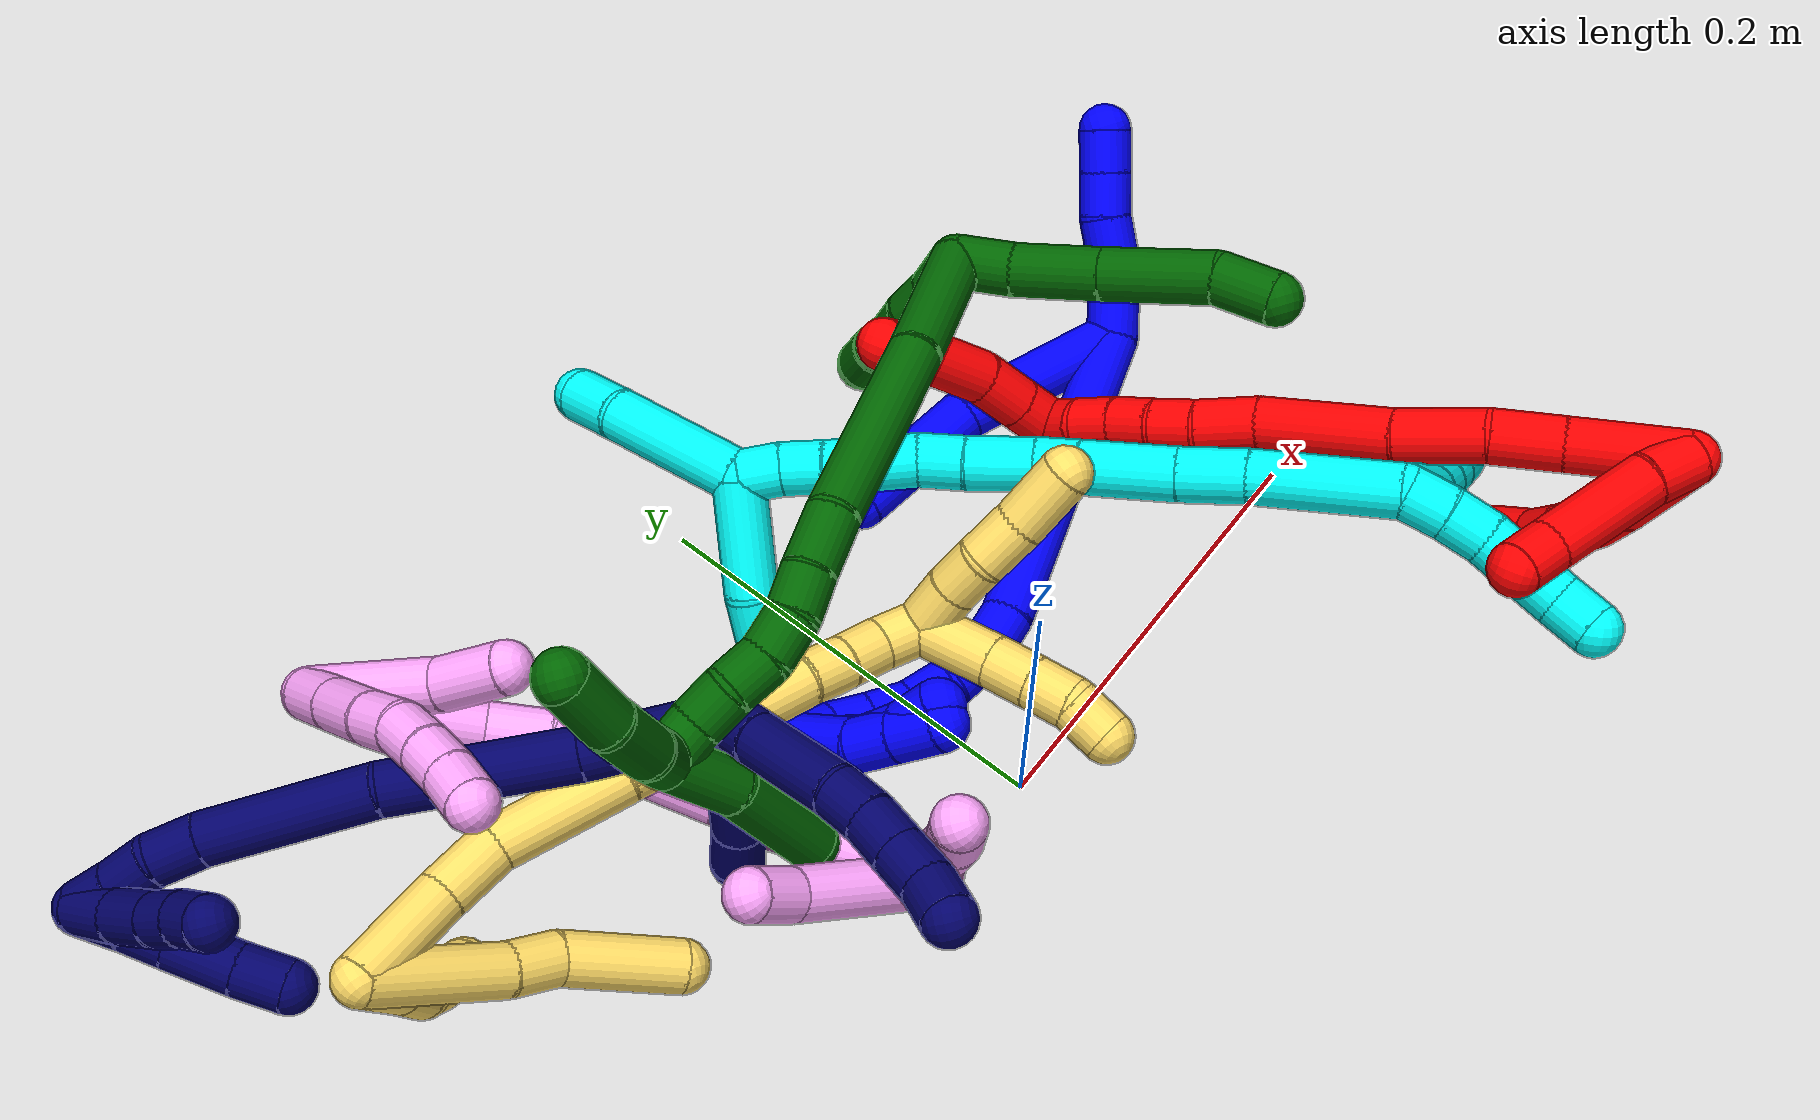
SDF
<sdf version="1.7">
 <world name="default">
  <plugin name="TubeGeneratorPlugin" filename="libtube_generator_plugin.so"/>
  <model name="photoneo_s_sensor">
   <static>1</static>
   <pose>0 0 2 1.57079 1.57079 3.14159</pose>
   <link name="link">
    <inertial><mass>0.1</mass></inertial>
    <sensor name="sensor" type="depth">
     <update_rate>30</update_rate>
     <camera>
      <horizontal_fov>1.22</horizontal_fov>
      <image><width>1920</width><height>1200</height><format>B8G8R8</format></image>
      <clip><near>0.1</near><far>4</far></clip>
      <depth_camera><output>points</output></depth_camera>
     </camera>
     <plugin name="camera_plugin" filename="libgazebo_ros_depth_camera.so">
      <baseline>0.2</baseline>
      <alwaysOn>1</alwaysOn>
      <updateRate>0.0</updateRate>
      <cameraName>camera_ir</cameraName>
      <imageTopicName>/camera/color/image_raw</imageTopicName>
      <cameraInfoTopicName>/camera/color/camera_info</cameraInfoTopicName>
      <depthImageTopicName>/camera/depth/image_raw</depthImageTopicName>
      <depthImageCameraInfoTopicName>/camera/depth/camera_info</depthImageCameraInfoTopicName>
      <pointCloudTopicName>/camera/depth/points</pointCloudTopicName>
      <frameName>fr_optical</frameName>
      <pointCloudCutoff>0.1</pointCloudCutoff>
      <pointCloudCutoffMax>2.0</pointCloudCutoffMax>
      <distortionK1>0</distortionK1>
      <distortionK2>0</distortionK2>
      <distortionK3>0</distortionK3>
      <distortionT1>0</distortionT1>
      <distortionT2>0</distortionT2>
      <CxPrime>0</CxPrime>
      <Cx>0</Cx>
      <Cy>0</Cy>
      <focalLength>0</focalLength>
      <hackBaseline>0</hackBaseline>
     </plugin>
    </sensor>
   </link>
  </model>
  <gravity>0 0 -9.8</gravity>
  <magnetic_field>6e-06 2.3e-05 -4.2e-05</magnetic_field>
  <atmosphere type="adiabatic"/>
  <physics name="default_physics" default="0" type="ode">
   <max_step_size>0.003</max_step_size>
   <real_time_factor>1</real_time_factor>
   <real_time_update_rate>1000</real_time_update_rate>
   <max_contacts>10000</max_contacts>
   <ode>
    <solver>
     <type>quick</type>
     <iters>100</iters>
     <sor>1.3</sor>
     <use_dynamic_moi_rescaling>0</use_dynamic_moi_rescaling>
    </solver>
    <constraints>
     <contact_max_correcting_vel>0</contact_max_correcting_vel>
     <contact_surface_layer>0.001</contact_surface_layer>
     <cfm>0</cfm>
     <erp>0.2</erp>
    </constraints>
   </ode>
  </physics>
  <scene><ambient>0.4 0.4 0.4 1</ambient><background>0.7 0.7 0.7 1</background><shadows>0</shadows></scene>
  <audio><device>default</device></audio>
  <spherical_coordinates>
   <surface_model>EARTH_WGS84</surface_model>
   <latitude_deg>0</latitude_deg>
   <longitude_deg>0</longitude_deg>
   <elevation>0</elevation>
   <heading_deg>0</heading_deg>
  </spherical_coordinates>
  <model name="bin">
   <static>1</static>
   <link name="bottom">
    <collision name="collision-bottom">
     <pose>0 0 -0.01 0 -0 0</pose>
     <geometry><box><size>0.8 0.6 0.02</size></box></geometry>
     <surface>
      <friction><ode><mu>100</mu><mu2>100</mu2></ode></friction>
      <contact><collide_bitmask>65535</collide_bitmask></contact>
     </surface>
    </collision>
   </link>
   <link name="west_wall">
    <collision name="collision-west_wall">
     <pose>-0.41 0 0.1 0 -0 0</pose>
     <geometry><box><size>0.02 0.6 0.2</size></box></geometry>
     <surface>
      <friction><ode><mu>100</mu><mu2>100</mu2></ode></friction>
      <contact><collide_bitmask>65535</collide_bitmask></contact>
     </surface>
    </collision>
   </link>
   <link name="east_wall">
    <collision name="collision-east_wall">
     <pose>0.41 0 0.1 0 -0 0</pose>
     <geometry><box><size>0.02 0.6 0.2</size></box></geometry>
     <surface>
      <friction><ode><mu>100</mu><mu2>100</mu2></ode></friction>
      <contact><collide_bitmask>65535</collide_bitmask></contact>
     </surface>
    </collision>
   </link>
   <link name="south_wall">
    <collision name="collision-south_wall">
     <pose>0 -0.31 0.1 0 -0 0</pose>
     <geometry><box><size>0.8 0.02 0.2</size></box></geometry>
     <surface>
      <friction><ode><mu>100</mu><mu2>100</mu2></ode></friction>
      <contact><collide_bitmask>65535</collide_bitmask></contact>
     </surface>
    </collision>
   </link>
   <link name="north_wall">
    <collision name="collision-north_wall">
     <pose>0 0.31 0.1 0 -0 0</pose>
     <geometry><box><size>0.8 0.02 0.2</size></box></geometry>
     <surface>
      <friction><ode><mu>100</mu><mu2>100</mu2></ode></friction>
      <contact><collide_bitmask>65535</collide_bitmask></contact>
     </surface>
    </collision>
   </link>
  </model>
  <model name="1">
   <static>0</static>
   <link name="1">
    <collision name="collision-cylinder-e_1_2_8">
     <pose>-0.006073 -0.015687 0.03742 0.396972 -0.148562 -0.029934</pose>
     <geometry><cylinder><radius>0.0125</radius><length>0.082054</length></cylinder></geometry>
     <surface>
      <friction><ode><mu>1.16</mu><mu2>1.16</mu2><slip1>0</slip1><slip2>0</slip2></ode></friction>
      <contact><ode><kp>1e+06</kp><kd>1</kd><max_vel>0</max_vel><min_depth>0.001</min_depth></ode></contact>
     </surface>
    </collision>
    <visual name="visual-cylinder-e_1_2_8">
     <pose>-0.006073 -0.015687 0.03742 0.396972 -0.148562 -0.029934</pose>
     <geometry><cylinder><radius>0.0125</radius><length>0.082054</length></cylinder></geometry>
     <material><ambient>0 0 1 1</ambient></material>
    </visual>
    <collision name="collision-cylinder-e_2_8_6">
     <pose>-0.024246 -0.048377 0.101648 0.565184 -0.364179 -0.106827</pose>
     <geometry><cylinder><radius>0.0125</radius><length>0.067946</length></cylinder></geometry>
     <surface>
      <friction><ode><mu>1.16</mu><mu2>1.16</mu2><slip1>0</slip1><slip2>0</slip2></ode></friction>
      <contact><ode><kp>1e+06</kp><kd>1</kd><max_vel>0</max_vel><min_depth>0.001</min_depth></ode></contact>
     </surface>
    </collision>
    <visual name="visual-cylinder-e_2_8_6">
     <pose>-0.024246 -0.048377 0.101648 0.565184 -0.364179 -0.106827</pose>
     <geometry><cylinder><radius>0.0125</radius><length>0.067946</length></cylinder></geometry>
     <material><ambient>0 0 1 1</ambient></material>
    </visual>
    <collision name="collision-cylinder-e_1_2_9">
     <pose>0.016643 0.0004 -0.006115 -3.0763 1.21799 -3.04801</pose>
     <geometry><cylinder><radius>0.0125</radius><length>0.035471</length></cylinder></geometry>
     <surface>
      <friction><ode><mu>1.16</mu><mu2>1.16</mu2><slip1>0</slip1><slip2>0</slip2></ode></friction>
      <contact><ode><kp>1e+06</kp><kd>1</kd><max_vel>0</max_vel><min_depth>0.001</min_depth></ode></contact>
     </surface>
    </collision>
    <visual name="visual-cylinder-e_1_2_9">
     <pose>0.016643 0.0004 -0.006115 -3.0763 1.21799 -3.04801</pose>
     <geometry><cylinder><radius>0.0125</radius><length>0.035471</length></cylinder></geometry>
     <material><ambient>0 0 1 1</ambient></material>
    </visual>
    <collision name="collision-cylinder-e_2_9_10">
     <pose>0.04472 -0.000945 -0.014169 2.40873 1.34651 2.24465</pose>
     <geometry><cylinder><radius>0.0125</radius><length>0.023456</length></cylinder></geometry>
     <surface>
      <friction><ode><mu>1.16</mu><mu2>1.16</mu2><slip1>0</slip1><slip2>0</slip2></ode></friction>
      <contact><ode><kp>1e+06</kp><kd>1</kd><max_vel>0</max_vel><min_depth>0.001</min_depth></ode></contact>
     </surface>
    </collision>
    <visual name="visual-cylinder-e_2_9_10">
     <pose>0.04472 -0.000945 -0.014169 2.40873 1.34651 2.24465</pose>
     <geometry><cylinder><radius>0.0125</radius><length>0.023456</length></cylinder></geometry>
     <material><ambient>0 0 1 1</ambient></material>
    </visual>
    <collision name="collision-cylinder-e_3_10_11">
     <pose>0.06588 -0.003092 -0.019617 3.02769 1.22244 2.97922</pose>
     <geometry><cylinder><radius>0.0125</radius><length>0.020693</length></cylinder></geometry>
     <surface>
      <friction><ode><mu>1.16</mu><mu2>1.16</mu2><slip1>0</slip1><slip2>0</slip2></ode></friction>
      <contact><ode><kp>1e+06</kp><kd>1</kd><max_vel>0</max_vel><min_depth>0.001</min_depth></ode></contact>
     </surface>
    </collision>
    <visual name="visual-cylinder-e_3_10_11">
     <pose>0.06588 -0.003092 -0.019617 3.02769 1.22244 2.97922</pose>
     <geometry><cylinder><radius>0.0125</radius><length>0.020693</length></cylinder></geometry>
     <material><ambient>0 0 1 1</ambient></material>
    </visual>
    <collision name="collision-cylinder-e_4_11_5">
     <pose>0.085227 -0.00409 -0.026426 2.9629 1.23535 2.89071</pose>
     <geometry><cylinder><radius>0.0125</radius><length>0.02038</length></cylinder></geometry>
     <surface>
      <friction><ode><mu>1.16</mu><mu2>1.16</mu2><slip1>0</slip1><slip2>0</slip2></ode></friction>
      <contact><ode><kp>1e+06</kp><kd>1</kd><max_vel>0</max_vel><min_depth>0.001</min_depth></ode></contact>
     </surface>
    </collision>
    <visual name="visual-cylinder-e_4_11_5">
     <pose>0.085227 -0.00409 -0.026426 2.9629 1.23535 2.89071</pose>
     <geometry><cylinder><radius>0.0125</radius><length>0.02038</length></cylinder></geometry>
     <material><ambient>0 0 1 1</ambient></material>
    </visual>
    <collision name="collision-cylinder-e_1_2_12">
     <pose>-0.054061 -0.037152 0.039281 0.757547 -0.785342 -0.326742</pose>
     <geometry><cylinder><radius>0.0125</radius><length>0.152917</length></cylinder></geometry>
     <surface>
      <friction><ode><mu>1.16</mu><mu2>1.16</mu2><slip1>0</slip1><slip2>0</slip2></ode></friction>
      <contact><ode><kp>1e+06</kp><kd>1</kd><max_vel>0</max_vel><min_depth>0.001</min_depth></ode></contact>
     </surface>
    </collision>
    <visual name="visual-cylinder-e_1_2_12">
     <pose>-0.054061 -0.037152 0.039281 0.757547 -0.785342 -0.326742</pose>
     <geometry><cylinder><radius>0.0125</radius><length>0.152917</length></cylinder></geometry>
     <material><ambient>0 0 1 1</ambient></material>
    </visual>
    <collision name="collision-cylinder-e_2_12_13">
     <pose>-0.114299 -0.080201 0.085305 0.718607 -0.603645 -0.232822</pose>
     <geometry><cylinder><radius>0.0125</radius><length>0.021762</length></cylinder></geometry>
     <surface>
      <friction><ode><mu>1.16</mu><mu2>1.16</mu2><slip1>0</slip1><slip2>0</slip2></ode></friction>
      <contact><ode><kp>1e+06</kp><kd>1</kd><max_vel>0</max_vel><min_depth>0.001</min_depth></ode></contact>
     </surface>
    </collision>
    <visual name="visual-cylinder-e_2_12_13">
     <pose>-0.114299 -0.080201 0.085305 0.718607 -0.603645 -0.232822</pose>
     <geometry><cylinder><radius>0.0125</radius><length>0.021762</length></cylinder></geometry>
     <material><ambient>0 0 1 1</ambient></material>
    </visual>
    <collision name="collision-cylinder-e_3_13_14">
     <pose>-0.124503 -0.093139 0.100866 0.673788 -0.342822 -0.121114</pose>
     <geometry><cylinder><radius>0.0125</radius><length>0.023962</length></cylinder></geometry>
     <surface>
      <friction><ode><mu>1.16</mu><mu2>1.16</mu2><slip1>0</slip1><slip2>0</slip2></ode></friction>
      <contact><ode><kp>1e+06</kp><kd>1</kd><max_vel>0</max_vel><min_depth>0.001</min_depth></ode></contact>
     </surface>
    </collision>
    <visual name="visual-cylinder-e_3_13_14">
     <pose>-0.124503 -0.093139 0.100866 0.673788 -0.342822 -0.121114</pose>
     <geometry><cylinder><radius>0.0125</radius><length>0.023962</length></cylinder></geometry>
     <material><ambient>0 0 1 1</ambient></material>
    </visual>
    <collision name="collision-cylinder-e_4_14_15">
     <pose>-0.130581 -0.104159 0.118845 0.40976 -0.202529 -0.042223</pose>
     <geometry><cylinder><radius>0.0125</radius><length>0.020393</length></cylinder></geometry>
     <surface>
      <friction><ode><mu>1.16</mu><mu2>1.16</mu2><slip1>0</slip1><slip2>0</slip2></ode></friction>
      <contact><ode><kp>1e+06</kp><kd>1</kd><max_vel>0</max_vel><min_depth>0.001</min_depth></ode></contact>
     </surface>
    </collision>
    <visual name="visual-cylinder-e_4_14_15">
     <pose>-0.130581 -0.104159 0.118845 0.40976 -0.202529 -0.042223</pose>
     <geometry><cylinder><radius>0.0125</radius><length>0.020393</length></cylinder></geometry>
     <material><ambient>0 0 1 1</ambient></material>
    </visual>
    <collision name="collision-cylinder-e_5_15_16">
     <pose>-0.132158 -0.113063 0.137091 0.496801 0.045885 0.01164</pose>
     <geometry><cylinder><radius>0.0125</radius><length>0.020689</length></cylinder></geometry>
     <surface>
      <friction><ode><mu>1.16</mu><mu2>1.16</mu2><slip1>0</slip1><slip2>0</slip2></ode></friction>
      <contact><ode><kp>1e+06</kp><kd>1</kd><max_vel>0</max_vel><min_depth>0.001</min_depth></ode></contact>
     </surface>
    </collision>
    <visual name="visual-cylinder-e_5_15_16">
     <pose>-0.132158 -0.113063 0.137091 0.496801 0.045885 0.01164</pose>
     <geometry><cylinder><radius>0.0125</radius><length>0.020689</length></cylinder></geometry>
     <material><ambient>0 0 1 1</ambient></material>
    </visual>
    <collision name="collision-cylinder-e_6_16_17">
     <pose>-0.130665 -0.123132 0.154729 0.541399 0.101675 0.028239</pose>
     <geometry><cylinder><radius>0.0125</radius><length>0.020066</length></cylinder></geometry>
     <surface>
      <friction><ode><mu>1.16</mu><mu2>1.16</mu2><slip1>0</slip1><slip2>0</slip2></ode></friction>
      <contact><ode><kp>1e+06</kp><kd>1</kd><max_vel>0</max_vel><min_depth>0.001</min_depth></ode></contact>
     </surface>
    </collision>
    <visual name="visual-cylinder-e_6_16_17">
     <pose>-0.130665 -0.123132 0.154729 0.541399 0.101675 0.028239</pose>
     <geometry><cylinder><radius>0.0125</radius><length>0.020066</length></cylinder></geometry>
     <material><ambient>0 0 1 1</ambient></material>
    </visual>
    <collision name="collision-cylinder-e_7_17_18">
     <pose>-0.129018 -0.135996 0.16967 0.879624 0.062672 0.029498</pose>
     <geometry><cylinder><radius>0.0125</radius><length>0.02008</length></cylinder></geometry>
     <surface>
      <friction><ode><mu>1.16</mu><mu2>1.16</mu2><slip1>0</slip1><slip2>0</slip2></ode></friction>
      <contact><ode><kp>1e+06</kp><kd>1</kd><max_vel>0</max_vel><min_depth>0.001</min_depth></ode></contact>
     </surface>
    </collision>
    <visual name="visual-cylinder-e_7_17_18">
     <pose>-0.129018 -0.135996 0.16967 0.879624 0.062672 0.029498</pose>
     <geometry><cylinder><radius>0.0125</radius><length>0.02008</length></cylinder></geometry>
     <material><ambient>0 0 1 1</ambient></material>
    </visual>
    <collision name="collision-cylinder-e_8_18_1">
     <pose>-0.125007 -0.151423 0.181578 0.949136 0.342673 0.177317</pose>
     <geometry><cylinder><radius>0.0125</radius><length>0.020132</length></cylinder></geometry>
     <surface>
      <friction><ode><mu>1.16</mu><mu2>1.16</mu2><slip1>0</slip1><slip2>0</slip2></ode></friction>
      <contact><ode><kp>1e+06</kp><kd>1</kd><max_vel>0</max_vel><min_depth>0.001</min_depth></ode></contact>
     </surface>
    </collision>
    <visual name="visual-cylinder-e_8_18_1">
     <pose>-0.125007 -0.151423 0.181578 0.949136 0.342673 0.177317</pose>
     <geometry><cylinder><radius>0.0125</radius><length>0.020132</length></cylinder></geometry>
     <material><ambient>0 0 1 1</ambient></material>
    </visual>
    <collision name="collision-cylinder-e_1_1_19">
     <pose>-0.129523 -0.171607 0.163161 2.66112 -0.284653 -1.05857</pose>
     <geometry><cylinder><radius>0.0125</radius><length>0.056253</length></cylinder></geometry>
     <surface>
      <friction><ode><mu>1.16</mu><mu2>1.16</mu2><slip1>0</slip1><slip2>0</slip2></ode></friction>
      <contact><ode><kp>1e+06</kp><kd>1</kd><max_vel>0</max_vel><min_depth>0.001</min_depth></ode></contact>
     </surface>
    </collision>
    <visual name="visual-cylinder-e_1_1_19">
     <pose>-0.129523 -0.171607 0.163161 2.66112 -0.284653 -1.05857</pose>
     <geometry><cylinder><radius>0.0125</radius><length>0.056253</length></cylinder></geometry>
     <material><ambient>0 0 1 1</ambient></material>
    </visual>
    <collision name="collision-cylinder-e_2_19_20">
     <pose>-0.138008 -0.187035 0.128966 2.86144 -0.054886 -0.384545</pose>
     <geometry><cylinder><radius>0.0125</radius><length>0.021379</length></cylinder></geometry>
     <surface>
      <friction><ode><mu>1.16</mu><mu2>1.16</mu2><slip1>0</slip1><slip2>0</slip2></ode></friction>
      <contact><ode><kp>1e+06</kp><kd>1</kd><max_vel>0</max_vel><min_depth>0.001</min_depth></ode></contact>
     </surface>
    </collision>
    <visual name="visual-cylinder-e_2_19_20">
     <pose>-0.138008 -0.187035 0.128966 2.86144 -0.054886 -0.384545</pose>
     <geometry><cylinder><radius>0.0125</radius><length>0.021379</length></cylinder></geometry>
     <material><ambient>0 0 1 1</ambient></material>
    </visual>
    <collision name="collision-cylinder-e_3_20_4">
     <pose>-0.139199 -0.192984 0.107951 2.86991 -0.054074 -0.390666</pose>
     <geometry><cylinder><radius>0.0125</radius><length>0.022368</length></cylinder></geometry>
     <surface>
      <friction><ode><mu>1.16</mu><mu2>1.16</mu2><slip1>0</slip1><slip2>0</slip2></ode></friction>
      <contact><ode><kp>1e+06</kp><kd>1</kd><max_vel>0</max_vel><min_depth>0.001</min_depth></ode></contact>
     </surface>
    </collision>
    <visual name="visual-cylinder-e_3_20_4">
     <pose>-0.139199 -0.192984 0.107951 2.86991 -0.054074 -0.390666</pose>
     <geometry><cylinder><radius>0.0125</radius><length>0.022368</length></cylinder></geometry>
     <material><ambient>0 0 1 1</ambient></material>
    </visual>
    <collision name="collision-cylinder-e_1_1_21">
     <pose>-0.124984 -0.162024 0.178136 2.82934 -0.342575 -1.665</pose>
     <geometry><cylinder><radius>0.0125</radius><length>0.02</length></cylinder></geometry>
     <surface>
      <friction><ode><mu>1.16</mu><mu2>1.16</mu2><slip1>0</slip1><slip2>0</slip2></ode></friction>
      <contact><ode><kp>1e+06</kp><kd>1</kd><max_vel>0</max_vel><min_depth>0.001</min_depth></ode></contact>
     </surface>
    </collision>
    <visual name="visual-cylinder-e_1_1_21">
     <pose>-0.124984 -0.162024 0.178136 2.82934 -0.342575 -1.665</pose>
     <geometry><cylinder><radius>0.0125</radius><length>0.02</length></cylinder></geometry>
     <material><ambient>0 0 1 1</ambient></material>
    </visual>
    <collision name="collision-cylinder-e_2_21_22">
     <pose>-0.131252 -0.169176 0.160605 2.68028 -0.295136 -1.12865</pose>
     <geometry><cylinder><radius>0.0125</radius><length>0.02</length></cylinder></geometry>
     <surface>
      <friction><ode><mu>1.16</mu><mu2>1.16</mu2><slip1>0</slip1><slip2>0</slip2></ode></friction>
      <contact><ode><kp>1e+06</kp><kd>1</kd><max_vel>0</max_vel><min_depth>0.001</min_depth></ode></contact>
     </surface>
    </collision>
    <visual name="visual-cylinder-e_2_21_22">
     <pose>-0.131252 -0.169176 0.160605 2.68028 -0.295136 -1.12865</pose>
     <geometry><cylinder><radius>0.0125</radius><length>0.02</length></cylinder></geometry>
     <material><ambient>0 0 1 1</ambient></material>
    </visual>
    <collision name="collision-cylinder-e_3_22_23">
     <pose>-0.136032 -0.177797 0.143236 2.68145 -0.188268 -0.766356</pose>
     <geometry><cylinder><radius>0.0125</radius><length>0.02</length></cylinder></geometry>
     <surface>
      <friction><ode><mu>1.16</mu><mu2>1.16</mu2><slip1>0</slip1><slip2>0</slip2></ode></friction>
      <contact><ode><kp>1e+06</kp><kd>1</kd><max_vel>0</max_vel><min_depth>0.001</min_depth></ode></contact>
     </surface>
    </collision>
    <visual name="visual-cylinder-e_3_22_23">
     <pose>-0.136032 -0.177797 0.143236 2.68145 -0.188268 -0.766356</pose>
     <geometry><cylinder><radius>0.0125</radius><length>0.02</length></cylinder></geometry>
     <material><ambient>0 0 1 1</ambient></material>
    </visual>
    <collision name="collision-cylinder-e_4_23_24">
     <pose>-0.13733 -0.185028 0.124872 2.85013 0.057405 0.386344</pose>
     <geometry><cylinder><radius>0.0125</radius><length>0.02</length></cylinder></geometry>
     <surface>
      <friction><ode><mu>1.16</mu><mu2>1.16</mu2><slip1>0</slip1><slip2>0</slip2></ode></friction>
      <contact><ode><kp>1e+06</kp><kd>1</kd><max_vel>0</max_vel><min_depth>0.001</min_depth></ode></contact>
     </surface>
    </collision>
    <visual name="visual-cylinder-e_4_23_24">
     <pose>-0.13733 -0.185028 0.124872 2.85013 0.057405 0.386344</pose>
     <geometry><cylinder><radius>0.0125</radius><length>0.02</length></cylinder></geometry>
     <material><ambient>0 0 1 1</ambient></material>
    </visual>
    <collision name="collision-cylinder-e_5_24_3">
     <pose>-0.13437 -0.190384 0.105922 2.88266 0.240957 1.49817</pose>
     <geometry><cylinder><radius>0.0125</radius><length>0.02</length></cylinder></geometry>
     <surface>
      <friction><ode><mu>1.16</mu><mu2>1.16</mu2><slip1>0</slip1><slip2>0</slip2></ode></friction>
      <contact><ode><kp>1e+06</kp><kd>1</kd><max_vel>0</max_vel><min_depth>0.001</min_depth></ode></contact>
     </surface>
    </collision>
    <visual name="visual-cylinder-e_5_24_3">
     <pose>-0.13437 -0.190384 0.105922 2.88266 0.240957 1.49817</pose>
     <geometry><cylinder><radius>0.0125</radius><length>0.02</length></cylinder></geometry>
     <material><ambient>0 0 1 1</ambient></material>
    </visual>
    <collision name="collision-sphere-3">
     <pose>-0.131983 -0.19287 0.096535 0 -0 0</pose>
     <geometry><sphere><radius>0.0125</radius></sphere></geometry>
     <surface>
      <friction><ode><mu>1.16</mu><mu2>1.16</mu2><slip1>0</slip1><slip2>0</slip2></ode></friction>
      <contact><ode><kp>1e+06</kp><kd>1</kd><max_vel>0</max_vel><min_depth>0.001</min_depth></ode></contact>
     </surface>
    </collision>
    <visual name="visual-sphere-3">
     <pose>-0.131983 -0.19287 0.096535 0 -0 0</pose>
     <geometry><sphere><radius>0.0125</radius></sphere></geometry>
     <material><ambient>0 0 1 1</ambient></material>
    </visual>
    <collision name="collision-sphere-24">
     <pose>-0.136756 -0.187897 0.11531 0 -0 0</pose>
     <geometry><sphere><radius>0.0125</radius></sphere></geometry>
     <surface>
      <friction><ode><mu>1.16</mu><mu2>1.16</mu2><slip1>0</slip1><slip2>0</slip2></ode></friction>
      <contact><ode><kp>1e+06</kp><kd>1</kd><max_vel>0</max_vel><min_depth>0.001</min_depth></ode></contact>
     </surface>
    </collision>
    <visual name="visual-sphere-24">
     <pose>-0.136756 -0.187897 0.11531 0 -0 0</pose>
     <geometry><sphere><radius>0.0125</radius></sphere></geometry>
     <material><ambient>0 0 1 1</ambient></material>
    </visual>
    <collision name="collision-sphere-23">
     <pose>-0.137904 -0.182159 0.134435 0 -0 0</pose>
     <geometry><sphere><radius>0.0125</radius></sphere></geometry>
     <surface>
      <friction><ode><mu>1.16</mu><mu2>1.16</mu2><slip1>0</slip1><slip2>0</slip2></ode></friction>
      <contact><ode><kp>1e+06</kp><kd>1</kd><max_vel>0</max_vel><min_depth>0.001</min_depth></ode></contact>
     </surface>
    </collision>
    <visual name="visual-sphere-23">
     <pose>-0.137904 -0.182159 0.134435 0 -0 0</pose>
     <geometry><sphere><radius>0.0125</radius></sphere></geometry>
     <material><ambient>0 0 1 1</ambient></material>
    </visual>
    <collision name="collision-sphere-22">
     <pose>-0.13416 -0.173435 0.152038 0 -0 0</pose>
     <geometry><sphere><radius>0.0125</radius></sphere></geometry>
     <surface>
      <friction><ode><mu>1.16</mu><mu2>1.16</mu2><slip1>0</slip1><slip2>0</slip2></ode></friction>
      <contact><ode><kp>1e+06</kp><kd>1</kd><max_vel>0</max_vel><min_depth>0.001</min_depth></ode></contact>
     </surface>
    </collision>
    <visual name="visual-sphere-22">
     <pose>-0.13416 -0.173435 0.152038 0 -0 0</pose>
     <geometry><sphere><radius>0.0125</radius></sphere></geometry>
     <material><ambient>0 0 1 1</ambient></material>
    </visual>
    <collision name="collision-sphere-21">
     <pose>-0.128343 -0.164917 0.169173 0 -0 0</pose>
     <geometry><sphere><radius>0.0125</radius></sphere></geometry>
     <surface>
      <friction><ode><mu>1.16</mu><mu2>1.16</mu2><slip1>0</slip1><slip2>0</slip2></ode></friction>
      <contact><ode><kp>1e+06</kp><kd>1</kd><max_vel>0</max_vel><min_depth>0.001</min_depth></ode></contact>
     </surface>
    </collision>
    <visual name="visual-sphere-21">
     <pose>-0.128343 -0.164917 0.169173 0 -0 0</pose>
     <geometry><sphere><radius>0.0125</radius></sphere></geometry>
     <material><ambient>0 0 1 1</ambient></material>
    </visual>
    <collision name="collision-sphere-4">
     <pose>-0.139804 -0.19598 0.097193 0 -0 0</pose>
     <geometry><sphere><radius>0.0125</radius></sphere></geometry>
     <surface>
      <friction><ode><mu>1.16</mu><mu2>1.16</mu2><slip1>0</slip1><slip2>0</slip2></ode></friction>
      <contact><ode><kp>1e+06</kp><kd>1</kd><max_vel>0</max_vel><min_depth>0.001</min_depth></ode></contact>
     </surface>
    </collision>
    <visual name="visual-sphere-4">
     <pose>-0.139804 -0.19598 0.097193 0 -0 0</pose>
     <geometry><sphere><radius>0.0125</radius></sphere></geometry>
     <material><ambient>0 0 1 1</ambient></material>
    </visual>
    <collision name="collision-sphere-20">
     <pose>-0.138595 -0.189987 0.118709 0 -0 0</pose>
     <geometry><sphere><radius>0.0125</radius></sphere></geometry>
     <surface>
      <friction><ode><mu>1.16</mu><mu2>1.16</mu2><slip1>0</slip1><slip2>0</slip2></ode></friction>
      <contact><ode><kp>1e+06</kp><kd>1</kd><max_vel>0</max_vel><min_depth>0.001</min_depth></ode></contact>
     </surface>
    </collision>
    <visual name="visual-sphere-20">
     <pose>-0.138595 -0.189987 0.118709 0 -0 0</pose>
     <geometry><sphere><radius>0.0125</radius></sphere></geometry>
     <material><ambient>0 0 1 1</ambient></material>
    </visual>
    <collision name="collision-sphere-11">
     <pose>0.075605 -0.003493 -0.023125 0 -0 0</pose>
     <geometry><sphere><radius>0.0125</radius></sphere></geometry>
     <surface>
      <friction><ode><mu>1.16</mu><mu2>1.16</mu2><slip1>0</slip1><slip2>0</slip2></ode></friction>
      <contact><ode><kp>1e+06</kp><kd>1</kd><max_vel>0</max_vel><min_depth>0.001</min_depth></ode></contact>
     </surface>
    </collision>
    <visual name="visual-sphere-11">
     <pose>0.075605 -0.003493 -0.023125 0 -0 0</pose>
     <geometry><sphere><radius>0.0125</radius></sphere></geometry>
     <material><ambient>0 0 1 1</ambient></material>
    </visual>
    <collision name="collision-sphere-10">
     <pose>0.056155 -0.002691 -0.016108 0 -0 0</pose>
     <geometry><sphere><radius>0.0125</radius></sphere></geometry>
     <surface>
      <friction><ode><mu>1.16</mu><mu2>1.16</mu2><slip1>0</slip1><slip2>0</slip2></ode></friction>
      <contact><ode><kp>1e+06</kp><kd>1</kd><max_vel>0</max_vel><min_depth>0.001</min_depth></ode></contact>
     </surface>
    </collision>
    <visual name="visual-sphere-10">
     <pose>0.056155 -0.002691 -0.016108 0 -0 0</pose>
     <geometry><sphere><radius>0.0125</radius></sphere></geometry>
     <material><ambient>0 0 1 1</ambient></material>
    </visual>
    <collision name="collision-sphere-6">
     <pose>-0.036347 -0.065378 0.128456 0 -0 0</pose>
     <geometry><sphere><radius>0.0125</radius></sphere></geometry>
     <surface>
      <friction><ode><mu>1.16</mu><mu2>1.16</mu2><slip1>0</slip1><slip2>0</slip2></ode></friction>
      <contact><ode><kp>1e+06</kp><kd>1</kd><max_vel>0</max_vel><min_depth>0.001</min_depth></ode></contact>
     </surface>
    </collision>
    <visual name="visual-sphere-6">
     <pose>-0.036347 -0.065378 0.128456 0 -0 0</pose>
     <geometry><sphere><radius>0.0125</radius></sphere></geometry>
     <material><ambient>0 0 1 1</ambient></material>
    </visual>
    <collision name="collision-sphere-9">
     <pose>0.033286 0.0008 -0.01223 0 -0 0</pose>
     <geometry><sphere><radius>0.0125</radius></sphere></geometry>
     <surface>
      <friction><ode><mu>1.16</mu><mu2>1.16</mu2><slip1>0</slip1><slip2>0</slip2></ode></friction>
      <contact><ode><kp>1e+06</kp><kd>1</kd><max_vel>0</max_vel><min_depth>0.001</min_depth></ode></contact>
     </surface>
    </collision>
    <visual name="visual-sphere-9">
     <pose>0.033286 0.0008 -0.01223 0 -0 0</pose>
     <geometry><sphere><radius>0.0125</radius></sphere></geometry>
     <material><ambient>0 0 1 1</ambient></material>
    </visual>
    <collision name="collision-sphere-2">
     <geometry><sphere><radius>0.0125</radius></sphere></geometry>
     <surface>
      <friction><ode><mu>1.16</mu><mu2>1.16</mu2><slip1>0</slip1><slip2>0</slip2></ode></friction>
      <contact><ode><kp>1e+06</kp><kd>1</kd><max_vel>0</max_vel><min_depth>0.001</min_depth></ode></contact>
     </surface>
    </collision>
    <visual name="visual-sphere-2">
     <geometry><sphere><radius>0.0125</radius></sphere></geometry>
     <material><ambient>0 0 1 1</ambient></material>
    </visual>
    <collision name="collision-sphere-19">
     <pose>-0.137422 -0.184084 0.139223 0 -0 0</pose>
     <geometry><sphere><radius>0.0125</radius></sphere></geometry>
     <surface>
      <friction><ode><mu>1.16</mu><mu2>1.16</mu2><slip1>0</slip1><slip2>0</slip2></ode></friction>
      <contact><ode><kp>1e+06</kp><kd>1</kd><max_vel>0</max_vel><min_depth>0.001</min_depth></ode></contact>
     </surface>
    </collision>
    <visual name="visual-sphere-19">
     <pose>-0.137422 -0.184084 0.139223 0 -0 0</pose>
     <geometry><sphere><radius>0.0125</radius></sphere></geometry>
     <material><ambient>0 0 1 1</ambient></material>
    </visual>
    <collision name="collision-sphere-8">
     <pose>-0.012145 -0.031375 0.074839 0 -0 0</pose>
     <geometry><sphere><radius>0.0125</radius></sphere></geometry>
     <surface>
      <friction><ode><mu>1.16</mu><mu2>1.16</mu2><slip1>0</slip1><slip2>0</slip2></ode></friction>
      <contact><ode><kp>1e+06</kp><kd>1</kd><max_vel>0</max_vel><min_depth>0.001</min_depth></ode></contact>
     </surface>
    </collision>
    <visual name="visual-sphere-8">
     <pose>-0.012145 -0.031375 0.074839 0 -0 0</pose>
     <geometry><sphere><radius>0.0125</radius></sphere></geometry>
     <material><ambient>0 0 1 1</ambient></material>
    </visual>
    <collision name="collision-sphere-5">
     <pose>0.094849 -0.004686 -0.029728 0 -0 0</pose>
     <geometry><sphere><radius>0.0125</radius></sphere></geometry>
     <surface>
      <friction><ode><mu>1.16</mu><mu2>1.16</mu2><slip1>0</slip1><slip2>0</slip2></ode></friction>
      <contact><ode><kp>1e+06</kp><kd>1</kd><max_vel>0</max_vel><min_depth>0.001</min_depth></ode></contact>
     </surface>
    </collision>
    <visual name="visual-sphere-5">
     <pose>0.094849 -0.004686 -0.029728 0 -0 0</pose>
     <geometry><sphere><radius>0.0125</radius></sphere></geometry>
     <material><ambient>0 0 1 1</ambient></material>
    </visual>
    <collision name="collision-sphere-12">
     <pose>-0.108123 -0.074304 0.078563 0 -0 0</pose>
     <geometry><sphere><radius>0.0125</radius></sphere></geometry>
     <surface>
      <friction><ode><mu>1.16</mu><mu2>1.16</mu2><slip1>0</slip1><slip2>0</slip2></ode></friction>
      <contact><ode><kp>1e+06</kp><kd>1</kd><max_vel>0</max_vel><min_depth>0.001</min_depth></ode></contact>
     </surface>
    </collision>
    <visual name="visual-sphere-12">
     <pose>-0.108123 -0.074304 0.078563 0 -0 0</pose>
     <geometry><sphere><radius>0.0125</radius></sphere></geometry>
     <material><ambient>0 0 1 1</ambient></material>
    </visual>
    <collision name="collision-sphere-13">
     <pose>-0.120476 -0.086098 0.092048 0 -0 0</pose>
     <geometry><sphere><radius>0.0125</radius></sphere></geometry>
     <surface>
      <friction><ode><mu>1.16</mu><mu2>1.16</mu2><slip1>0</slip1><slip2>0</slip2></ode></friction>
      <contact><ode><kp>1e+06</kp><kd>1</kd><max_vel>0</max_vel><min_depth>0.001</min_depth></ode></contact>
     </surface>
    </collision>
    <visual name="visual-sphere-13">
     <pose>-0.120476 -0.086098 0.092048 0 -0 0</pose>
     <geometry><sphere><radius>0.0125</radius></sphere></geometry>
     <material><ambient>0 0 1 1</ambient></material>
    </visual>
    <collision name="collision-sphere-14">
     <pose>-0.12853 -0.10018 0.109684 0 -0 0</pose>
     <geometry><sphere><radius>0.0125</radius></sphere></geometry>
     <surface>
      <friction><ode><mu>1.16</mu><mu2>1.16</mu2><slip1>0</slip1><slip2>0</slip2></ode></friction>
      <contact><ode><kp>1e+06</kp><kd>1</kd><max_vel>0</max_vel><min_depth>0.001</min_depth></ode></contact>
     </surface>
    </collision>
    <visual name="visual-sphere-14">
     <pose>-0.12853 -0.10018 0.109684 0 -0 0</pose>
     <geometry><sphere><radius>0.0125</radius></sphere></geometry>
     <material><ambient>0 0 1 1</ambient></material>
    </visual>
    <collision name="collision-sphere-15">
     <pose>-0.132632 -0.108138 0.128006 0 -0 0</pose>
     <geometry><sphere><radius>0.0125</radius></sphere></geometry>
     <surface>
      <friction><ode><mu>1.16</mu><mu2>1.16</mu2><slip1>0</slip1><slip2>0</slip2></ode></friction>
      <contact><ode><kp>1e+06</kp><kd>1</kd><max_vel>0</max_vel><min_depth>0.001</min_depth></ode></contact>
     </surface>
    </collision>
    <visual name="visual-sphere-15">
     <pose>-0.132632 -0.108138 0.128006 0 -0 0</pose>
     <geometry><sphere><radius>0.0125</radius></sphere></geometry>
     <material><ambient>0 0 1 1</ambient></material>
    </visual>
    <collision name="collision-sphere-16">
     <pose>-0.131683 -0.117988 0.146175 0 -0 0</pose>
     <geometry><sphere><radius>0.0125</radius></sphere></geometry>
     <surface>
      <friction><ode><mu>1.16</mu><mu2>1.16</mu2><slip1>0</slip1><slip2>0</slip2></ode></friction>
      <contact><ode><kp>1e+06</kp><kd>1</kd><max_vel>0</max_vel><min_depth>0.001</min_depth></ode></contact>
     </surface>
    </collision>
    <visual name="visual-sphere-16">
     <pose>-0.131683 -0.117988 0.146175 0 -0 0</pose>
     <geometry><sphere><radius>0.0125</radius></sphere></geometry>
     <material><ambient>0 0 1 1</ambient></material>
    </visual>
    <collision name="collision-sphere-17">
     <pose>-0.129647 -0.128275 0.163283 0 -0 0</pose>
     <geometry><sphere><radius>0.0125</radius></sphere></geometry>
     <surface>
      <friction><ode><mu>1.16</mu><mu2>1.16</mu2><slip1>0</slip1><slip2>0</slip2></ode></friction>
      <contact><ode><kp>1e+06</kp><kd>1</kd><max_vel>0</max_vel><min_depth>0.001</min_depth></ode></contact>
     </surface>
    </collision>
    <visual name="visual-sphere-17">
     <pose>-0.129647 -0.128275 0.163283 0 -0 0</pose>
     <geometry><sphere><radius>0.0125</radius></sphere></geometry>
     <material><ambient>0 0 1 1</ambient></material>
    </visual>
    <collision name="collision-sphere-18">
     <pose>-0.128389 -0.143716 0.176057 0 -0 0</pose>
     <geometry><sphere><radius>0.0125</radius></sphere></geometry>
     <surface>
      <friction><ode><mu>1.16</mu><mu2>1.16</mu2><slip1>0</slip1><slip2>0</slip2></ode></friction>
      <contact><ode><kp>1e+06</kp><kd>1</kd><max_vel>0</max_vel><min_depth>0.001</min_depth></ode></contact>
     </surface>
    </collision>
    <visual name="visual-sphere-18">
     <pose>-0.128389 -0.143716 0.176057 0 -0 0</pose>
     <geometry><sphere><radius>0.0125</radius></sphere></geometry>
     <material><ambient>0 0 1 1</ambient></material>
    </visual>
    <collision name="collision-sphere-1">
     <pose>-0.121625 -0.15913 0.1871 0 -0 0</pose>
     <geometry><sphere><radius>0.0125</radius></sphere></geometry>
     <surface>
      <friction><ode><mu>1.16</mu><mu2>1.16</mu2><slip1>0</slip1><slip2>0</slip2></ode></friction>
      <contact><ode><kp>1e+06</kp><kd>1</kd><max_vel>0</max_vel><min_depth>0.001</min_depth></ode></contact>
     </surface>
    </collision>
    <visual name="visual-sphere-1">
     <pose>-0.121625 -0.15913 0.1871 0 -0 0</pose>
     <geometry><sphere><radius>0.0125</radius></sphere></geometry>
     <material><ambient>0 0 1 1</ambient></material>
    </visual>
    <inertial>
     <pose>-0.067866 -0.083677 0.083728 0 -0 0</pose>
     <mass>0.75</mass>
     <inertia>
      <ixx>0.000203</ixx>
      <ixy>0</ixy>
      <ixz>0</ixz>
      <iyy>0.000221</iyy>
      <iyz>0</iyz>
      <izz>0.000437</izz>
     </inertia>
    </inertial>
   </link>
   <pose>0.205689 0.1005 0.013522 -1.93418 -0.384197 1.02209</pose>
  </model>
  <model name="2">
   <static>0</static>
   <link name="2">
    <collision name="collision-cylinder-e_1_2_8">
     <pose>-0.016598 -0.020824 -0.007949 1.93544 -0.640064 -0.897084</pose>
     <geometry><cylinder><radius>0.0125</radius><length>0.05558</length></cylinder></geometry>
     <surface>
      <friction><ode><mu>1.16</mu><mu2>1.16</mu2><slip1>0</slip1><slip2>0</slip2></ode></friction>
      <contact><ode><kp>1e+06</kp><kd>1</kd><max_vel>0</max_vel><min_depth>0.001</min_depth></ode></contact>
     </surface>
    </collision>
    <visual name="visual-cylinder-e_1_2_8">
     <pose>-0.016598 -0.020824 -0.007949 1.93544 -0.640064 -0.897084</pose>
     <geometry><cylinder><radius>0.0125</radius><length>0.05558</length></cylinder></geometry>
     <material><ambient>1 0 0 1</ambient></material>
    </visual>
    <collision name="collision-cylinder-e_2_8_9">
     <pose>-0.040578 -0.052687 -0.019815 1.9118 -0.562389 -0.776484</pose>
     <geometry><cylinder><radius>0.0125</radius><length>0.027694</length></cylinder></geometry>
     <surface>
      <friction><ode><mu>1.16</mu><mu2>1.16</mu2><slip1>0</slip1><slip2>0</slip2></ode></friction>
      <contact><ode><kp>1e+06</kp><kd>1</kd><max_vel>0</max_vel><min_depth>0.001</min_depth></ode></contact>
     </surface>
    </collision>
    <visual name="visual-cylinder-e_2_8_9">
     <pose>-0.040578 -0.052687 -0.019815 1.9118 -0.562389 -0.776484</pose>
     <geometry><cylinder><radius>0.0125</radius><length>0.027694</length></cylinder></geometry>
     <material><ambient>1 0 0 1</ambient></material>
    </visual>
    <collision name="collision-cylinder-e_3_9_10">
     <pose>-0.053787 -0.071978 -0.029611 2.18982 -0.521852 -0.956009</pose>
     <geometry><cylinder><radius>0.0125</radius><length>0.023373</length></cylinder></geometry>
     <surface>
      <friction><ode><mu>1.16</mu><mu2>1.16</mu2><slip1>0</slip1><slip2>0</slip2></ode></friction>
      <contact><ode><kp>1e+06</kp><kd>1</kd><max_vel>0</max_vel><min_depth>0.001</min_depth></ode></contact>
     </surface>
    </collision>
    <visual name="visual-cylinder-e_3_9_10">
     <pose>-0.053787 -0.071978 -0.029611 2.18982 -0.521852 -0.956009</pose>
     <geometry><cylinder><radius>0.0125</radius><length>0.023373</length></cylinder></geometry>
     <material><ambient>1 0 0 1</ambient></material>
    </visual>
    <collision name="collision-cylinder-e_4_10_11">
     <pose>-0.064133 -0.087835 -0.040746 2.17555 -0.454776 -0.831022</pose>
     <geometry><cylinder><radius>0.0125</radius><length>0.020583</length></cylinder></geometry>
     <surface>
      <friction><ode><mu>1.16</mu><mu2>1.16</mu2><slip1>0</slip1><slip2>0</slip2></ode></friction>
      <contact><ode><kp>1e+06</kp><kd>1</kd><max_vel>0</max_vel><min_depth>0.001</min_depth></ode></contact>
     </surface>
    </collision>
    <visual name="visual-cylinder-e_4_10_11">
     <pose>-0.064133 -0.087835 -0.040746 2.17555 -0.454776 -0.831022</pose>
     <geometry><cylinder><radius>0.0125</radius><length>0.020583</length></cylinder></geometry>
     <material><ambient>1 0 0 1</ambient></material>
    </visual>
    <collision name="collision-cylinder-e_5_11_6">
     <pose>-0.072025 -0.102391 -0.054366 2.4482 -0.300578 -0.793798</pose>
     <geometry><cylinder><radius>0.0125</radius><length>0.022771</length></cylinder></geometry>
     <surface>
      <friction><ode><mu>1.16</mu><mu2>1.16</mu2><slip1>0</slip1><slip2>0</slip2></ode></friction>
      <contact><ode><kp>1e+06</kp><kd>1</kd><max_vel>0</max_vel><min_depth>0.001</min_depth></ode></contact>
     </surface>
    </collision>
    <visual name="visual-cylinder-e_5_11_6">
     <pose>-0.072025 -0.102391 -0.054366 2.4482 -0.300578 -0.793798</pose>
     <geometry><cylinder><radius>0.0125</radius><length>0.022771</length></cylinder></geometry>
     <material><ambient>1 0 0 1</ambient></material>
    </visual>
    <collision name="collision-cylinder-e_1_2_12">
     <pose>-0.006766 0.006841 -0.007532 -2.40423 -0.586861 1.32743</pose>
     <geometry><cylinder><radius>0.0125</radius><length>0.024438</length></cylinder></geometry>
     <surface>
      <friction><ode><mu>1.16</mu><mu2>1.16</mu2><slip1>0</slip1><slip2>0</slip2></ode></friction>
      <contact><ode><kp>1e+06</kp><kd>1</kd><max_vel>0</max_vel><min_depth>0.001</min_depth></ode></contact>
     </surface>
    </collision>
    <visual name="visual-cylinder-e_1_2_12">
     <pose>-0.006766 0.006841 -0.007532 -2.40423 -0.586861 1.32743</pose>
     <geometry><cylinder><radius>0.0125</radius><length>0.024438</length></cylinder></geometry>
     <material><ambient>1 0 0 1</ambient></material>
    </visual>
    <collision name="collision-cylinder-e_2_12_13">
     <pose>-0.032136 0.027722 -0.029718 -2.37758 -0.741924 1.5385</pose>
     <geometry><cylinder><radius>0.0125</radius><length>0.055062</length></cylinder></geometry>
     <surface>
      <friction><ode><mu>1.16</mu><mu2>1.16</mu2><slip1>0</slip1><slip2>0</slip2></ode></friction>
      <contact><ode><kp>1e+06</kp><kd>1</kd><max_vel>0</max_vel><min_depth>0.001</min_depth></ode></contact>
     </surface>
    </collision>
    <visual name="visual-cylinder-e_2_12_13">
     <pose>-0.032136 0.027722 -0.029718 -2.37758 -0.741924 1.5385</pose>
     <geometry><cylinder><radius>0.0125</radius><length>0.055062</length></cylinder></geometry>
     <material><ambient>1 0 0 1</ambient></material>
    </visual>
    <collision name="collision-cylinder-e_3_13_5">
     <pose>-0.056592 0.04863 -0.049234 -2.18681 -0.607873 1.09012</pose>
     <geometry><cylinder><radius>0.0125</radius><length>0.0205</length></cylinder></geometry>
     <surface>
      <friction><ode><mu>1.16</mu><mu2>1.16</mu2><slip1>0</slip1><slip2>0</slip2></ode></friction>
      <contact><ode><kp>1e+06</kp><kd>1</kd><max_vel>0</max_vel><min_depth>0.001</min_depth></ode></contact>
     </surface>
    </collision>
    <visual name="visual-cylinder-e_3_13_5">
     <pose>-0.056592 0.04863 -0.049234 -2.18681 -0.607873 1.09012</pose>
     <geometry><cylinder><radius>0.0125</radius><length>0.0205</length></cylinder></geometry>
     <material><ambient>1 0 0 1</ambient></material>
    </visual>
    <collision name="collision-cylinder-e_1_2_14">
     <pose>-0.006819 -0.003903 -0.02548 2.98958 -0.258611 -2.082</pose>
     <geometry><cylinder><radius>0.0125</radius><length>0.053327</length></cylinder></geometry>
     <surface>
      <friction><ode><mu>1.16</mu><mu2>1.16</mu2><slip1>0</slip1><slip2>0</slip2></ode></friction>
      <contact><ode><kp>1e+06</kp><kd>1</kd><max_vel>0</max_vel><min_depth>0.001</min_depth></ode></contact>
     </surface>
    </collision>
    <visual name="visual-cylinder-e_1_2_14">
     <pose>-0.006819 -0.003903 -0.02548 2.98958 -0.258611 -2.082</pose>
     <geometry><cylinder><radius>0.0125</radius><length>0.053327</length></cylinder></geometry>
     <material><ambient>1 0 0 1</ambient></material>
    </visual>
    <collision name="collision-cylinder-e_2_14_15">
     <pose>-0.017637 -0.007505 -0.067026 -3.1228 -0.243923 2.98859</pose>
     <geometry><cylinder><radius>0.0125</radius><length>0.033119</length></cylinder></geometry>
     <surface>
      <friction><ode><mu>1.16</mu><mu2>1.16</mu2><slip1>0</slip1><slip2>0</slip2></ode></friction>
      <contact><ode><kp>1e+06</kp><kd>1</kd><max_vel>0</max_vel><min_depth>0.001</min_depth></ode></contact>
     </surface>
    </collision>
    <visual name="visual-cylinder-e_2_14_15">
     <pose>-0.017637 -0.007505 -0.067026 -3.1228 -0.243923 2.98859</pose>
     <geometry><cylinder><radius>0.0125</radius><length>0.033119</length></cylinder></geometry>
     <material><ambient>1 0 0 1</ambient></material>
    </visual>
    <collision name="collision-cylinder-e_3_15_16">
     <pose>-0.029123 -0.010188 -0.102114 2.98594 -0.370818 -2.35354</pose>
     <geometry><cylinder><radius>0.0125</radius><length>0.041317</length></cylinder></geometry>
     <surface>
      <friction><ode><mu>1.16</mu><mu2>1.16</mu2><slip1>0</slip1><slip2>0</slip2></ode></friction>
      <contact><ode><kp>1e+06</kp><kd>1</kd><max_vel>0</max_vel><min_depth>0.001</min_depth></ode></contact>
     </surface>
    </collision>
    <visual name="visual-cylinder-e_3_15_16">
     <pose>-0.029123 -0.010188 -0.102114 2.98594 -0.370818 -2.35354</pose>
     <geometry><cylinder><radius>0.0125</radius><length>0.041317</length></cylinder></geometry>
     <material><ambient>1 0 0 1</ambient></material>
    </visual>
    <collision name="collision-cylinder-e_4_16_17">
     <pose>-0.045355 -0.020583 -0.150095 2.89109 -0.284642 -1.69973</pose>
     <geometry><cylinder><radius>0.0125</radius><length>0.062291</length></cylinder></geometry>
     <surface>
      <friction><ode><mu>1.16</mu><mu2>1.16</mu2><slip1>0</slip1><slip2>0</slip2></ode></friction>
      <contact><ode><kp>1e+06</kp><kd>1</kd><max_vel>0</max_vel><min_depth>0.001</min_depth></ode></contact>
     </surface>
    </collision>
    <visual name="visual-cylinder-e_4_16_17">
     <pose>-0.045355 -0.020583 -0.150095 2.89109 -0.284642 -1.69973</pose>
     <geometry><cylinder><radius>0.0125</radius><length>0.062291</length></cylinder></geometry>
     <material><ambient>1 0 0 1</ambient></material>
    </visual>
    <collision name="collision-cylinder-e_5_17_18">
     <pose>-0.059971 -0.029362 -0.192232 3.03809 -0.417099 -2.66151</pose>
     <geometry><cylinder><radius>0.0125</radius><length>0.028982</length></cylinder></geometry>
     <surface>
      <friction><ode><mu>1.16</mu><mu2>1.16</mu2><slip1>0</slip1><slip2>0</slip2></ode></friction>
      <contact><ode><kp>1e+06</kp><kd>1</kd><max_vel>0</max_vel><min_depth>0.001</min_depth></ode></contact>
     </surface>
    </collision>
    <visual name="visual-cylinder-e_5_17_18">
     <pose>-0.059971 -0.029362 -0.192232 3.03809 -0.417099 -2.66151</pose>
     <geometry><cylinder><radius>0.0125</radius><length>0.028982</length></cylinder></geometry>
     <material><ambient>1 0 0 1</ambient></material>
    </visual>
    <collision name="collision-cylinder-e_6_18_19">
     <pose>-0.069227 -0.033267 -0.214527 2.87027 -0.343561 -1.80833</pose>
     <geometry><cylinder><radius>0.0125</radius><length>0.020102</length></cylinder></geometry>
     <surface>
      <friction><ode><mu>1.16</mu><mu2>1.16</mu2><slip1>0</slip1><slip2>0</slip2></ode></friction>
      <contact><ode><kp>1e+06</kp><kd>1</kd><max_vel>0</max_vel><min_depth>0.001</min_depth></ode></contact>
     </surface>
    </collision>
    <visual name="visual-cylinder-e_6_18_19">
     <pose>-0.069227 -0.033267 -0.214527 2.87027 -0.343561 -1.80833</pose>
     <geometry><cylinder><radius>0.0125</radius><length>0.020102</length></cylinder></geometry>
     <material><ambient>1 0 0 1</ambient></material>
    </visual>
    <collision name="collision-cylinder-e_7_19_20">
     <pose>-0.075813 -0.04002 -0.23219 2.68323 -0.323994 -1.22222</pose>
     <geometry><cylinder><radius>0.0125</radius><length>0.020105</length></cylinder></geometry>
     <surface>
      <friction><ode><mu>1.16</mu><mu2>1.16</mu2><slip1>0</slip1><slip2>0</slip2></ode></friction>
      <contact><ode><kp>1e+06</kp><kd>1</kd><max_vel>0</max_vel><min_depth>0.001</min_depth></ode></contact>
     </surface>
    </collision>
    <visual name="visual-cylinder-e_7_19_20">
     <pose>-0.075813 -0.04002 -0.23219 2.68323 -0.323994 -1.22222</pose>
     <geometry><cylinder><radius>0.0125</radius><length>0.020105</length></cylinder></geometry>
     <material><ambient>1 0 0 1</ambient></material>
    </visual>
    <collision name="collision-cylinder-e_8_20_21">
     <pose>-0.082991 -0.048243 -0.2492 2.69945 -0.401639 -1.47196</pose>
     <geometry><cylinder><radius>0.0125</radius><length>0.020349</length></cylinder></geometry>
     <surface>
      <friction><ode><mu>1.16</mu><mu2>1.16</mu2><slip1>0</slip1><slip2>0</slip2></ode></friction>
      <contact><ode><kp>1e+06</kp><kd>1</kd><max_vel>0</max_vel><min_depth>0.001</min_depth></ode></contact>
     </surface>
    </collision>
    <visual name="visual-cylinder-e_8_20_21">
     <pose>-0.082991 -0.048243 -0.2492 2.69945 -0.401639 -1.47196</pose>
     <geometry><cylinder><radius>0.0125</radius><length>0.020349</length></cylinder></geometry>
     <material><ambient>1 0 0 1</ambient></material>
    </visual>
    <collision name="collision-cylinder-e_9_21_1">
     <pose>-0.09068 -0.058538 -0.264793 2.41877 -0.372258 -0.924336</pose>
     <geometry><cylinder><radius>0.0125</radius><length>0.020407</length></cylinder></geometry>
     <surface>
      <friction><ode><mu>1.16</mu><mu2>1.16</mu2><slip1>0</slip1><slip2>0</slip2></ode></friction>
      <contact><ode><kp>1e+06</kp><kd>1</kd><max_vel>0</max_vel><min_depth>0.001</min_depth></ode></contact>
     </surface>
    </collision>
    <visual name="visual-cylinder-e_9_21_1">
     <pose>-0.09068 -0.058538 -0.264793 2.41877 -0.372258 -0.924336</pose>
     <geometry><cylinder><radius>0.0125</radius><length>0.020407</length></cylinder></geometry>
     <material><ambient>1 0 0 1</ambient></material>
    </visual>
    <collision name="collision-cylinder-e_1_1_22">
     <pose>-0.091044 -0.059081 -0.280469 -2.54991 0.314242 -0.958726</pose>
     <geometry><cylinder><radius>0.0125</radius><length>0.021657</length></cylinder></geometry>
     <surface>
      <friction><ode><mu>1.16</mu><mu2>1.16</mu2><slip1>0</slip1><slip2>0</slip2></ode></friction>
      <contact><ode><kp>1e+06</kp><kd>1</kd><max_vel>0</max_vel><min_depth>0.001</min_depth></ode></contact>
     </surface>
    </collision>
    <visual name="visual-cylinder-e_1_1_22">
     <pose>-0.091044 -0.059081 -0.280469 -2.54991 0.314242 -0.958726</pose>
     <geometry><cylinder><radius>0.0125</radius><length>0.021657</length></cylinder></geometry>
     <material><ambient>1 0 0 1</ambient></material>
    </visual>
    <collision name="collision-cylinder-e_2_22_23">
     <pose>-0.084057 -0.047164 -0.29817 -2.54822 0.318438 -0.96731</pose>
     <geometry><cylinder><radius>0.0125</radius><length>0.023253</length></cylinder></geometry>
     <surface>
      <friction><ode><mu>1.16</mu><mu2>1.16</mu2><slip1>0</slip1><slip2>0</slip2></ode></friction>
      <contact><ode><kp>1e+06</kp><kd>1</kd><max_vel>0</max_vel><min_depth>0.001</min_depth></ode></contact>
     </surface>
    </collision>
    <visual name="visual-cylinder-e_2_22_23">
     <pose>-0.084057 -0.047164 -0.29817 -2.54822 0.318438 -0.96731</pose>
     <geometry><cylinder><radius>0.0125</radius><length>0.023253</length></cylinder></geometry>
     <material><ambient>1 0 0 1</ambient></material>
    </visual>
    <collision name="collision-cylinder-e_3_23_24">
     <pose>-0.07868 -0.031102 -0.319022 -2.43982 0.112928 -0.306425</pose>
     <geometry><cylinder><radius>0.0125</radius><length>0.030829</length></cylinder></geometry>
     <surface>
      <friction><ode><mu>1.16</mu><mu2>1.16</mu2><slip1>0</slip1><slip2>0</slip2></ode></friction>
      <contact><ode><kp>1e+06</kp><kd>1</kd><max_vel>0</max_vel><min_depth>0.001</min_depth></ode></contact>
     </surface>
    </collision>
    <visual name="visual-cylinder-e_3_23_24">
     <pose>-0.07868 -0.031102 -0.319022 -2.43982 0.112928 -0.306425</pose>
     <geometry><cylinder><radius>0.0125</radius><length>0.030829</length></cylinder></geometry>
     <material><ambient>1 0 0 1</ambient></material>
    </visual>
    <collision name="collision-cylinder-e_4_24_4">
     <pose>-0.076606 -0.01307 -0.339703 -2.40519 0.027783 -0.071989</pose>
     <geometry><cylinder><radius>0.0125</radius><length>0.024262</length></cylinder></geometry>
     <surface>
      <friction><ode><mu>1.16</mu><mu2>1.16</mu2><slip1>0</slip1><slip2>0</slip2></ode></friction>
      <contact><ode><kp>1e+06</kp><kd>1</kd><max_vel>0</max_vel><min_depth>0.001</min_depth></ode></contact>
     </surface>
    </collision>
    <visual name="visual-cylinder-e_4_24_4">
     <pose>-0.076606 -0.01307 -0.339703 -2.40519 0.027783 -0.071989</pose>
     <geometry><cylinder><radius>0.0125</radius><length>0.024262</length></cylinder></geometry>
     <material><ambient>1 0 0 1</ambient></material>
    </visual>
    <collision name="collision-cylinder-e_1_1_25">
     <pose>-0.09209 -0.071155 -0.253216 0.326318 0.116015 0.01912</pose>
     <geometry><cylinder><radius>0.0125</radius><length>0.039761</length></cylinder></geometry>
     <surface>
      <friction><ode><mu>1.16</mu><mu2>1.16</mu2><slip1>0</slip1><slip2>0</slip2></ode></friction>
      <contact><ode><kp>1e+06</kp><kd>1</kd><max_vel>0</max_vel><min_depth>0.001</min_depth></ode></contact>
     </surface>
    </collision>
    <visual name="visual-cylinder-e_1_1_25">
     <pose>-0.09209 -0.071155 -0.253216 0.326318 0.116015 0.01912</pose>
     <geometry><cylinder><radius>0.0125</radius><length>0.039761</length></cylinder></geometry>
     <material><ambient>1 0 0 1</ambient></material>
    </visual>
    <collision name="collision-cylinder-e_2_25_26">
     <pose>-0.086267 -0.077643 -0.221828 0.012453 0.270825 0.001697</pose>
     <geometry><cylinder><radius>0.0125</radius><length>0.026329</length></cylinder></geometry>
     <surface>
      <friction><ode><mu>1.16</mu><mu2>1.16</mu2><slip1>0</slip1><slip2>0</slip2></ode></friction>
      <contact><ode><kp>1e+06</kp><kd>1</kd><max_vel>0</max_vel><min_depth>0.001</min_depth></ode></contact>
     </surface>
    </collision>
    <visual name="visual-cylinder-e_2_25_26">
     <pose>-0.086267 -0.077643 -0.221828 0.012453 0.270825 0.001697</pose>
     <geometry><cylinder><radius>0.0125</radius><length>0.026329</length></cylinder></geometry>
     <material><ambient>1 0 0 1</ambient></material>
    </visual>
    <collision name="collision-cylinder-e_3_26_3">
     <pose>-0.082997 -0.075914 -0.192297 -0.111539 -0.014889 0.000831</pose>
     <geometry><cylinder><radius>0.0125</radius><length>0.03391</length></cylinder></geometry>
     <surface>
      <friction><ode><mu>1.16</mu><mu2>1.16</mu2><slip1>0</slip1><slip2>0</slip2></ode></friction>
      <contact><ode><kp>1e+06</kp><kd>1</kd><max_vel>0</max_vel><min_depth>0.001</min_depth></ode></contact>
     </surface>
    </collision>
    <visual name="visual-cylinder-e_3_26_3">
     <pose>-0.082997 -0.075914 -0.192297 -0.111539 -0.014889 0.000831</pose>
     <geometry><cylinder><radius>0.0125</radius><length>0.03391</length></cylinder></geometry>
     <material><ambient>1 0 0 1</ambient></material>
    </visual>
    <collision name="collision-sphere-3">
     <pose>-0.08325 -0.074027 -0.175449 0 -0 0</pose>
     <geometry><sphere><radius>0.0125</radius></sphere></geometry>
     <surface>
      <friction><ode><mu>1.16</mu><mu2>1.16</mu2><slip1>0</slip1><slip2>0</slip2></ode></friction>
      <contact><ode><kp>1e+06</kp><kd>1</kd><max_vel>0</max_vel><min_depth>0.001</min_depth></ode></contact>
     </surface>
    </collision>
    <visual name="visual-sphere-3">
     <pose>-0.08325 -0.074027 -0.175449 0 -0 0</pose>
     <geometry><sphere><radius>0.0125</radius></sphere></geometry>
     <material><ambient>1 0 0 1</ambient></material>
    </visual>
    <collision name="collision-sphere-26">
     <pose>-0.082745 -0.077801 -0.209145 0 -0 0</pose>
     <geometry><sphere><radius>0.0125</radius></sphere></geometry>
     <surface>
      <friction><ode><mu>1.16</mu><mu2>1.16</mu2><slip1>0</slip1><slip2>0</slip2></ode></friction>
      <contact><ode><kp>1e+06</kp><kd>1</kd><max_vel>0</max_vel><min_depth>0.001</min_depth></ode></contact>
     </surface>
    </collision>
    <visual name="visual-sphere-26">
     <pose>-0.082745 -0.077801 -0.209145 0 -0 0</pose>
     <geometry><sphere><radius>0.0125</radius></sphere></geometry>
     <material><ambient>1 0 0 1</ambient></material>
    </visual>
    <collision name="collision-sphere-25">
     <pose>-0.089789 -0.077485 -0.234512 0 -0 0</pose>
     <geometry><sphere><radius>0.0125</radius></sphere></geometry>
     <surface>
      <friction><ode><mu>1.16</mu><mu2>1.16</mu2><slip1>0</slip1><slip2>0</slip2></ode></friction>
      <contact><ode><kp>1e+06</kp><kd>1</kd><max_vel>0</max_vel><min_depth>0.001</min_depth></ode></contact>
     </surface>
    </collision>
    <visual name="visual-sphere-25">
     <pose>-0.089789 -0.077485 -0.234512 0 -0 0</pose>
     <geometry><sphere><radius>0.0125</radius></sphere></geometry>
     <material><ambient>1 0 0 1</ambient></material>
    </visual>
    <collision name="collision-sphere-4">
     <pose>-0.076269 -0.004925 -0.348687 0 -0 0</pose>
     <geometry><sphere><radius>0.0125</radius></sphere></geometry>
     <surface>
      <friction><ode><mu>1.16</mu><mu2>1.16</mu2><slip1>0</slip1><slip2>0</slip2></ode></friction>
      <contact><ode><kp>1e+06</kp><kd>1</kd><max_vel>0</max_vel><min_depth>0.001</min_depth></ode></contact>
     </surface>
    </collision>
    <visual name="visual-sphere-4">
     <pose>-0.076269 -0.004925 -0.348687 0 -0 0</pose>
     <geometry><sphere><radius>0.0125</radius></sphere></geometry>
     <material><ambient>1 0 0 1</ambient></material>
    </visual>
    <collision name="collision-sphere-24">
     <pose>-0.076943 -0.021214 -0.330719 0 -0 0</pose>
     <geometry><sphere><radius>0.0125</radius></sphere></geometry>
     <surface>
      <friction><ode><mu>1.16</mu><mu2>1.16</mu2><slip1>0</slip1><slip2>0</slip2></ode></friction>
      <contact><ode><kp>1e+06</kp><kd>1</kd><max_vel>0</max_vel><min_depth>0.001</min_depth></ode></contact>
     </surface>
    </collision>
    <visual name="visual-sphere-24">
     <pose>-0.076943 -0.021214 -0.330719 0 -0 0</pose>
     <geometry><sphere><radius>0.0125</radius></sphere></geometry>
     <material><ambient>1 0 0 1</ambient></material>
    </visual>
    <collision name="collision-sphere-23">
     <pose>-0.080417 -0.040989 -0.307325 0 -0 0</pose>
     <geometry><sphere><radius>0.0125</radius></sphere></geometry>
     <surface>
      <friction><ode><mu>1.16</mu><mu2>1.16</mu2><slip1>0</slip1><slip2>0</slip2></ode></friction>
      <contact><ode><kp>1e+06</kp><kd>1</kd><max_vel>0</max_vel><min_depth>0.001</min_depth></ode></contact>
     </surface>
    </collision>
    <visual name="visual-sphere-23">
     <pose>-0.080417 -0.040989 -0.307325 0 -0 0</pose>
     <geometry><sphere><radius>0.0125</radius></sphere></geometry>
     <material><ambient>1 0 0 1</ambient></material>
    </visual>
    <collision name="collision-sphere-22">
     <pose>-0.087697 -0.053338 -0.289016 0 -0 0</pose>
     <geometry><sphere><radius>0.0125</radius></sphere></geometry>
     <surface>
      <friction><ode><mu>1.16</mu><mu2>1.16</mu2><slip1>0</slip1><slip2>0</slip2></ode></friction>
      <contact><ode><kp>1e+06</kp><kd>1</kd><max_vel>0</max_vel><min_depth>0.001</min_depth></ode></contact>
     </surface>
    </collision>
    <visual name="visual-sphere-22">
     <pose>-0.087697 -0.053338 -0.289016 0 -0 0</pose>
     <geometry><sphere><radius>0.0125</radius></sphere></geometry>
     <material><ambient>1 0 0 1</ambient></material>
    </visual>
    <collision name="collision-sphere-1">
     <pose>-0.094391 -0.064825 -0.271921 0 -0 0</pose>
     <geometry><sphere><radius>0.0125</radius></sphere></geometry>
     <surface>
      <friction><ode><mu>1.16</mu><mu2>1.16</mu2><slip1>0</slip1><slip2>0</slip2></ode></friction>
      <contact><ode><kp>1e+06</kp><kd>1</kd><max_vel>0</max_vel><min_depth>0.001</min_depth></ode></contact>
     </surface>
    </collision>
    <visual name="visual-sphere-1">
     <pose>-0.094391 -0.064825 -0.271921 0 -0 0</pose>
     <geometry><sphere><radius>0.0125</radius></sphere></geometry>
     <material><ambient>1 0 0 1</ambient></material>
    </visual>
    <collision name="collision-sphere-21">
     <pose>-0.086969 -0.05225 -0.257665 0 -0 0</pose>
     <geometry><sphere><radius>0.0125</radius></sphere></geometry>
     <surface>
      <friction><ode><mu>1.16</mu><mu2>1.16</mu2><slip1>0</slip1><slip2>0</slip2></ode></friction>
      <contact><ode><kp>1e+06</kp><kd>1</kd><max_vel>0</max_vel><min_depth>0.001</min_depth></ode></contact>
     </surface>
    </collision>
    <visual name="visual-sphere-21">
     <pose>-0.086969 -0.05225 -0.257665 0 -0 0</pose>
     <geometry><sphere><radius>0.0125</radius></sphere></geometry>
     <material><ambient>1 0 0 1</ambient></material>
    </visual>
    <collision name="collision-sphere-6">
     <pose>-0.075396 -0.109341 -0.06273 0 -0 0</pose>
     <geometry><sphere><radius>0.0125</radius></sphere></geometry>
     <surface>
      <friction><ode><mu>1.16</mu><mu2>1.16</mu2><slip1>0</slip1><slip2>0</slip2></ode></friction>
      <contact><ode><kp>1e+06</kp><kd>1</kd><max_vel>0</max_vel><min_depth>0.001</min_depth></ode></contact>
     </surface>
    </collision>
    <visual name="visual-sphere-6">
     <pose>-0.075396 -0.109341 -0.06273 0 -0 0</pose>
     <geometry><sphere><radius>0.0125</radius></sphere></geometry>
     <material><ambient>1 0 0 1</ambient></material>
    </visual>
    <collision name="collision-sphere-11">
     <pose>-0.068654 -0.09544 -0.046002 0 -0 0</pose>
     <geometry><sphere><radius>0.0125</radius></sphere></geometry>
     <surface>
      <friction><ode><mu>1.16</mu><mu2>1.16</mu2><slip1>0</slip1><slip2>0</slip2></ode></friction>
      <contact><ode><kp>1e+06</kp><kd>1</kd><max_vel>0</max_vel><min_depth>0.001</min_depth></ode></contact>
     </surface>
    </collision>
    <visual name="visual-sphere-11">
     <pose>-0.068654 -0.09544 -0.046002 0 -0 0</pose>
     <geometry><sphere><radius>0.0125</radius></sphere></geometry>
     <material><ambient>1 0 0 1</ambient></material>
    </visual>
    <collision name="collision-sphere-10">
     <pose>-0.059613 -0.080229 -0.035489 0 -0 0</pose>
     <geometry><sphere><radius>0.0125</radius></sphere></geometry>
     <surface>
      <friction><ode><mu>1.16</mu><mu2>1.16</mu2><slip1>0</slip1><slip2>0</slip2></ode></friction>
      <contact><ode><kp>1e+06</kp><kd>1</kd><max_vel>0</max_vel><min_depth>0.001</min_depth></ode></contact>
     </surface>
    </collision>
    <visual name="visual-sphere-10">
     <pose>-0.059613 -0.080229 -0.035489 0 -0 0</pose>
     <geometry><sphere><radius>0.0125</radius></sphere></geometry>
     <material><ambient>1 0 0 1</ambient></material>
    </visual>
    <collision name="collision-sphere-9">
     <pose>-0.047962 -0.063727 -0.023733 0 -0 0</pose>
     <geometry><sphere><radius>0.0125</radius></sphere></geometry>
     <surface>
      <friction><ode><mu>1.16</mu><mu2>1.16</mu2><slip1>0</slip1><slip2>0</slip2></ode></friction>
      <contact><ode><kp>1e+06</kp><kd>1</kd><max_vel>0</max_vel><min_depth>0.001</min_depth></ode></contact>
     </surface>
    </collision>
    <visual name="visual-sphere-9">
     <pose>-0.047962 -0.063727 -0.023733 0 -0 0</pose>
     <geometry><sphere><radius>0.0125</radius></sphere></geometry>
     <material><ambient>1 0 0 1</ambient></material>
    </visual>
    <collision name="collision-sphere-2">
     <geometry><sphere><radius>0.0125</radius></sphere></geometry>
     <surface>
      <friction><ode><mu>1.16</mu><mu2>1.16</mu2><slip1>0</slip1><slip2>0</slip2></ode></friction>
      <contact><ode><kp>1e+06</kp><kd>1</kd><max_vel>0</max_vel><min_depth>0.001</min_depth></ode></contact>
     </surface>
    </collision>
    <visual name="visual-sphere-2">
     <geometry><sphere><radius>0.0125</radius></sphere></geometry>
     <material><ambient>1 0 0 1</ambient></material>
    </visual>
    <collision name="collision-sphere-19">
     <pose>-0.072613 -0.035803 -0.223644 0 -0 0</pose>
     <geometry><sphere><radius>0.0125</radius></sphere></geometry>
     <surface>
      <friction><ode><mu>1.16</mu><mu2>1.16</mu2><slip1>0</slip1><slip2>0</slip2></ode></friction>
      <contact><ode><kp>1e+06</kp><kd>1</kd><max_vel>0</max_vel><min_depth>0.001</min_depth></ode></contact>
     </surface>
    </collision>
    <visual name="visual-sphere-19">
     <pose>-0.072613 -0.035803 -0.223644 0 -0 0</pose>
     <geometry><sphere><radius>0.0125</radius></sphere></geometry>
     <material><ambient>1 0 0 1</ambient></material>
    </visual>
    <collision name="collision-sphere-8">
     <pose>-0.033195 -0.041648 -0.015897 0 -0 0</pose>
     <geometry><sphere><radius>0.0125</radius></sphere></geometry>
     <surface>
      <friction><ode><mu>1.16</mu><mu2>1.16</mu2><slip1>0</slip1><slip2>0</slip2></ode></friction>
      <contact><ode><kp>1e+06</kp><kd>1</kd><max_vel>0</max_vel><min_depth>0.001</min_depth></ode></contact>
     </surface>
    </collision>
    <visual name="visual-sphere-8">
     <pose>-0.033195 -0.041648 -0.015897 0 -0 0</pose>
     <geometry><sphere><radius>0.0125</radius></sphere></geometry>
     <material><ambient>1 0 0 1</ambient></material>
    </visual>
    <collision name="collision-sphere-12">
     <pose>-0.013533 0.013681 -0.015063 0 -0 0</pose>
     <geometry><sphere><radius>0.0125</radius></sphere></geometry>
     <surface>
      <friction><ode><mu>1.16</mu><mu2>1.16</mu2><slip1>0</slip1><slip2>0</slip2></ode></friction>
      <contact><ode><kp>1e+06</kp><kd>1</kd><max_vel>0</max_vel><min_depth>0.001</min_depth></ode></contact>
     </surface>
    </collision>
    <visual name="visual-sphere-12">
     <pose>-0.013533 0.013681 -0.015063 0 -0 0</pose>
     <geometry><sphere><radius>0.0125</radius></sphere></geometry>
     <material><ambient>1 0 0 1</ambient></material>
    </visual>
    <collision name="collision-sphere-13">
     <pose>-0.050739 0.041763 -0.044372 0 -0 0</pose>
     <geometry><sphere><radius>0.0125</radius></sphere></geometry>
     <surface>
      <friction><ode><mu>1.16</mu><mu2>1.16</mu2><slip1>0</slip1><slip2>0</slip2></ode></friction>
      <contact><ode><kp>1e+06</kp><kd>1</kd><max_vel>0</max_vel><min_depth>0.001</min_depth></ode></contact>
     </surface>
    </collision>
    <visual name="visual-sphere-13">
     <pose>-0.050739 0.041763 -0.044372 0 -0 0</pose>
     <geometry><sphere><radius>0.0125</radius></sphere></geometry>
     <material><ambient>1 0 0 1</ambient></material>
    </visual>
    <collision name="collision-sphere-5">
     <pose>-0.062446 0.055497 -0.054095 0 -0 0</pose>
     <geometry><sphere><radius>0.0125</radius></sphere></geometry>
     <surface>
      <friction><ode><mu>1.16</mu><mu2>1.16</mu2><slip1>0</slip1><slip2>0</slip2></ode></friction>
      <contact><ode><kp>1e+06</kp><kd>1</kd><max_vel>0</max_vel><min_depth>0.001</min_depth></ode></contact>
     </surface>
    </collision>
    <visual name="visual-sphere-5">
     <pose>-0.062446 0.055497 -0.054095 0 -0 0</pose>
     <geometry><sphere><radius>0.0125</radius></sphere></geometry>
     <material><ambient>1 0 0 1</ambient></material>
    </visual>
    <collision name="collision-sphere-14">
     <pose>-0.013638 -0.007807 -0.05096 0 -0 0</pose>
     <geometry><sphere><radius>0.0125</radius></sphere></geometry>
     <surface>
      <friction><ode><mu>1.16</mu><mu2>1.16</mu2><slip1>0</slip1><slip2>0</slip2></ode></friction>
      <contact><ode><kp>1e+06</kp><kd>1</kd><max_vel>0</max_vel><min_depth>0.001</min_depth></ode></contact>
     </surface>
    </collision>
    <visual name="visual-sphere-14">
     <pose>-0.013638 -0.007807 -0.05096 0 -0 0</pose>
     <geometry><sphere><radius>0.0125</radius></sphere></geometry>
     <material><ambient>1 0 0 1</ambient></material>
    </visual>
    <collision name="collision-sphere-15">
     <pose>-0.021636 -0.007203 -0.083092 0 -0 0</pose>
     <geometry><sphere><radius>0.0125</radius></sphere></geometry>
     <surface>
      <friction><ode><mu>1.16</mu><mu2>1.16</mu2><slip1>0</slip1><slip2>0</slip2></ode></friction>
      <contact><ode><kp>1e+06</kp><kd>1</kd><max_vel>0</max_vel><min_depth>0.001</min_depth></ode></contact>
     </surface>
    </collision>
    <visual name="visual-sphere-15">
     <pose>-0.021636 -0.007203 -0.083092 0 -0 0</pose>
     <geometry><sphere><radius>0.0125</radius></sphere></geometry>
     <material><ambient>1 0 0 1</ambient></material>
    </visual>
    <collision name="collision-sphere-16">
     <pose>-0.036609 -0.013173 -0.121136 0 -0 0</pose>
     <geometry><sphere><radius>0.0125</radius></sphere></geometry>
     <surface>
      <friction><ode><mu>1.16</mu><mu2>1.16</mu2><slip1>0</slip1><slip2>0</slip2></ode></friction>
      <contact><ode><kp>1e+06</kp><kd>1</kd><max_vel>0</max_vel><min_depth>0.001</min_depth></ode></contact>
     </surface>
    </collision>
    <visual name="visual-sphere-16">
     <pose>-0.036609 -0.013173 -0.121136 0 -0 0</pose>
     <geometry><sphere><radius>0.0125</radius></sphere></geometry>
     <material><ambient>1 0 0 1</ambient></material>
    </visual>
    <collision name="collision-sphere-17">
     <pose>-0.054101 -0.027993 -0.179054 0 -0 0</pose>
     <geometry><sphere><radius>0.0125</radius></sphere></geometry>
     <surface>
      <friction><ode><mu>1.16</mu><mu2>1.16</mu2><slip1>0</slip1><slip2>0</slip2></ode></friction>
      <contact><ode><kp>1e+06</kp><kd>1</kd><max_vel>0</max_vel><min_depth>0.001</min_depth></ode></contact>
     </surface>
    </collision>
    <visual name="visual-sphere-17">
     <pose>-0.054101 -0.027993 -0.179054 0 -0 0</pose>
     <geometry><sphere><radius>0.0125</radius></sphere></geometry>
     <material><ambient>1 0 0 1</ambient></material>
    </visual>
    <collision name="collision-sphere-18">
     <pose>-0.065842 -0.03073 -0.20541 0 -0 0</pose>
     <geometry><sphere><radius>0.0125</radius></sphere></geometry>
     <surface>
      <friction><ode><mu>1.16</mu><mu2>1.16</mu2><slip1>0</slip1><slip2>0</slip2></ode></friction>
      <contact><ode><kp>1e+06</kp><kd>1</kd><max_vel>0</max_vel><min_depth>0.001</min_depth></ode></contact>
     </surface>
    </collision>
    <visual name="visual-sphere-18">
     <pose>-0.065842 -0.03073 -0.20541 0 -0 0</pose>
     <geometry><sphere><radius>0.0125</radius></sphere></geometry>
     <material><ambient>1 0 0 1</ambient></material>
    </visual>
    <collision name="collision-sphere-20">
     <pose>-0.079014 -0.044236 -0.240736 0 -0 0</pose>
     <geometry><sphere><radius>0.0125</radius></sphere></geometry>
     <surface>
      <friction><ode><mu>1.16</mu><mu2>1.16</mu2><slip1>0</slip1><slip2>0</slip2></ode></friction>
      <contact><ode><kp>1e+06</kp><kd>1</kd><max_vel>0</max_vel><min_depth>0.001</min_depth></ode></contact>
     </surface>
    </collision>
    <visual name="visual-sphere-20">
     <pose>-0.079014 -0.044236 -0.240736 0 -0 0</pose>
     <geometry><sphere><radius>0.0125</radius></sphere></geometry>
     <material><ambient>1 0 0 1</ambient></material>
    </visual>
    <inertial>
     <pose>-0.052648 -0.031344 -0.136368 0 -0 0</pose>
     <mass>0.75</mass>
     <inertia><ixx>-5e-05</ixx><ixy>0</ixy><ixz>0</ixz><iyy>-1.2e-05</iyy><iyz>0</iyz><izz>2.7e-05</izz></inertia>
    </inertial>
   </link>
   <pose>0.252066 -0.162312 0.144338 1.57914 -0.603253 0.267818</pose>
  </model>
  <model name="3">
   <static>0</static>
   <link name="3">
    <collision name="collision-cylinder-e_1_2_8">
     <pose>0.023646 0.012122 -0.006376 -2.05498 1.04578 -1.52417</pose>
     <geometry><cylinder><radius>0.0125</radius><length>0.054652</length></cylinder></geometry>
     <surface>
      <friction><ode><mu>1.16</mu><mu2>1.16</mu2><slip1>0</slip1><slip2>0</slip2></ode></friction>
      <contact><ode><kp>1e+06</kp><kd>1</kd><max_vel>0</max_vel><min_depth>0.001</min_depth></ode></contact>
     </surface>
    </collision>
    <visual name="visual-cylinder-e_1_2_8">
     <pose>0.023646 0.012122 -0.006376 -2.05498 1.04578 -1.52417</pose>
     <geometry><cylinder><radius>0.0125</radius><length>0.054652</length></cylinder></geometry>
     <material><ambient>0.003922 1 0.996078 1</ambient></material>
    </visual>
    <collision name="collision-cylinder-e_2_8_9">
     <pose>0.060475 0.031631 -0.014542 -1.80865 1.04784 -1.26714</pose>
     <geometry><cylinder><radius>0.0125</radius><length>0.030436</length></cylinder></geometry>
     <surface>
      <friction><ode><mu>1.16</mu><mu2>1.16</mu2><slip1>0</slip1><slip2>0</slip2></ode></friction>
      <contact><ode><kp>1e+06</kp><kd>1</kd><max_vel>0</max_vel><min_depth>0.001</min_depth></ode></contact>
     </surface>
    </collision>
    <visual name="visual-cylinder-e_2_8_9">
     <pose>0.060475 0.031631 -0.014542 -1.80865 1.04784 -1.26714</pose>
     <geometry><cylinder><radius>0.0125</radius><length>0.030436</length></cylinder></geometry>
     <material><ambient>0.003922 1 0.996078 1</ambient></material>
    </visual>
    <collision name="collision-cylinder-e_3_9_10">
     <pose>0.085239 0.045498 -0.017326 -1.72296 1.05562 -1.19325</pose>
     <geometry><cylinder><radius>0.0125</radius><length>0.026613</length></cylinder></geometry>
     <surface>
      <friction><ode><mu>1.16</mu><mu2>1.16</mu2><slip1>0</slip1><slip2>0</slip2></ode></friction>
      <contact><ode><kp>1e+06</kp><kd>1</kd><max_vel>0</max_vel><min_depth>0.001</min_depth></ode></contact>
     </surface>
    </collision>
    <visual name="visual-cylinder-e_3_9_10">
     <pose>0.085239 0.045498 -0.017326 -1.72296 1.05562 -1.19325</pose>
     <geometry><cylinder><radius>0.0125</radius><length>0.026613</length></cylinder></geometry>
     <material><ambient>0.003922 1 0.996078 1</ambient></material>
    </visual>
    <collision name="collision-cylinder-e_4_10_6">
     <pose>0.113486 0.0613 -0.019733 -1.72121 1.05601 -1.19202</pose>
     <geometry><cylinder><radius>0.0125</radius><length>0.038299</length></cylinder></geometry>
     <surface>
      <friction><ode><mu>1.16</mu><mu2>1.16</mu2><slip1>0</slip1><slip2>0</slip2></ode></friction>
      <contact><ode><kp>1e+06</kp><kd>1</kd><max_vel>0</max_vel><min_depth>0.001</min_depth></ode></contact>
     </surface>
    </collision>
    <visual name="visual-cylinder-e_4_10_6">
     <pose>0.113486 0.0613 -0.019733 -1.72121 1.05601 -1.19202</pose>
     <geometry><cylinder><radius>0.0125</radius><length>0.038299</length></cylinder></geometry>
     <material><ambient>0.003922 1 0.996078 1</ambient></material>
    </visual>
    <collision name="collision-cylinder-e_1_2_11">
     <pose>0.005494 -0.007484 -0.003716 2.03167 0.581682 0.899631</pose>
     <geometry><cylinder><radius>0.0125</radius><length>0.02</length></cylinder></geometry>
     <surface>
      <friction><ode><mu>1.16</mu><mu2>1.16</mu2><slip1>0</slip1><slip2>0</slip2></ode></friction>
      <contact><ode><kp>1e+06</kp><kd>1</kd><max_vel>0</max_vel><min_depth>0.001</min_depth></ode></contact>
     </surface>
    </collision>
    <visual name="visual-cylinder-e_1_2_11">
     <pose>0.005494 -0.007484 -0.003716 2.03167 0.581682 0.899631</pose>
     <geometry><cylinder><radius>0.0125</radius><length>0.02</length></cylinder></geometry>
     <material><ambient>0.003922 1 0.996078 1</ambient></material>
    </visual>
    <collision name="collision-cylinder-e_2_11_12">
     <pose>0.016413 -0.022021 -0.011995 2.14497 0.573285 0.992939</pose>
     <geometry><cylinder><radius>0.0125</radius><length>0.02</length></cylinder></geometry>
     <surface>
      <friction><ode><mu>1.16</mu><mu2>1.16</mu2><slip1>0</slip1><slip2>0</slip2></ode></friction>
      <contact><ode><kp>1e+06</kp><kd>1</kd><max_vel>0</max_vel><min_depth>0.001</min_depth></ode></contact>
     </surface>
    </collision>
    <visual name="visual-cylinder-e_2_11_12">
     <pose>0.016413 -0.022021 -0.011995 2.14497 0.573285 0.992939</pose>
     <geometry><cylinder><radius>0.0125</radius><length>0.02</length></cylinder></geometry>
     <material><ambient>0.003922 1 0.996078 1</ambient></material>
    </visual>
    <collision name="collision-cylinder-e_3_12_13">
     <pose>0.025227 -0.03681 -0.021913 2.17639 0.345859 0.643616</pose>
     <geometry><cylinder><radius>0.0125</radius><length>0.02</length></cylinder></geometry>
     <surface>
      <friction><ode><mu>1.16</mu><mu2>1.16</mu2><slip1>0</slip1><slip2>0</slip2></ode></friction>
      <contact><ode><kp>1e+06</kp><kd>1</kd><max_vel>0</max_vel><min_depth>0.001</min_depth></ode></contact>
     </surface>
    </collision>
    <visual name="visual-cylinder-e_3_12_13">
     <pose>0.025227 -0.03681 -0.021913 2.17639 0.345859 0.643616</pose>
     <geometry><cylinder><radius>0.0125</radius><length>0.02</length></cylinder></geometry>
     <material><ambient>0.003922 1 0.996078 1</ambient></material>
    </visual>
    <collision name="collision-cylinder-e_4_13_14">
     <pose>0.03265 -0.051849 -0.03278 2.21717 0.415195 0.799982</pose>
     <geometry><cylinder><radius>0.0125</radius><length>0.02</length></cylinder></geometry>
     <surface>
      <friction><ode><mu>1.16</mu><mu2>1.16</mu2><slip1>0</slip1><slip2>0</slip2></ode></friction>
      <contact><ode><kp>1e+06</kp><kd>1</kd><max_vel>0</max_vel><min_depth>0.001</min_depth></ode></contact>
     </surface>
    </collision>
    <visual name="visual-cylinder-e_4_13_14">
     <pose>0.03265 -0.051849 -0.03278 2.21717 0.415195 0.799982</pose>
     <geometry><cylinder><radius>0.0125</radius><length>0.02</length></cylinder></geometry>
     <material><ambient>0.003922 1 0.996078 1</ambient></material>
    </visual>
    <collision name="collision-cylinder-e_5_14_5">
     <pose>0.038632 -0.067892 -0.042746 2.04224 0.196054 0.318316</pose>
     <geometry><cylinder><radius>0.0125</radius><length>0.02</length></cylinder></geometry>
     <surface>
      <friction><ode><mu>1.16</mu><mu2>1.16</mu2><slip1>0</slip1><slip2>0</slip2></ode></friction>
      <contact><ode><kp>1e+06</kp><kd>1</kd><max_vel>0</max_vel><min_depth>0.001</min_depth></ode></contact>
     </surface>
    </collision>
    <visual name="visual-cylinder-e_5_14_5">
     <pose>0.038632 -0.067892 -0.042746 2.04224 0.196054 0.318316</pose>
     <geometry><cylinder><radius>0.0125</radius><length>0.02</length></cylinder></geometry>
     <material><ambient>0.003922 1 0.996078 1</ambient></material>
    </visual>
    <collision name="collision-cylinder-e_1_2_15">
     <pose>-0.016501 0.029881 -0.001934 -1.63543 -0.503657 0.535769</pose>
     <geometry><cylinder><radius>0.0125</radius><length>0.068379</length></cylinder></geometry>
     <surface>
      <friction><ode><mu>1.16</mu><mu2>1.16</mu2><slip1>0</slip1><slip2>0</slip2></ode></friction>
      <contact><ode><kp>1e+06</kp><kd>1</kd><max_vel>0</max_vel><min_depth>0.001</min_depth></ode></contact>
     </surface>
    </collision>
    <visual name="visual-cylinder-e_1_2_15">
     <pose>-0.016501 0.029881 -0.001934 -1.63543 -0.503657 0.535769</pose>
     <geometry><cylinder><radius>0.0125</radius><length>0.068379</length></cylinder></geometry>
     <material><ambient>0.003922 1 0.996078 1</ambient></material>
    </visual>
    <collision name="collision-cylinder-e_2_15_16">
     <pose>-0.041335 0.072961 -0.005551 -1.69764 -0.559519 0.630738</pose>
     <geometry><cylinder><radius>0.0125</radius><length>0.031399</length></cylinder></geometry>
     <surface>
      <friction><ode><mu>1.16</mu><mu2>1.16</mu2><slip1>0</slip1><slip2>0</slip2></ode></friction>
      <contact><ode><kp>1e+06</kp><kd>1</kd><max_vel>0</max_vel><min_depth>0.001</min_depth></ode></contact>
     </surface>
    </collision>
    <visual name="visual-cylinder-e_2_15_16">
     <pose>-0.041335 0.072961 -0.005551 -1.69764 -0.559519 0.630738</pose>
     <geometry><cylinder><radius>0.0125</radius><length>0.031399</length></cylinder></geometry>
     <material><ambient>0.003922 1 0.996078 1</ambient></material>
    </visual>
    <collision name="collision-cylinder-e_3_16_17">
     <pose>-0.061155 0.104968 -0.008715 -1.64934 -0.54692 0.589202</pose>
     <geometry><cylinder><radius>0.0125</radius><length>0.044178</length></cylinder></geometry>
     <surface>
      <friction><ode><mu>1.16</mu><mu2>1.16</mu2><slip1>0</slip1><slip2>0</slip2></ode></friction>
      <contact><ode><kp>1e+06</kp><kd>1</kd><max_vel>0</max_vel><min_depth>0.001</min_depth></ode></contact>
     </surface>
    </collision>
    <visual name="visual-cylinder-e_3_16_17">
     <pose>-0.061155 0.104968 -0.008715 -1.64934 -0.54692 0.589202</pose>
     <geometry><cylinder><radius>0.0125</radius><length>0.044178</length></cylinder></geometry>
     <material><ambient>0.003922 1 0.996078 1</ambient></material>
    </visual>
    <collision name="collision-cylinder-e_4_17_18">
     <pose>-0.077331 0.132647 -0.011119 -1.67459 -0.483975 0.534635</pose>
     <geometry><cylinder><radius>0.0125</radius><length>0.020151</length></cylinder></geometry>
     <surface>
      <friction><ode><mu>1.16</mu><mu2>1.16</mu2><slip1>0</slip1><slip2>0</slip2></ode></friction>
      <contact><ode><kp>1e+06</kp><kd>1</kd><max_vel>0</max_vel><min_depth>0.001</min_depth></ode></contact>
     </surface>
    </collision>
    <visual name="visual-cylinder-e_4_17_18">
     <pose>-0.077331 0.132647 -0.011119 -1.67459 -0.483975 0.534635</pose>
     <geometry><cylinder><radius>0.0125</radius><length>0.020151</length></cylinder></geometry>
     <material><ambient>0.003922 1 0.996078 1</ambient></material>
    </visual>
    <collision name="collision-cylinder-e_5_18_19">
     <pose>-0.091993 0.153798 -0.013464 -1.68598 -0.678853 0.754621</pose>
     <geometry><cylinder><radius>0.0125</radius><length>0.031769</length></cylinder></geometry>
     <surface>
      <friction><ode><mu>1.16</mu><mu2>1.16</mu2><slip1>0</slip1><slip2>0</slip2></ode></friction>
      <contact><ode><kp>1e+06</kp><kd>1</kd><max_vel>0</max_vel><min_depth>0.001</min_depth></ode></contact>
     </surface>
    </collision>
    <visual name="visual-cylinder-e_5_18_19">
     <pose>-0.091993 0.153798 -0.013464 -1.68598 -0.678853 0.754621</pose>
     <geometry><cylinder><radius>0.0125</radius><length>0.031769</length></cylinder></geometry>
     <material><ambient>0.003922 1 0.996078 1</ambient></material>
    </visual>
    <collision name="collision-cylinder-e_6_19_20">
     <pose>-0.108053 0.175159 -0.015583 -1.64756 -0.589134 0.63321</pose>
     <geometry><cylinder><radius>0.0125</radius><length>0.021907</length></cylinder></geometry>
     <surface>
      <friction><ode><mu>1.16</mu><mu2>1.16</mu2><slip1>0</slip1><slip2>0</slip2></ode></friction>
      <contact><ode><kp>1e+06</kp><kd>1</kd><max_vel>0</max_vel><min_depth>0.001</min_depth></ode></contact>
     </surface>
    </collision>
    <visual name="visual-cylinder-e_6_19_20">
     <pose>-0.108053 0.175159 -0.015583 -1.64756 -0.589134 0.63321</pose>
     <geometry><cylinder><radius>0.0125</radius><length>0.021907</length></cylinder></geometry>
     <material><ambient>0.003922 1 0.996078 1</ambient></material>
    </visual>
    <collision name="collision-cylinder-e_7_20_21">
     <pose>-0.122386 0.19078 -0.01778 -1.79604 -0.887814 1.0762</pose>
     <geometry><cylinder><radius>0.0125</radius><length>0.021263</length></cylinder></geometry>
     <surface>
      <friction><ode><mu>1.16</mu><mu2>1.16</mu2><slip1>0</slip1><slip2>0</slip2></ode></friction>
      <contact><ode><kp>1e+06</kp><kd>1</kd><max_vel>0</max_vel><min_depth>0.001</min_depth></ode></contact>
     </surface>
    </collision>
    <visual name="visual-cylinder-e_7_20_21">
     <pose>-0.122386 0.19078 -0.01778 -1.79604 -0.887814 1.0762</pose>
     <geometry><cylinder><radius>0.0125</radius><length>0.021263</length></cylinder></geometry>
     <material><ambient>0.003922 1 0.996078 1</ambient></material>
    </visual>
    <collision name="collision-cylinder-e_8_21_22">
     <pose>-0.137484 0.205064 -0.020924 -1.78015 -0.713335 0.862421</pose>
     <geometry><cylinder><radius>0.0125</radius><length>0.020939</length></cylinder></geometry>
     <surface>
      <friction><ode><mu>1.16</mu><mu2>1.16</mu2><slip1>0</slip1><slip2>0</slip2></ode></friction>
      <contact><ode><kp>1e+06</kp><kd>1</kd><max_vel>0</max_vel><min_depth>0.001</min_depth></ode></contact>
     </surface>
    </collision>
    <visual name="visual-cylinder-e_8_21_22">
     <pose>-0.137484 0.205064 -0.020924 -1.78015 -0.713335 0.862421</pose>
     <geometry><cylinder><radius>0.0125</radius><length>0.020939</length></cylinder></geometry>
     <material><ambient>0.003922 1 0.996078 1</ambient></material>
    </visual>
    <collision name="collision-cylinder-e_9_22_23">
     <pose>-0.150419 0.220602 -0.024093 -1.76381 -0.653721 0.781094</pose>
     <geometry><cylinder><radius>0.0125</radius><length>0.020008</length></cylinder></geometry>
     <surface>
      <friction><ode><mu>1.16</mu><mu2>1.16</mu2><slip1>0</slip1><slip2>0</slip2></ode></friction>
      <contact><ode><kp>1e+06</kp><kd>1</kd><max_vel>0</max_vel><min_depth>0.001</min_depth></ode></contact>
     </surface>
    </collision>
    <visual name="visual-cylinder-e_9_22_23">
     <pose>-0.150419 0.220602 -0.024093 -1.76381 -0.653721 0.781094</pose>
     <geometry><cylinder><radius>0.0125</radius><length>0.020008</length></cylinder></geometry>
     <material><ambient>0.003922 1 0.996078 1</ambient></material>
    </visual>
    <collision name="collision-cylinder-e_10_23_1">
     <pose>-0.164037 0.234524 -0.028015 -1.94395 -0.852862 1.17473</pose>
     <geometry><cylinder><radius>0.0125</radius><length>0.020007</length></cylinder></geometry>
     <surface>
      <friction><ode><mu>1.16</mu><mu2>1.16</mu2><slip1>0</slip1><slip2>0</slip2></ode></friction>
      <contact><ode><kp>1e+06</kp><kd>1</kd><max_vel>0</max_vel><min_depth>0.001</min_depth></ode></contact>
     </surface>
    </collision>
    <visual name="visual-cylinder-e_10_23_1">
     <pose>-0.164037 0.234524 -0.028015 -1.94395 -0.852862 1.17473</pose>
     <geometry><cylinder><radius>0.0125</radius><length>0.020007</length></cylinder></geometry>
     <material><ambient>0.003922 1 0.996078 1</ambient></material>
    </visual>
    <collision name="collision-cylinder-e_1_1_24">
     <pose>-0.170046 0.235814 -0.057015 2.96168 0.056346 0.605628</pose>
     <geometry><cylinder><radius>0.0125</radius><length>0.054161</length></cylinder></geometry>
     <surface>
      <friction><ode><mu>1.16</mu><mu2>1.16</mu2><slip1>0</slip1><slip2>0</slip2></ode></friction>
      <contact><ode><kp>1e+06</kp><kd>1</kd><max_vel>0</max_vel><min_depth>0.001</min_depth></ode></contact>
     </surface>
    </collision>
    <visual name="visual-cylinder-e_1_1_24">
     <pose>-0.170046 0.235814 -0.057015 2.96168 0.056346 0.605628</pose>
     <geometry><cylinder><radius>0.0125</radius><length>0.054161</length></cylinder></geometry>
     <material><ambient>0.003922 1 0.996078 1</ambient></material>
    </visual>
    <collision name="collision-cylinder-e_2_24_4">
     <pose>-0.161926 0.229162 -0.105492 3.05888 0.291851 2.59271</pose>
     <geometry><cylinder><radius>0.0125</radius><length>0.045839</length></cylinder></geometry>
     <surface>
      <friction><ode><mu>1.16</mu><mu2>1.16</mu2><slip1>0</slip1><slip2>0</slip2></ode></friction>
      <contact><ode><kp>1e+06</kp><kd>1</kd><max_vel>0</max_vel><min_depth>0.001</min_depth></ode></contact>
     </surface>
    </collision>
    <visual name="visual-cylinder-e_2_24_4">
     <pose>-0.161926 0.229162 -0.105492 3.05888 0.291851 2.59271</pose>
     <geometry><cylinder><radius>0.0125</radius><length>0.045839</length></cylinder></geometry>
     <material><ambient>0.003922 1 0.996078 1</ambient></material>
    </visual>
    <collision name="collision-cylinder-e_1_1_25">
     <pose>-0.17953 0.274793 -0.022968 -1.35607 -0.223938 0.180628</pose>
     <geometry><cylinder><radius>0.0125</radius><length>0.071676</length></cylinder></geometry>
     <surface>
      <friction><ode><mu>1.16</mu><mu2>1.16</mu2><slip1>0</slip1><slip2>0</slip2></ode></friction>
      <contact><ode><kp>1e+06</kp><kd>1</kd><max_vel>0</max_vel><min_depth>0.001</min_depth></ode></contact>
     </surface>
    </collision>
    <visual name="visual-cylinder-e_1_1_25">
     <pose>-0.17953 0.274793 -0.022968 -1.35607 -0.223938 0.180628</pose>
     <geometry><cylinder><radius>0.0125</radius><length>0.071676</length></cylinder></geometry>
     <material><ambient>0.003922 1 0.996078 1</ambient></material>
    </visual>
    <collision name="collision-cylinder-e_2_25_3">
     <pose>-0.188058 0.32302 -0.014181 -1.47587 -0.040259 0.036609</pose>
     <geometry><cylinder><radius>0.0125</radius><length>0.028324</length></cylinder></geometry>
     <surface>
      <friction><ode><mu>1.16</mu><mu2>1.16</mu2><slip1>0</slip1><slip2>0</slip2></ode></friction>
      <contact><ode><kp>1e+06</kp><kd>1</kd><max_vel>0</max_vel><min_depth>0.001</min_depth></ode></contact>
     </surface>
    </collision>
    <visual name="visual-cylinder-e_2_25_3">
     <pose>-0.188058 0.32302 -0.014181 -1.47587 -0.040259 0.036609</pose>
     <geometry><cylinder><radius>0.0125</radius><length>0.028324</length></cylinder></geometry>
     <material><ambient>0.003922 1 0.996078 1</ambient></material>
    </visual>
    <collision name="collision-sphere-3">
     <pose>-0.188628 0.337107 -0.01284 0 -0 0</pose>
     <geometry><sphere><radius>0.0125</radius></sphere></geometry>
     <surface>
      <friction><ode><mu>1.16</mu><mu2>1.16</mu2><slip1>0</slip1><slip2>0</slip2></ode></friction>
      <contact><ode><kp>1e+06</kp><kd>1</kd><max_vel>0</max_vel><min_depth>0.001</min_depth></ode></contact>
     </surface>
    </collision>
    <visual name="visual-sphere-3">
     <pose>-0.188628 0.337107 -0.01284 0 -0 0</pose>
     <geometry><sphere><radius>0.0125</radius></sphere></geometry>
     <material><ambient>0.003922 1 0.996078 1</ambient></material>
    </visual>
    <collision name="collision-sphere-25">
     <pose>-0.187488 0.308933 -0.015523 0 -0 0</pose>
     <geometry><sphere><radius>0.0125</radius></sphere></geometry>
     <surface>
      <friction><ode><mu>1.16</mu><mu2>1.16</mu2><slip1>0</slip1><slip2>0</slip2></ode></friction>
      <contact><ode><kp>1e+06</kp><kd>1</kd><max_vel>0</max_vel><min_depth>0.001</min_depth></ode></contact>
     </surface>
    </collision>
    <visual name="visual-sphere-25">
     <pose>-0.187488 0.308933 -0.015523 0 -0 0</pose>
     <geometry><sphere><radius>0.0125</radius></sphere></geometry>
     <material><ambient>0.003922 1 0.996078 1</ambient></material>
    </visual>
    <collision name="collision-sphere-4">
     <pose>-0.155332 0.227349 -0.127367 0 -0 0</pose>
     <geometry><sphere><radius>0.0125</radius></sphere></geometry>
     <surface>
      <friction><ode><mu>1.16</mu><mu2>1.16</mu2><slip1>0</slip1><slip2>0</slip2></ode></friction>
      <contact><ode><kp>1e+06</kp><kd>1</kd><max_vel>0</max_vel><min_depth>0.001</min_depth></ode></contact>
     </surface>
    </collision>
    <visual name="visual-sphere-4">
     <pose>-0.155332 0.227349 -0.127367 0 -0 0</pose>
     <geometry><sphere><radius>0.0125</radius></sphere></geometry>
     <material><ambient>0.003922 1 0.996078 1</ambient></material>
    </visual>
    <collision name="collision-sphere-24">
     <pose>-0.168521 0.230975 -0.083616 0 -0 0</pose>
     <geometry><sphere><radius>0.0125</radius></sphere></geometry>
     <surface>
      <friction><ode><mu>1.16</mu><mu2>1.16</mu2><slip1>0</slip1><slip2>0</slip2></ode></friction>
      <contact><ode><kp>1e+06</kp><kd>1</kd><max_vel>0</max_vel><min_depth>0.001</min_depth></ode></contact>
     </surface>
    </collision>
    <visual name="visual-sphere-24">
     <pose>-0.168521 0.230975 -0.083616 0 -0 0</pose>
     <geometry><sphere><radius>0.0125</radius></sphere></geometry>
     <material><ambient>0.003922 1 0.996078 1</ambient></material>
    </visual>
    <collision name="collision-sphere-1">
     <pose>-0.171571 0.240652 -0.030414 0 -0 0</pose>
     <geometry><sphere><radius>0.0125</radius></sphere></geometry>
     <surface>
      <friction><ode><mu>1.16</mu><mu2>1.16</mu2><slip1>0</slip1><slip2>0</slip2></ode></friction>
      <contact><ode><kp>1e+06</kp><kd>1</kd><max_vel>0</max_vel><min_depth>0.001</min_depth></ode></contact>
     </surface>
    </collision>
    <visual name="visual-sphere-1">
     <pose>-0.171571 0.240652 -0.030414 0 -0 0</pose>
     <geometry><sphere><radius>0.0125</radius></sphere></geometry>
     <material><ambient>0.003922 1 0.996078 1</ambient></material>
    </visual>
    <collision name="collision-sphere-23">
     <pose>-0.156503 0.228396 -0.025616 0 -0 0</pose>
     <geometry><sphere><radius>0.0125</radius></sphere></geometry>
     <surface>
      <friction><ode><mu>1.16</mu><mu2>1.16</mu2><slip1>0</slip1><slip2>0</slip2></ode></friction>
      <contact><ode><kp>1e+06</kp><kd>1</kd><max_vel>0</max_vel><min_depth>0.001</min_depth></ode></contact>
     </surface>
    </collision>
    <visual name="visual-sphere-23">
     <pose>-0.156503 0.228396 -0.025616 0 -0 0</pose>
     <geometry><sphere><radius>0.0125</radius></sphere></geometry>
     <material><ambient>0.003922 1 0.996078 1</ambient></material>
    </visual>
    <collision name="collision-sphere-22">
     <pose>-0.144335 0.212808 -0.02257 0 -0 0</pose>
     <geometry><sphere><radius>0.0125</radius></sphere></geometry>
     <surface>
      <friction><ode><mu>1.16</mu><mu2>1.16</mu2><slip1>0</slip1><slip2>0</slip2></ode></friction>
      <contact><ode><kp>1e+06</kp><kd>1</kd><max_vel>0</max_vel><min_depth>0.001</min_depth></ode></contact>
     </surface>
    </collision>
    <visual name="visual-sphere-22">
     <pose>-0.144335 0.212808 -0.02257 0 -0 0</pose>
     <geometry><sphere><radius>0.0125</radius></sphere></geometry>
     <material><ambient>0.003922 1 0.996078 1</ambient></material>
    </visual>
    <collision name="collision-sphere-21">
     <pose>-0.130633 0.19732 -0.019279 0 -0 0</pose>
     <geometry><sphere><radius>0.0125</radius></sphere></geometry>
     <surface>
      <friction><ode><mu>1.16</mu><mu2>1.16</mu2><slip1>0</slip1><slip2>0</slip2></ode></friction>
      <contact><ode><kp>1e+06</kp><kd>1</kd><max_vel>0</max_vel><min_depth>0.001</min_depth></ode></contact>
     </surface>
    </collision>
    <visual name="visual-sphere-21">
     <pose>-0.130633 0.19732 -0.019279 0 -0 0</pose>
     <geometry><sphere><radius>0.0125</radius></sphere></geometry>
     <material><ambient>0.003922 1 0.996078 1</ambient></material>
    </visual>
    <collision name="collision-sphere-11">
     <pose>0.010989 -0.014967 -0.007432 0 -0 0</pose>
     <geometry><sphere><radius>0.0125</radius></sphere></geometry>
     <surface>
      <friction><ode><mu>1.16</mu><mu2>1.16</mu2><slip1>0</slip1><slip2>0</slip2></ode></friction>
      <contact><ode><kp>1e+06</kp><kd>1</kd><max_vel>0</max_vel><min_depth>0.001</min_depth></ode></contact>
     </surface>
    </collision>
    <visual name="visual-sphere-11">
     <pose>0.010989 -0.014967 -0.007432 0 -0 0</pose>
     <geometry><sphere><radius>0.0125</radius></sphere></geometry>
     <material><ambient>0.003922 1 0.996078 1</ambient></material>
    </visual>
    <collision name="collision-sphere-6">
     <pose>0.130154 0.070621 -0.021146 0 -0 0</pose>
     <geometry><sphere><radius>0.0125</radius></sphere></geometry>
     <surface>
      <friction><ode><mu>1.16</mu><mu2>1.16</mu2><slip1>0</slip1><slip2>0</slip2></ode></friction>
      <contact><ode><kp>1e+06</kp><kd>1</kd><max_vel>0</max_vel><min_depth>0.001</min_depth></ode></contact>
     </surface>
    </collision>
    <visual name="visual-sphere-6">
     <pose>0.130154 0.070621 -0.021146 0 -0 0</pose>
     <geometry><sphere><radius>0.0125</radius></sphere></geometry>
     <material><ambient>0.003922 1 0.996078 1</ambient></material>
    </visual>
    <collision name="collision-sphere-10">
     <pose>0.096818 0.051978 -0.01832 0 -0 0</pose>
     <geometry><sphere><radius>0.0125</radius></sphere></geometry>
     <surface>
      <friction><ode><mu>1.16</mu><mu2>1.16</mu2><slip1>0</slip1><slip2>0</slip2></ode></friction>
      <contact><ode><kp>1e+06</kp><kd>1</kd><max_vel>0</max_vel><min_depth>0.001</min_depth></ode></contact>
     </surface>
    </collision>
    <visual name="visual-sphere-10">
     <pose>0.096818 0.051978 -0.01832 0 -0 0</pose>
     <geometry><sphere><radius>0.0125</radius></sphere></geometry>
     <material><ambient>0.003922 1 0.996078 1</ambient></material>
    </visual>
    <collision name="collision-sphere-9">
     <pose>0.07366 0.039017 -0.016333 0 -0 0</pose>
     <geometry><sphere><radius>0.0125</radius></sphere></geometry>
     <surface>
      <friction><ode><mu>1.16</mu><mu2>1.16</mu2><slip1>0</slip1><slip2>0</slip2></ode></friction>
      <contact><ode><kp>1e+06</kp><kd>1</kd><max_vel>0</max_vel><min_depth>0.001</min_depth></ode></contact>
     </surface>
    </collision>
    <visual name="visual-sphere-9">
     <pose>0.07366 0.039017 -0.016333 0 -0 0</pose>
     <geometry><sphere><radius>0.0125</radius></sphere></geometry>
     <material><ambient>0.003922 1 0.996078 1</ambient></material>
    </visual>
    <collision name="collision-sphere-2">
     <geometry><sphere><radius>0.0125</radius></sphere></geometry>
     <surface>
      <friction><ode><mu>1.16</mu><mu2>1.16</mu2><slip1>0</slip1><slip2>0</slip2></ode></friction>
      <contact><ode><kp>1e+06</kp><kd>1</kd><max_vel>0</max_vel><min_depth>0.001</min_depth></ode></contact>
     </surface>
    </collision>
    <visual name="visual-sphere-2">
     <geometry><sphere><radius>0.0125</radius></sphere></geometry>
     <material><ambient>0.003922 1 0.996078 1</ambient></material>
    </visual>
    <collision name="collision-sphere-19">
     <pose>-0.101967 0.166079 -0.014885 0 -0 0</pose>
     <geometry><sphere><radius>0.0125</radius></sphere></geometry>
     <surface>
      <friction><ode><mu>1.16</mu><mu2>1.16</mu2><slip1>0</slip1><slip2>0</slip2></ode></friction>
      <contact><ode><kp>1e+06</kp><kd>1</kd><max_vel>0</max_vel><min_depth>0.001</min_depth></ode></contact>
     </surface>
    </collision>
    <visual name="visual-sphere-19">
     <pose>-0.101967 0.166079 -0.014885 0 -0 0</pose>
     <geometry><sphere><radius>0.0125</radius></sphere></geometry>
     <material><ambient>0.003922 1 0.996078 1</ambient></material>
    </visual>
    <collision name="collision-sphere-8">
     <pose>0.047291 0.024244 -0.012751 0 -0 0</pose>
     <geometry><sphere><radius>0.0125</radius></sphere></geometry>
     <surface>
      <friction><ode><mu>1.16</mu><mu2>1.16</mu2><slip1>0</slip1><slip2>0</slip2></ode></friction>
      <contact><ode><kp>1e+06</kp><kd>1</kd><max_vel>0</max_vel><min_depth>0.001</min_depth></ode></contact>
     </surface>
    </collision>
    <visual name="visual-sphere-8">
     <pose>0.047291 0.024244 -0.012751 0 -0 0</pose>
     <geometry><sphere><radius>0.0125</radius></sphere></geometry>
     <material><ambient>0.003922 1 0.996078 1</ambient></material>
    </visual>
    <collision name="collision-sphere-12">
     <pose>0.021837 -0.029075 -0.016558 0 -0 0</pose>
     <geometry><sphere><radius>0.0125</radius></sphere></geometry>
     <surface>
      <friction><ode><mu>1.16</mu><mu2>1.16</mu2><slip1>0</slip1><slip2>0</slip2></ode></friction>
      <contact><ode><kp>1e+06</kp><kd>1</kd><max_vel>0</max_vel><min_depth>0.001</min_depth></ode></contact>
     </surface>
    </collision>
    <visual name="visual-sphere-12">
     <pose>0.021837 -0.029075 -0.016558 0 -0 0</pose>
     <geometry><sphere><radius>0.0125</radius></sphere></geometry>
     <material><ambient>0.003922 1 0.996078 1</ambient></material>
    </visual>
    <collision name="collision-sphere-13">
     <pose>0.028617 -0.044545 -0.027269 0 -0 0</pose>
     <geometry><sphere><radius>0.0125</radius></sphere></geometry>
     <surface>
      <friction><ode><mu>1.16</mu><mu2>1.16</mu2><slip1>0</slip1><slip2>0</slip2></ode></friction>
      <contact><ode><kp>1e+06</kp><kd>1</kd><max_vel>0</max_vel><min_depth>0.001</min_depth></ode></contact>
     </surface>
    </collision>
    <visual name="visual-sphere-13">
     <pose>0.028617 -0.044545 -0.027269 0 -0 0</pose>
     <geometry><sphere><radius>0.0125</radius></sphere></geometry>
     <material><ambient>0.003922 1 0.996078 1</ambient></material>
    </visual>
    <collision name="collision-sphere-14">
     <pose>0.036684 -0.059154 -0.038291 0 -0 0</pose>
     <geometry><sphere><radius>0.0125</radius></sphere></geometry>
     <surface>
      <friction><ode><mu>1.16</mu><mu2>1.16</mu2><slip1>0</slip1><slip2>0</slip2></ode></friction>
      <contact><ode><kp>1e+06</kp><kd>1</kd><max_vel>0</max_vel><min_depth>0.001</min_depth></ode></contact>
     </surface>
    </collision>
    <visual name="visual-sphere-14">
     <pose>0.036684 -0.059154 -0.038291 0 -0 0</pose>
     <geometry><sphere><radius>0.0125</radius></sphere></geometry>
     <material><ambient>0.003922 1 0.996078 1</ambient></material>
    </visual>
    <collision name="collision-sphere-5">
     <pose>0.04058 -0.076631 -0.047201 0 -0 0</pose>
     <geometry><sphere><radius>0.0125</radius></sphere></geometry>
     <surface>
      <friction><ode><mu>1.16</mu><mu2>1.16</mu2><slip1>0</slip1><slip2>0</slip2></ode></friction>
      <contact><ode><kp>1e+06</kp><kd>1</kd><max_vel>0</max_vel><min_depth>0.001</min_depth></ode></contact>
     </surface>
    </collision>
    <visual name="visual-sphere-5">
     <pose>0.04058 -0.076631 -0.047201 0 -0 0</pose>
     <geometry><sphere><radius>0.0125</radius></sphere></geometry>
     <material><ambient>0.003922 1 0.996078 1</ambient></material>
    </visual>
    <collision name="collision-sphere-15">
     <pose>-0.033002 0.059763 -0.003868 0 -0 0</pose>
     <geometry><sphere><radius>0.0125</radius></sphere></geometry>
     <surface>
      <friction><ode><mu>1.16</mu><mu2>1.16</mu2><slip1>0</slip1><slip2>0</slip2></ode></friction>
      <contact><ode><kp>1e+06</kp><kd>1</kd><max_vel>0</max_vel><min_depth>0.001</min_depth></ode></contact>
     </surface>
    </collision>
    <visual name="visual-sphere-15">
     <pose>-0.033002 0.059763 -0.003868 0 -0 0</pose>
     <geometry><sphere><radius>0.0125</radius></sphere></geometry>
     <material><ambient>0.003922 1 0.996078 1</ambient></material>
    </visual>
    <collision name="collision-sphere-16">
     <pose>-0.049668 0.08616 -0.007234 0 -0 0</pose>
     <geometry><sphere><radius>0.0125</radius></sphere></geometry>
     <surface>
      <friction><ode><mu>1.16</mu><mu2>1.16</mu2><slip1>0</slip1><slip2>0</slip2></ode></friction>
      <contact><ode><kp>1e+06</kp><kd>1</kd><max_vel>0</max_vel><min_depth>0.001</min_depth></ode></contact>
     </surface>
    </collision>
    <visual name="visual-sphere-16">
     <pose>-0.049668 0.08616 -0.007234 0 -0 0</pose>
     <geometry><sphere><radius>0.0125</radius></sphere></geometry>
     <material><ambient>0.003922 1 0.996078 1</ambient></material>
    </visual>
    <collision name="collision-sphere-17">
     <pose>-0.072643 0.123777 -0.010195 0 -0 0</pose>
     <geometry><sphere><radius>0.0125</radius></sphere></geometry>
     <surface>
      <friction><ode><mu>1.16</mu><mu2>1.16</mu2><slip1>0</slip1><slip2>0</slip2></ode></friction>
      <contact><ode><kp>1e+06</kp><kd>1</kd><max_vel>0</max_vel><min_depth>0.001</min_depth></ode></contact>
     </surface>
    </collision>
    <visual name="visual-sphere-17">
     <pose>-0.072643 0.123777 -0.010195 0 -0 0</pose>
     <geometry><sphere><radius>0.0125</radius></sphere></geometry>
     <material><ambient>0.003922 1 0.996078 1</ambient></material>
    </visual>
    <collision name="collision-sphere-18">
     <pose>-0.082019 0.141518 -0.012043 0 -0 0</pose>
     <geometry><sphere><radius>0.0125</radius></sphere></geometry>
     <surface>
      <friction><ode><mu>1.16</mu><mu2>1.16</mu2><slip1>0</slip1><slip2>0</slip2></ode></friction>
      <contact><ode><kp>1e+06</kp><kd>1</kd><max_vel>0</max_vel><min_depth>0.001</min_depth></ode></contact>
     </surface>
    </collision>
    <visual name="visual-sphere-18">
     <pose>-0.082019 0.141518 -0.012043 0 -0 0</pose>
     <geometry><sphere><radius>0.0125</radius></sphere></geometry>
     <material><ambient>0.003922 1 0.996078 1</ambient></material>
    </visual>
    <collision name="collision-sphere-20">
     <pose>-0.114139 0.18424 -0.016282 0 -0 0</pose>
     <geometry><sphere><radius>0.0125</radius></sphere></geometry>
     <surface>
      <friction><ode><mu>1.16</mu><mu2>1.16</mu2><slip1>0</slip1><slip2>0</slip2></ode></friction>
      <contact><ode><kp>1e+06</kp><kd>1</kd><max_vel>0</max_vel><min_depth>0.001</min_depth></ode></contact>
     </surface>
    </collision>
    <visual name="visual-sphere-20">
     <pose>-0.114139 0.18424 -0.016282 0 -0 0</pose>
     <geometry><sphere><radius>0.0125</radius></sphere></geometry>
     <material><ambient>0.003922 1 0.996078 1</ambient></material>
    </visual>
    <inertial>
     <pose>-0.061946 0.121878 -0.023715 0 -0 0</pose>
     <mass>0.75</mass>
     <inertia>
      <ixx>0.000121</ixx>
      <ixy>0</ixy>
      <ixz>0</ixz>
      <iyy>9.9e-05</iyy>
      <iyz>0</iyz>
      <izz>-9.3e-05</izz>
     </inertia>
    </inertial>
   </link>
   <pose>0.169211 -0.073104 0.133011 -0.689039 0.566635 -0.413196</pose>
  </model>
  <model name="4">
   <static>0</static>
   <link name="4">
    <collision name="collision-cylinder-e_1_2_8">
     <pose>0.005454 -0.005043 -0.012886 2.76856 0.375442 1.5774</pose>
     <geometry><cylinder><radius>0.0125</radius><length>0.029748</length></cylinder></geometry>
     <surface>
      <friction><ode><mu>1.16</mu><mu2>1.16</mu2><slip1>0</slip1><slip2>0</slip2></ode></friction>
      <contact><ode><kp>1e+06</kp><kd>1</kd><max_vel>0</max_vel><min_depth>0.001</min_depth></ode></contact>
     </surface>
    </collision>
    <visual name="visual-cylinder-e_1_2_8">
     <pose>0.005454 -0.005043 -0.012886 2.76856 0.375442 1.5774</pose>
     <geometry><cylinder><radius>0.0125</radius><length>0.029748</length></cylinder></geometry>
     <material><ambient>1 0.65098 0.996078 1</ambient></material>
    </visual>
    <collision name="collision-cylinder-e_2_8_9">
     <pose>0.017181 -0.015887 -0.0408 2.77322 0.371372 1.57908</pose>
     <geometry><cylinder><radius>0.0125</radius><length>0.034573</length></cylinder></geometry>
     <surface>
      <friction><ode><mu>1.16</mu><mu2>1.16</mu2><slip1>0</slip1><slip2>0</slip2></ode></friction>
      <contact><ode><kp>1e+06</kp><kd>1</kd><max_vel>0</max_vel><min_depth>0.001</min_depth></ode></contact>
     </surface>
    </collision>
    <visual name="visual-cylinder-e_2_8_9">
     <pose>0.017181 -0.015887 -0.0408 2.77322 0.371372 1.57908</pose>
     <geometry><cylinder><radius>0.0125</radius><length>0.034573</length></cylinder></geometry>
     <material><ambient>1 0.65098 0.996078 1</ambient></material>
    </visual>
    <collision name="collision-cylinder-e_3_9_10">
     <pose>0.026215 -0.025762 -0.066169 2.76624 0.243426 1.1444</pose>
     <geometry><cylinder><radius>0.0125</radius><length>0.022905</length></cylinder></geometry>
     <surface>
      <friction><ode><mu>1.16</mu><mu2>1.16</mu2><slip1>0</slip1><slip2>0</slip2></ode></friction>
      <contact><ode><kp>1e+06</kp><kd>1</kd><max_vel>0</max_vel><min_depth>0.001</min_depth></ode></contact>
     </surface>
    </collision>
    <visual name="visual-cylinder-e_3_9_10">
     <pose>0.026215 -0.025762 -0.066169 2.76624 0.243426 1.1444</pose>
     <geometry><cylinder><radius>0.0125</radius><length>0.022905</length></cylinder></geometry>
     <material><ambient>1 0.65098 0.996078 1</ambient></material>
    </visual>
    <collision name="collision-cylinder-e_4_10_11">
     <pose>0.031856 -0.036256 -0.084937 2.49062 0.265475 0.753471</pose>
     <geometry><cylinder><radius>0.0125</radius><length>0.021957</length></cylinder></geometry>
     <surface>
      <friction><ode><mu>1.16</mu><mu2>1.16</mu2><slip1>0</slip1><slip2>0</slip2></ode></friction>
      <contact><ode><kp>1e+06</kp><kd>1</kd><max_vel>0</max_vel><min_depth>0.001</min_depth></ode></contact>
     </surface>
    </collision>
    <visual name="visual-cylinder-e_4_10_11">
     <pose>0.031856 -0.036256 -0.084937 2.49062 0.265475 0.753471</pose>
     <geometry><cylinder><radius>0.0125</radius><length>0.021957</length></cylinder></geometry>
     <material><ambient>1 0.65098 0.996078 1</ambient></material>
    </visual>
    <collision name="collision-cylinder-e_5_11_12">
     <pose>0.037274 -0.049311 -0.100674 2.4045 0.251673 0.633111</pose>
     <geometry><cylinder><radius>0.0125</radius><length>0.020385</length></cylinder></geometry>
     <surface>
      <friction><ode><mu>1.16</mu><mu2>1.16</mu2><slip1>0</slip1><slip2>0</slip2></ode></friction>
      <contact><ode><kp>1e+06</kp><kd>1</kd><max_vel>0</max_vel><min_depth>0.001</min_depth></ode></contact>
     </surface>
    </collision>
    <visual name="visual-cylinder-e_5_11_12">
     <pose>0.037274 -0.049311 -0.100674 2.4045 0.251673 0.633111</pose>
     <geometry><cylinder><radius>0.0125</radius><length>0.020385</length></cylinder></geometry>
     <material><ambient>1 0.65098 0.996078 1</ambient></material>
    </visual>
    <collision name="collision-cylinder-e_6_12_6">
     <pose>0.042908 -0.062864 -0.114833 2.3512 0.30785 0.712168</pose>
     <geometry><cylinder><radius>0.0125</radius><length>0.020431</length></cylinder></geometry>
     <surface>
      <friction><ode><mu>1.16</mu><mu2>1.16</mu2><slip1>0</slip1><slip2>0</slip2></ode></friction>
      <contact><ode><kp>1e+06</kp><kd>1</kd><max_vel>0</max_vel><min_depth>0.001</min_depth></ode></contact>
     </surface>
    </collision>
    <visual name="visual-cylinder-e_6_12_6">
     <pose>0.042908 -0.062864 -0.114833 2.3512 0.30785 0.712168</pose>
     <geometry><cylinder><radius>0.0125</radius><length>0.020431</length></cylinder></geometry>
     <material><ambient>1 0.65098 0.996078 1</ambient></material>
    </visual>
    <collision name="collision-cylinder-e_1_2_13">
     <pose>-0.009434 -0.005364 -0.030427 2.96709 -0.296364 -2.08151</pose>
     <geometry><cylinder><radius>0.0125</radius><length>0.064609</length></cylinder></geometry>
     <surface>
      <friction><ode><mu>1.16</mu><mu2>1.16</mu2><slip1>0</slip1><slip2>0</slip2></ode></friction>
      <contact><ode><kp>1e+06</kp><kd>1</kd><max_vel>0</max_vel><min_depth>0.001</min_depth></ode></contact>
     </surface>
    </collision>
    <visual name="visual-cylinder-e_1_2_13">
     <pose>-0.009434 -0.005364 -0.030427 2.96709 -0.296364 -2.08151</pose>
     <geometry><cylinder><radius>0.0125</radius><length>0.064609</length></cylinder></geometry>
     <material><ambient>1 0.65098 0.996078 1</ambient></material>
    </visual>
    <collision name="collision-cylinder-e_2_13_5">
     <pose>-0.020703 -0.011191 -0.078448 3.11526 -0.103843 -2.64523</pose>
     <geometry><cylinder><radius>0.0125</radius><length>0.035391</length></cylinder></geometry>
     <surface>
      <friction><ode><mu>1.16</mu><mu2>1.16</mu2><slip1>0</slip1><slip2>0</slip2></ode></friction>
      <contact><ode><kp>1e+06</kp><kd>1</kd><max_vel>0</max_vel><min_depth>0.001</min_depth></ode></contact>
     </surface>
    </collision>
    <visual name="visual-cylinder-e_2_13_5">
     <pose>-0.020703 -0.011191 -0.078448 3.11526 -0.103843 -2.64523</pose>
     <geometry><cylinder><radius>0.0125</radius><length>0.035391</length></cylinder></geometry>
     <material><ambient>1 0.65098 0.996078 1</ambient></material>
    </visual>
    <collision name="collision-cylinder-e_1_2_14">
     <pose>-0.014428 -0.00792 -0.009976 2.4706 -0.847564 -1.82557</pose>
     <geometry><cylinder><radius>0.0125</radius><length>0.038493</length></cylinder></geometry>
     <surface>
      <friction><ode><mu>1.16</mu><mu2>1.16</mu2><slip1>0</slip1><slip2>0</slip2></ode></friction>
      <contact><ode><kp>1e+06</kp><kd>1</kd><max_vel>0</max_vel><min_depth>0.001</min_depth></ode></contact>
     </surface>
    </collision>
    <visual name="visual-cylinder-e_1_2_14">
     <pose>-0.014428 -0.00792 -0.009976 2.4706 -0.847564 -1.82557</pose>
     <geometry><cylinder><radius>0.0125</radius><length>0.038493</length></cylinder></geometry>
     <material><ambient>1 0.65098 0.996078 1</ambient></material>
    </visual>
    <collision name="collision-cylinder-e_2_14_15">
     <pose>-0.045105 -0.02292 -0.031213 2.58029 -0.884791 -2.04828</pose>
     <geometry><cylinder><radius>0.0125</radius><length>0.041998</length></cylinder></geometry>
     <surface>
      <friction><ode><mu>1.16</mu><mu2>1.16</mu2><slip1>0</slip1><slip2>0</slip2></ode></friction>
      <contact><ode><kp>1e+06</kp><kd>1</kd><max_vel>0</max_vel><min_depth>0.001</min_depth></ode></contact>
     </surface>
    </collision>
    <visual name="visual-cylinder-e_2_14_15">
     <pose>-0.045105 -0.02292 -0.031213 2.58029 -0.884791 -2.04828</pose>
     <geometry><cylinder><radius>0.0125</radius><length>0.041998</length></cylinder></geometry>
     <material><ambient>1 0.65098 0.996078 1</ambient></material>
    </visual>
    <collision name="collision-cylinder-e_3_15_16">
     <pose>-0.06977 -0.035501 -0.054857 2.72358 -0.555801 -1.86296</pose>
     <geometry><cylinder><radius>0.0125</radius><length>0.031903</length></cylinder></geometry>
     <surface>
      <friction><ode><mu>1.16</mu><mu2>1.16</mu2><slip1>0</slip1><slip2>0</slip2></ode></friction>
      <contact><ode><kp>1e+06</kp><kd>1</kd><max_vel>0</max_vel><min_depth>0.001</min_depth></ode></contact>
     </surface>
    </collision>
    <visual name="visual-cylinder-e_3_15_16">
     <pose>-0.06977 -0.035501 -0.054857 2.72358 -0.555801 -1.86296</pose>
     <geometry><cylinder><radius>0.0125</radius><length>0.031903</length></cylinder></geometry>
     <material><ambient>1 0.65098 0.996078 1</ambient></material>
    </visual>
    <collision name="collision-cylinder-e_4_16_17">
     <pose>-0.087592 -0.051007 -0.080079 2.47956 -0.523943 -1.32514</pose>
     <geometry><cylinder><radius>0.0125</radius><length>0.037597</length></cylinder></geometry>
     <surface>
      <friction><ode><mu>1.16</mu><mu2>1.16</mu2><slip1>0</slip1><slip2>0</slip2></ode></friction>
      <contact><ode><kp>1e+06</kp><kd>1</kd><max_vel>0</max_vel><min_depth>0.001</min_depth></ode></contact>
     </surface>
    </collision>
    <visual name="visual-cylinder-e_4_16_17">
     <pose>-0.087592 -0.051007 -0.080079 2.47956 -0.523943 -1.32514</pose>
     <geometry><cylinder><radius>0.0125</radius><length>0.037597</length></cylinder></geometry>
     <material><ambient>1 0.65098 0.996078 1</ambient></material>
    </visual>
    <collision name="collision-cylinder-e_5_17_18">
     <pose>-0.107949 -0.073133 -0.106529 2.41408 -0.541117 -1.25927</pose>
     <geometry><cylinder><radius>0.0125</radius><length>0.042527</length></cylinder></geometry>
     <surface>
      <friction><ode><mu>1.16</mu><mu2>1.16</mu2><slip1>0</slip1><slip2>0</slip2></ode></friction>
      <contact><ode><kp>1e+06</kp><kd>1</kd><max_vel>0</max_vel><min_depth>0.001</min_depth></ode></contact>
     </surface>
    </collision>
    <visual name="visual-cylinder-e_5_17_18">
     <pose>-0.107949 -0.073133 -0.106529 2.41408 -0.541117 -1.25927</pose>
     <geometry><cylinder><radius>0.0125</radius><length>0.042527</length></cylinder></geometry>
     <material><ambient>1 0.65098 0.996078 1</ambient></material>
    </visual>
    <collision name="collision-cylinder-e_6_18_19">
     <pose>-0.12173 -0.092801 -0.130395 2.50709 -0.218532 -0.644904</pose>
     <geometry><cylinder><radius>0.0125</radius><length>0.026086</length></cylinder></geometry>
     <surface>
      <friction><ode><mu>1.16</mu><mu2>1.16</mu2><slip1>0</slip1><slip2>0</slip2></ode></friction>
      <contact><ode><kp>1e+06</kp><kd>1</kd><max_vel>0</max_vel><min_depth>0.001</min_depth></ode></contact>
     </surface>
    </collision>
    <visual name="visual-cylinder-e_6_18_19">
     <pose>-0.12173 -0.092801 -0.130395 2.50709 -0.218532 -0.644904</pose>
     <geometry><cylinder><radius>0.0125</radius><length>0.026086</length></cylinder></geometry>
     <material><ambient>1 0.65098 0.996078 1</ambient></material>
    </visual>
    <collision name="collision-cylinder-e_7_19_20">
     <pose>-0.132073 -0.114242 -0.163852 2.60209 -0.271073 -0.916427</pose>
     <geometry><cylinder><radius>0.0125</radius><length>0.056137</length></cylinder></geometry>
     <surface>
      <friction><ode><mu>1.16</mu><mu2>1.16</mu2><slip1>0</slip1><slip2>0</slip2></ode></friction>
      <contact><ode><kp>1e+06</kp><kd>1</kd><max_vel>0</max_vel><min_depth>0.001</min_depth></ode></contact>
     </surface>
    </collision>
    <visual name="visual-cylinder-e_7_19_20">
     <pose>-0.132073 -0.114242 -0.163852 2.60209 -0.271073 -0.916427</pose>
     <geometry><cylinder><radius>0.0125</radius><length>0.056137</length></cylinder></geometry>
     <material><ambient>1 0.65098 0.996078 1</ambient></material>
    </visual>
    <collision name="collision-cylinder-e_8_20_1">
     <pose>-0.141619 -0.134979 -0.197473 2.56033 -0.161411 -0.528193</pose>
     <geometry><cylinder><radius>0.0125</radius><length>0.025259</length></cylinder></geometry>
     <surface>
      <friction><ode><mu>1.16</mu><mu2>1.16</mu2><slip1>0</slip1><slip2>0</slip2></ode></friction>
      <contact><ode><kp>1e+06</kp><kd>1</kd><max_vel>0</max_vel><min_depth>0.001</min_depth></ode></contact>
     </surface>
    </collision>
    <visual name="visual-cylinder-e_8_20_1">
     <pose>-0.141619 -0.134979 -0.197473 2.56033 -0.161411 -0.528193</pose>
     <geometry><cylinder><radius>0.0125</radius><length>0.025259</length></cylinder></geometry>
     <material><ambient>1 0.65098 0.996078 1</ambient></material>
    </visual>
    <collision name="collision-cylinder-e_1_1_21">
     <pose>-0.130134 -0.137726 -0.219123 -2.79185 0.846494 -2.39406</pose>
     <geometry><cylinder><radius>0.0125</radius><length>0.036087</length></cylinder></geometry>
     <surface>
      <friction><ode><mu>1.16</mu><mu2>1.16</mu2><slip1>0</slip1><slip2>0</slip2></ode></friction>
      <contact><ode><kp>1e+06</kp><kd>1</kd><max_vel>0</max_vel><min_depth>0.001</min_depth></ode></contact>
     </surface>
    </collision>
    <visual name="visual-cylinder-e_1_1_21">
     <pose>-0.130134 -0.137726 -0.219123 -2.79185 0.846494 -2.39406</pose>
     <geometry><cylinder><radius>0.0125</radius><length>0.036087</length></cylinder></geometry>
     <material><ambient>1 0.65098 0.996078 1</ambient></material>
    </visual>
    <collision name="collision-cylinder-e_2_21_22">
     <pose>-0.108285 -0.132259 -0.238031 -2.96488 0.818766 -2.73879</pose>
     <geometry><cylinder><radius>0.0125</radius><length>0.022828</length></cylinder></geometry>
     <surface>
      <friction><ode><mu>1.16</mu><mu2>1.16</mu2><slip1>0</slip1><slip2>0</slip2></ode></friction>
      <contact><ode><kp>1e+06</kp><kd>1</kd><max_vel>0</max_vel><min_depth>0.001</min_depth></ode></contact>
     </surface>
    </collision>
    <visual name="visual-cylinder-e_2_21_22">
     <pose>-0.108285 -0.132259 -0.238031 -2.96488 0.818766 -2.73879</pose>
     <geometry><cylinder><radius>0.0125</radius><length>0.022828</length></cylinder></geometry>
     <material><ambient>1 0.65098 0.996078 1</ambient></material>
    </visual>
    <collision name="collision-cylinder-e_3_22_23">
     <pose>-0.093174 -0.12928 -0.253314 -2.93331 0.716734 -2.59732</pose>
     <geometry><cylinder><radius>0.0125</radius><length>0.020625</length></cylinder></geometry>
     <surface>
      <friction><ode><mu>1.16</mu><mu2>1.16</mu2><slip1>0</slip1><slip2>0</slip2></ode></friction>
      <contact><ode><kp>1e+06</kp><kd>1</kd><max_vel>0</max_vel><min_depth>0.001</min_depth></ode></contact>
     </surface>
    </collision>
    <visual name="visual-cylinder-e_3_22_23">
     <pose>-0.093174 -0.12928 -0.253314 -2.93331 0.716734 -2.59732</pose>
     <geometry><cylinder><radius>0.0125</radius><length>0.020625</length></cylinder></geometry>
     <material><ambient>1 0.65098 0.996078 1</ambient></material>
    </visual>
    <collision name="collision-cylinder-e_4_23_4">
     <pose>-0.079263 -0.124812 -0.267668 -2.74059 0.772183 -2.21435</pose>
     <geometry><cylinder><radius>0.0125</radius><length>0.020459</length></cylinder></geometry>
     <surface>
      <friction><ode><mu>1.16</mu><mu2>1.16</mu2><slip1>0</slip1><slip2>0</slip2></ode></friction>
      <contact><ode><kp>1e+06</kp><kd>1</kd><max_vel>0</max_vel><min_depth>0.001</min_depth></ode></contact>
     </surface>
    </collision>
    <visual name="visual-cylinder-e_4_23_4">
     <pose>-0.079263 -0.124812 -0.267668 -2.74059 0.772183 -2.21435</pose>
     <geometry><cylinder><radius>0.0125</radius><length>0.020459</length></cylinder></geometry>
     <material><ambient>1 0.65098 0.996078 1</ambient></material>
    </visual>
    <collision name="collision-cylinder-e_1_1_24">
     <pose>-0.108662 -0.138182 -0.194712 -0.269592 1.19825 -0.184687</pose>
     <geometry><cylinder><radius>0.0125</radius><length>0.075126</length></cylinder></geometry>
     <surface>
      <friction><ode><mu>1.16</mu><mu2>1.16</mu2><slip1>0</slip1><slip2>0</slip2></ode></friction>
      <contact><ode><kp>1e+06</kp><kd>1</kd><max_vel>0</max_vel><min_depth>0.001</min_depth></ode></contact>
     </surface>
    </collision>
    <visual name="visual-cylinder-e_1_1_24">
     <pose>-0.108662 -0.138182 -0.194712 -0.269592 1.19825 -0.184687</pose>
     <geometry><cylinder><radius>0.0125</radius><length>0.075126</length></cylinder></geometry>
     <material><ambient>1 0.65098 0.996078 1</ambient></material>
    </visual>
    <collision name="collision-cylinder-e_2_24_3">
     <pose>-0.061461 -0.13273 -0.180046 -0.882951 1.38134 -0.744707</pose>
     <geometry><cylinder><radius>0.0125</radius><length>0.024874</length></cylinder></geometry>
     <surface>
      <friction><ode><mu>1.16</mu><mu2>1.16</mu2><slip1>0</slip1><slip2>0</slip2></ode></friction>
      <contact><ode><kp>1e+06</kp><kd>1</kd><max_vel>0</max_vel><min_depth>0.001</min_depth></ode></contact>
     </surface>
    </collision>
    <visual name="visual-cylinder-e_2_24_3">
     <pose>-0.061461 -0.13273 -0.180046 -0.882951 1.38134 -0.744707</pose>
     <geometry><cylinder><radius>0.0125</radius><length>0.024874</length></cylinder></geometry>
     <material><ambient>1 0.65098 0.996078 1</ambient></material>
    </visual>
    <collision name="collision-sphere-3">
     <pose>-0.049247 -0.130921 -0.178559 0 -0 0</pose>
     <geometry><sphere><radius>0.0125</radius></sphere></geometry>
     <surface>
      <friction><ode><mu>1.16</mu><mu2>1.16</mu2><slip1>0</slip1><slip2>0</slip2></ode></friction>
      <contact><ode><kp>1e+06</kp><kd>1</kd><max_vel>0</max_vel><min_depth>0.001</min_depth></ode></contact>
     </surface>
    </collision>
    <visual name="visual-sphere-3">
     <pose>-0.049247 -0.130921 -0.178559 0 -0 0</pose>
     <geometry><sphere><radius>0.0125</radius></sphere></geometry>
     <material><ambient>1 0.65098 0.996078 1</ambient></material>
    </visual>
    <collision name="collision-sphere-24">
     <pose>-0.073676 -0.13454 -0.181533 0 -0 0</pose>
     <geometry><sphere><radius>0.0125</radius></sphere></geometry>
     <surface>
      <friction><ode><mu>1.16</mu><mu2>1.16</mu2><slip1>0</slip1><slip2>0</slip2></ode></friction>
      <contact><ode><kp>1e+06</kp><kd>1</kd><max_vel>0</max_vel><min_depth>0.001</min_depth></ode></contact>
     </surface>
    </collision>
    <visual name="visual-sphere-24">
     <pose>-0.073676 -0.13454 -0.181533 0 -0 0</pose>
     <geometry><sphere><radius>0.0125</radius></sphere></geometry>
     <material><ambient>1 0.65098 0.996078 1</ambient></material>
    </visual>
    <collision name="collision-sphere-4">
     <pose>-0.072125 -0.121951 -0.274415 0 -0 0</pose>
     <geometry><sphere><radius>0.0125</radius></sphere></geometry>
     <surface>
      <friction><ode><mu>1.16</mu><mu2>1.16</mu2><slip1>0</slip1><slip2>0</slip2></ode></friction>
      <contact><ode><kp>1e+06</kp><kd>1</kd><max_vel>0</max_vel><min_depth>0.001</min_depth></ode></contact>
     </surface>
    </collision>
    <visual name="visual-sphere-4">
     <pose>-0.072125 -0.121951 -0.274415 0 -0 0</pose>
     <geometry><sphere><radius>0.0125</radius></sphere></geometry>
     <material><ambient>1 0.65098 0.996078 1</ambient></material>
    </visual>
    <collision name="collision-sphere-23">
     <pose>-0.0864 -0.127673 -0.260921 0 -0 0</pose>
     <geometry><sphere><radius>0.0125</radius></sphere></geometry>
     <surface>
      <friction><ode><mu>1.16</mu><mu2>1.16</mu2><slip1>0</slip1><slip2>0</slip2></ode></friction>
      <contact><ode><kp>1e+06</kp><kd>1</kd><max_vel>0</max_vel><min_depth>0.001</min_depth></ode></contact>
     </surface>
    </collision>
    <visual name="visual-sphere-23">
     <pose>-0.0864 -0.127673 -0.260921 0 -0 0</pose>
     <geometry><sphere><radius>0.0125</radius></sphere></geometry>
     <material><ambient>1 0.65098 0.996078 1</ambient></material>
    </visual>
    <collision name="collision-sphere-22">
     <pose>-0.099949 -0.130888 -0.245707 0 -0 0</pose>
     <geometry><sphere><radius>0.0125</radius></sphere></geometry>
     <surface>
      <friction><ode><mu>1.16</mu><mu2>1.16</mu2><slip1>0</slip1><slip2>0</slip2></ode></friction>
      <contact><ode><kp>1e+06</kp><kd>1</kd><max_vel>0</max_vel><min_depth>0.001</min_depth></ode></contact>
     </surface>
    </collision>
    <visual name="visual-sphere-22">
     <pose>-0.099949 -0.130888 -0.245707 0 -0 0</pose>
     <geometry><sphere><radius>0.0125</radius></sphere></geometry>
     <material><ambient>1 0.65098 0.996078 1</ambient></material>
    </visual>
    <collision name="collision-sphere-21">
     <pose>-0.11662 -0.13363 -0.230355 0 -0 0</pose>
     <geometry><sphere><radius>0.0125</radius></sphere></geometry>
     <surface>
      <friction><ode><mu>1.16</mu><mu2>1.16</mu2><slip1>0</slip1><slip2>0</slip2></ode></friction>
      <contact><ode><kp>1e+06</kp><kd>1</kd><max_vel>0</max_vel><min_depth>0.001</min_depth></ode></contact>
     </surface>
    </collision>
    <visual name="visual-sphere-21">
     <pose>-0.11662 -0.13363 -0.230355 0 -0 0</pose>
     <geometry><sphere><radius>0.0125</radius></sphere></geometry>
     <material><ambient>1 0.65098 0.996078 1</ambient></material>
    </visual>
    <collision name="collision-sphere-1">
     <pose>-0.143649 -0.141823 -0.207891 0 -0 0</pose>
     <geometry><sphere><radius>0.0125</radius></sphere></geometry>
     <surface>
      <friction><ode><mu>1.16</mu><mu2>1.16</mu2><slip1>0</slip1><slip2>0</slip2></ode></friction>
      <contact><ode><kp>1e+06</kp><kd>1</kd><max_vel>0</max_vel><min_depth>0.001</min_depth></ode></contact>
     </surface>
    </collision>
    <visual name="visual-sphere-1">
     <pose>-0.143649 -0.141823 -0.207891 0 -0 0</pose>
     <geometry><sphere><radius>0.0125</radius></sphere></geometry>
     <material><ambient>1 0.65098 0.996078 1</ambient></material>
    </visual>
    <collision name="collision-sphere-12">
     <pose>0.039813 -0.055946 -0.107983 0 -0 0</pose>
     <geometry><sphere><radius>0.0125</radius></sphere></geometry>
     <surface>
      <friction><ode><mu>1.16</mu><mu2>1.16</mu2><slip1>0</slip1><slip2>0</slip2></ode></friction>
      <contact><ode><kp>1e+06</kp><kd>1</kd><max_vel>0</max_vel><min_depth>0.001</min_depth></ode></contact>
     </surface>
    </collision>
    <visual name="visual-sphere-12">
     <pose>0.039813 -0.055946 -0.107983 0 -0 0</pose>
     <geometry><sphere><radius>0.0125</radius></sphere></geometry>
     <material><ambient>1 0.65098 0.996078 1</ambient></material>
    </visual>
    <collision name="collision-sphere-11">
     <pose>0.034736 -0.042676 -0.093365 0 -0 0</pose>
     <geometry><sphere><radius>0.0125</radius></sphere></geometry>
     <surface>
      <friction><ode><mu>1.16</mu><mu2>1.16</mu2><slip1>0</slip1><slip2>0</slip2></ode></friction>
      <contact><ode><kp>1e+06</kp><kd>1</kd><max_vel>0</max_vel><min_depth>0.001</min_depth></ode></contact>
     </surface>
    </collision>
    <visual name="visual-sphere-11">
     <pose>0.034736 -0.042676 -0.093365 0 -0 0</pose>
     <geometry><sphere><radius>0.0125</radius></sphere></geometry>
     <material><ambient>1 0.65098 0.996078 1</ambient></material>
    </visual>
    <collision name="collision-sphere-10">
     <pose>0.028975 -0.029837 -0.07651 0 -0 0</pose>
     <geometry><sphere><radius>0.0125</radius></sphere></geometry>
     <surface>
      <friction><ode><mu>1.16</mu><mu2>1.16</mu2><slip1>0</slip1><slip2>0</slip2></ode></friction>
      <contact><ode><kp>1e+06</kp><kd>1</kd><max_vel>0</max_vel><min_depth>0.001</min_depth></ode></contact>
     </surface>
    </collision>
    <visual name="visual-sphere-10">
     <pose>0.028975 -0.029837 -0.07651 0 -0 0</pose>
     <geometry><sphere><radius>0.0125</radius></sphere></geometry>
     <material><ambient>1 0.65098 0.996078 1</ambient></material>
    </visual>
    <collision name="collision-sphere-9">
     <pose>0.023455 -0.021687 -0.055828 0 -0 0</pose>
     <geometry><sphere><radius>0.0125</radius></sphere></geometry>
     <surface>
      <friction><ode><mu>1.16</mu><mu2>1.16</mu2><slip1>0</slip1><slip2>0</slip2></ode></friction>
      <contact><ode><kp>1e+06</kp><kd>1</kd><max_vel>0</max_vel><min_depth>0.001</min_depth></ode></contact>
     </surface>
    </collision>
    <visual name="visual-sphere-9">
     <pose>0.023455 -0.021687 -0.055828 0 -0 0</pose>
     <geometry><sphere><radius>0.0125</radius></sphere></geometry>
     <material><ambient>1 0.65098 0.996078 1</ambient></material>
    </visual>
    <collision name="collision-sphere-2">
     <geometry><sphere><radius>0.0125</radius></sphere></geometry>
     <surface>
      <friction><ode><mu>1.16</mu><mu2>1.16</mu2><slip1>0</slip1><slip2>0</slip2></ode></friction>
      <contact><ode><kp>1e+06</kp><kd>1</kd><max_vel>0</max_vel><min_depth>0.001</min_depth></ode></contact>
     </surface>
    </collision>
    <visual name="visual-sphere-2">
     <geometry><sphere><radius>0.0125</radius></sphere></geometry>
     <material><ambient>1 0.65098 0.996078 1</ambient></material>
    </visual>
    <collision name="collision-sphere-19">
     <pose>-0.124558 -0.100349 -0.14065 0 -0 0</pose>
     <geometry><sphere><radius>0.0125</radius></sphere></geometry>
     <surface>
      <friction><ode><mu>1.16</mu><mu2>1.16</mu2><slip1>0</slip1><slip2>0</slip2></ode></friction>
      <contact><ode><kp>1e+06</kp><kd>1</kd><max_vel>0</max_vel><min_depth>0.001</min_depth></ode></contact>
     </surface>
    </collision>
    <visual name="visual-sphere-19">
     <pose>-0.124558 -0.100349 -0.14065 0 -0 0</pose>
     <geometry><sphere><radius>0.0125</radius></sphere></geometry>
     <material><ambient>1 0.65098 0.996078 1</ambient></material>
    </visual>
    <collision name="collision-sphere-8">
     <pose>0.010908 -0.010086 -0.025773 0 -0 0</pose>
     <geometry><sphere><radius>0.0125</radius></sphere></geometry>
     <surface>
      <friction><ode><mu>1.16</mu><mu2>1.16</mu2><slip1>0</slip1><slip2>0</slip2></ode></friction>
      <contact><ode><kp>1e+06</kp><kd>1</kd><max_vel>0</max_vel><min_depth>0.001</min_depth></ode></contact>
     </surface>
    </collision>
    <visual name="visual-sphere-8">
     <pose>0.010908 -0.010086 -0.025773 0 -0 0</pose>
     <geometry><sphere><radius>0.0125</radius></sphere></geometry>
     <material><ambient>1 0.65098 0.996078 1</ambient></material>
    </visual>
    <collision name="collision-sphere-6">
     <pose>0.046003 -0.069782 -0.121682 0 -0 0</pose>
     <geometry><sphere><radius>0.0125</radius></sphere></geometry>
     <surface>
      <friction><ode><mu>1.16</mu><mu2>1.16</mu2><slip1>0</slip1><slip2>0</slip2></ode></friction>
      <contact><ode><kp>1e+06</kp><kd>1</kd><max_vel>0</max_vel><min_depth>0.001</min_depth></ode></contact>
     </surface>
    </collision>
    <visual name="visual-sphere-6">
     <pose>0.046003 -0.069782 -0.121682 0 -0 0</pose>
     <geometry><sphere><radius>0.0125</radius></sphere></geometry>
     <material><ambient>1 0.65098 0.996078 1</ambient></material>
    </visual>
    <collision name="collision-sphere-13">
     <pose>-0.018869 -0.010728 -0.060854 0 -0 0</pose>
     <geometry><sphere><radius>0.0125</radius></sphere></geometry>
     <surface>
      <friction><ode><mu>1.16</mu><mu2>1.16</mu2><slip1>0</slip1><slip2>0</slip2></ode></friction>
      <contact><ode><kp>1e+06</kp><kd>1</kd><max_vel>0</max_vel><min_depth>0.001</min_depth></ode></contact>
     </surface>
    </collision>
    <visual name="visual-sphere-13">
     <pose>-0.018869 -0.010728 -0.060854 0 -0 0</pose>
     <geometry><sphere><radius>0.0125</radius></sphere></geometry>
     <material><ambient>1 0.65098 0.996078 1</ambient></material>
    </visual>
    <collision name="collision-sphere-5">
     <pose>-0.022537 -0.011655 -0.096042 0 -0 0</pose>
     <geometry><sphere><radius>0.0125</radius></sphere></geometry>
     <surface>
      <friction><ode><mu>1.16</mu><mu2>1.16</mu2><slip1>0</slip1><slip2>0</slip2></ode></friction>
      <contact><ode><kp>1e+06</kp><kd>1</kd><max_vel>0</max_vel><min_depth>0.001</min_depth></ode></contact>
     </surface>
    </collision>
    <visual name="visual-sphere-5">
     <pose>-0.022537 -0.011655 -0.096042 0 -0 0</pose>
     <geometry><sphere><radius>0.0125</radius></sphere></geometry>
     <material><ambient>1 0.65098 0.996078 1</ambient></material>
    </visual>
    <collision name="collision-sphere-14">
     <pose>-0.028857 -0.015839 -0.019952 0 -0 0</pose>
     <geometry><sphere><radius>0.0125</radius></sphere></geometry>
     <surface>
      <friction><ode><mu>1.16</mu><mu2>1.16</mu2><slip1>0</slip1><slip2>0</slip2></ode></friction>
      <contact><ode><kp>1e+06</kp><kd>1</kd><max_vel>0</max_vel><min_depth>0.001</min_depth></ode></contact>
     </surface>
    </collision>
    <visual name="visual-sphere-14">
     <pose>-0.028857 -0.015839 -0.019952 0 -0 0</pose>
     <geometry><sphere><radius>0.0125</radius></sphere></geometry>
     <material><ambient>1 0.65098 0.996078 1</ambient></material>
    </visual>
    <collision name="collision-sphere-15">
     <pose>-0.061354 -0.03 -0.042474 0 -0 0</pose>
     <geometry><sphere><radius>0.0125</radius></sphere></geometry>
     <surface>
      <friction><ode><mu>1.16</mu><mu2>1.16</mu2><slip1>0</slip1><slip2>0</slip2></ode></friction>
      <contact><ode><kp>1e+06</kp><kd>1</kd><max_vel>0</max_vel><min_depth>0.001</min_depth></ode></contact>
     </surface>
    </collision>
    <visual name="visual-sphere-15">
     <pose>-0.061354 -0.03 -0.042474 0 -0 0</pose>
     <geometry><sphere><radius>0.0125</radius></sphere></geometry>
     <material><ambient>1 0.65098 0.996078 1</ambient></material>
    </visual>
    <collision name="collision-sphere-16">
     <pose>-0.078187 -0.041002 -0.067241 0 -0 0</pose>
     <geometry><sphere><radius>0.0125</radius></sphere></geometry>
     <surface>
      <friction><ode><mu>1.16</mu><mu2>1.16</mu2><slip1>0</slip1><slip2>0</slip2></ode></friction>
      <contact><ode><kp>1e+06</kp><kd>1</kd><max_vel>0</max_vel><min_depth>0.001</min_depth></ode></contact>
     </surface>
    </collision>
    <visual name="visual-sphere-16">
     <pose>-0.078187 -0.041002 -0.067241 0 -0 0</pose>
     <geometry><sphere><radius>0.0125</radius></sphere></geometry>
     <material><ambient>1 0.65098 0.996078 1</ambient></material>
    </visual>
    <collision name="collision-sphere-17">
     <pose>-0.096997 -0.061013 -0.092918 0 -0 0</pose>
     <geometry><sphere><radius>0.0125</radius></sphere></geometry>
     <surface>
      <friction><ode><mu>1.16</mu><mu2>1.16</mu2><slip1>0</slip1><slip2>0</slip2></ode></friction>
      <contact><ode><kp>1e+06</kp><kd>1</kd><max_vel>0</max_vel><min_depth>0.001</min_depth></ode></contact>
     </surface>
    </collision>
    <visual name="visual-sphere-17">
     <pose>-0.096997 -0.061013 -0.092918 0 -0 0</pose>
     <geometry><sphere><radius>0.0125</radius></sphere></geometry>
     <material><ambient>1 0.65098 0.996078 1</ambient></material>
    </visual>
    <collision name="collision-sphere-18">
     <pose>-0.118902 -0.085254 -0.120141 0 -0 0</pose>
     <geometry><sphere><radius>0.0125</radius></sphere></geometry>
     <surface>
      <friction><ode><mu>1.16</mu><mu2>1.16</mu2><slip1>0</slip1><slip2>0</slip2></ode></friction>
      <contact><ode><kp>1e+06</kp><kd>1</kd><max_vel>0</max_vel><min_depth>0.001</min_depth></ode></contact>
     </surface>
    </collision>
    <visual name="visual-sphere-18">
     <pose>-0.118902 -0.085254 -0.120141 0 -0 0</pose>
     <geometry><sphere><radius>0.0125</radius></sphere></geometry>
     <material><ambient>1 0.65098 0.996078 1</ambient></material>
    </visual>
    <collision name="collision-sphere-20">
     <pose>-0.139589 -0.128134 -0.187055 0 -0 0</pose>
     <geometry><sphere><radius>0.0125</radius></sphere></geometry>
     <surface>
      <friction><ode><mu>1.16</mu><mu2>1.16</mu2><slip1>0</slip1><slip2>0</slip2></ode></friction>
      <contact><ode><kp>1e+06</kp><kd>1</kd><max_vel>0</max_vel><min_depth>0.001</min_depth></ode></contact>
     </surface>
    </collision>
    <visual name="visual-sphere-20">
     <pose>-0.139589 -0.128134 -0.187055 0 -0 0</pose>
     <geometry><sphere><radius>0.0125</radius></sphere></geometry>
     <material><ambient>1 0.65098 0.996078 1</ambient></material>
    </visual>
    <inertial>
     <pose>-0.059706 -0.068908 -0.114717 0 -0 0</pose>
     <mass>0.75</mass>
     <inertia><ixx>-4.4e-05</ixx><ixy>0</ixy><ixz>0</ixz><iyy>-4e-06</iyy><iyz>0</iyz><izz>-2.3e-05</izz></inertia>
    </inertial>
   </link>
   <pose>-0.176518 0.265432 0.056269 2.69493 -0.837793 2.81017</pose>
  </model>
  <model name="5">
   <static>0</static>
   <link name="5">
    <collision name="collision-cylinder-e_1_2_8">
     <pose>-0.008777 -0.032275 0.008147 1.32353 -0.257818 -0.201261</pose>
     <geometry><cylinder><radius>0.0125</radius><length>0.06885</length></cylinder></geometry>
     <surface>
      <friction><ode><mu>1.16</mu><mu2>1.16</mu2><slip1>0</slip1><slip2>0</slip2></ode></friction>
      <contact><ode><kp>1e+06</kp><kd>1</kd><max_vel>0</max_vel><min_depth>0.001</min_depth></ode></contact>
     </surface>
    </collision>
    <visual name="visual-cylinder-e_1_2_8">
     <pose>-0.008777 -0.032275 0.008147 1.32353 -0.257818 -0.201261</pose>
     <geometry><cylinder><radius>0.0125</radius><length>0.06885</length></cylinder></geometry>
     <material><ambient>1 0.858824 0.4 1</ambient></material>
    </visual>
    <collision name="collision-cylinder-e_2_8_9">
     <pose>-0.019661 -0.076646 0.017712 1.45412 -0.171268 -0.152444</pose>
     <geometry><cylinder><radius>0.0125</radius><length>0.02472</length></cylinder></geometry>
     <surface>
      <friction><ode><mu>1.16</mu><mu2>1.16</mu2><slip1>0</slip1><slip2>0</slip2></ode></friction>
      <contact><ode><kp>1e+06</kp><kd>1</kd><max_vel>0</max_vel><min_depth>0.001</min_depth></ode></contact>
     </surface>
    </collision>
    <visual name="visual-cylinder-e_2_8_9">
     <pose>-0.019661 -0.076646 0.017712 1.45412 -0.171268 -0.152444</pose>
     <geometry><cylinder><radius>0.0125</radius><length>0.02472</length></cylinder></geometry>
     <material><ambient>1 0.858824 0.4 1</ambient></material>
    </visual>
    <collision name="collision-cylinder-e_3_9_6">
     <pose>-0.025052 -0.113805 0.031666 1.10699 -0.116644 -0.072127</pose>
     <geometry><cylinder><radius>0.0125</radius><length>0.056429</length></cylinder></geometry>
     <surface>
      <friction><ode><mu>1.16</mu><mu2>1.16</mu2><slip1>0</slip1><slip2>0</slip2></ode></friction>
      <contact><ode><kp>1e+06</kp><kd>1</kd><max_vel>0</max_vel><min_depth>0.001</min_depth></ode></contact>
     </surface>
    </collision>
    <visual name="visual-cylinder-e_3_9_6">
     <pose>-0.025052 -0.113805 0.031666 1.10699 -0.116644 -0.072127</pose>
     <geometry><cylinder><radius>0.0125</radius><length>0.056429</length></cylinder></geometry>
     <material><ambient>1 0.858824 0.4 1</ambient></material>
    </visual>
    <collision name="collision-cylinder-e_1_2_10">
     <pose>-0.014483 -0.012114 -0.00096 1.6499 -0.872676 -0.934864</pose>
     <geometry><cylinder><radius>0.0125</radius><length>0.037811</length></cylinder></geometry>
     <surface>
      <friction><ode><mu>1.16</mu><mu2>1.16</mu2><slip1>0</slip1><slip2>0</slip2></ode></friction>
      <contact><ode><kp>1e+06</kp><kd>1</kd><max_vel>0</max_vel><min_depth>0.001</min_depth></ode></contact>
     </surface>
    </collision>
    <visual name="visual-cylinder-e_1_2_10">
     <pose>-0.014483 -0.012114 -0.00096 1.6499 -0.872676 -0.934864</pose>
     <geometry><cylinder><radius>0.0125</radius><length>0.037811</length></cylinder></geometry>
     <material><ambient>1 0.858824 0.4 1</ambient></material>
    </visual>
    <collision name="collision-cylinder-e_2_10_11">
     <pose>-0.036563 -0.030733 -0.001753 1.54508 -0.862565 -0.843194</pose>
     <geometry><cylinder><radius>0.0125</radius><length>0.020008</length></cylinder></geometry>
     <surface>
      <friction><ode><mu>1.16</mu><mu2>1.16</mu2><slip1>0</slip1><slip2>0</slip2></ode></friction>
      <contact><ode><kp>1e+06</kp><kd>1</kd><max_vel>0</max_vel><min_depth>0.001</min_depth></ode></contact>
     </surface>
    </collision>
    <visual name="visual-cylinder-e_2_10_11">
     <pose>-0.036563 -0.030733 -0.001753 1.54508 -0.862565 -0.843194</pose>
     <geometry><cylinder><radius>0.0125</radius><length>0.020008</length></cylinder></geometry>
     <material><ambient>1 0.858824 0.4 1</ambient></material>
    </visual>
    <collision name="collision-cylinder-e_3_11_12">
     <pose>-0.051365 -0.043809 -0.004703 2.01385 -0.780672 -1.15367</pose>
     <geometry><cylinder><radius>0.0125</radius><length>0.020472</length></cylinder></geometry>
     <surface>
      <friction><ode><mu>1.16</mu><mu2>1.16</mu2><slip1>0</slip1><slip2>0</slip2></ode></friction>
      <contact><ode><kp>1e+06</kp><kd>1</kd><max_vel>0</max_vel><min_depth>0.001</min_depth></ode></contact>
     </surface>
    </collision>
    <visual name="visual-cylinder-e_3_11_12">
     <pose>-0.051365 -0.043809 -0.004703 2.01385 -0.780672 -1.15367</pose>
     <geometry><cylinder><radius>0.0125</radius><length>0.020472</length></cylinder></geometry>
     <material><ambient>1 0.858824 0.4 1</ambient></material>
    </visual>
    <collision name="collision-cylinder-e_4_12_5">
     <pose>-0.063195 -0.059564 -0.011291 1.93201 -0.440277 -0.626178</pose>
     <geometry><cylinder><radius>0.0125</radius><length>0.02171</length></cylinder></geometry>
     <surface>
      <friction><ode><mu>1.16</mu><mu2>1.16</mu2><slip1>0</slip1><slip2>0</slip2></ode></friction>
      <contact><ode><kp>1e+06</kp><kd>1</kd><max_vel>0</max_vel><min_depth>0.001</min_depth></ode></contact>
     </surface>
    </collision>
    <visual name="visual-cylinder-e_4_12_5">
     <pose>-0.063195 -0.059564 -0.011291 1.93201 -0.440277 -0.626178</pose>
     <geometry><cylinder><radius>0.0125</radius><length>0.02171</length></cylinder></geometry>
     <material><ambient>1 0.858824 0.4 1</ambient></material>
    </visual>
    <collision name="collision-cylinder-e_1_2_13">
     <pose>0.002112 -0.024137 -0.009073 1.93036 0.081728 0.117963</pose>
     <geometry><cylinder><radius>0.0125</radius><length>0.051745</length></cylinder></geometry>
     <surface>
      <friction><ode><mu>1.16</mu><mu2>1.16</mu2><slip1>0</slip1><slip2>0</slip2></ode></friction>
      <contact><ode><kp>1e+06</kp><kd>1</kd><max_vel>0</max_vel><min_depth>0.001</min_depth></ode></contact>
     </surface>
    </collision>
    <visual name="visual-cylinder-e_1_2_13">
     <pose>0.002112 -0.024137 -0.009073 1.93036 0.081728 0.117963</pose>
     <geometry><cylinder><radius>0.0125</radius><length>0.051745</length></cylinder></geometry>
     <material><ambient>1 0.858824 0.4 1</ambient></material>
    </visual>
    <collision name="collision-cylinder-e_2_13_14">
     <pose>0.008036 -0.063067 -0.022203 1.83845 0.24357 0.318234</pose>
     <geometry><cylinder><radius>0.0125</radius><length>0.031612</length></cylinder></geometry>
     <surface>
      <friction><ode><mu>1.16</mu><mu2>1.16</mu2><slip1>0</slip1><slip2>0</slip2></ode></friction>
      <contact><ode><kp>1e+06</kp><kd>1</kd><max_vel>0</max_vel><min_depth>0.001</min_depth></ode></contact>
     </surface>
    </collision>
    <visual name="visual-cylinder-e_2_13_14">
     <pose>0.008036 -0.063067 -0.022203 1.83845 0.24357 0.318234</pose>
     <geometry><cylinder><radius>0.0125</radius><length>0.031612</length></cylinder></geometry>
     <material><ambient>1 0.858824 0.4 1</ambient></material>
    </visual>
    <collision name="collision-cylinder-e_3_14_15">
     <pose>0.021214 -0.10795 -0.024996 1.52882 0.301527 0.289304</pose>
     <geometry><cylinder><radius>0.0125</radius><length>0.063078</length></cylinder></geometry>
     <surface>
      <friction><ode><mu>1.16</mu><mu2>1.16</mu2><slip1>0</slip1><slip2>0</slip2></ode></friction>
      <contact><ode><kp>1e+06</kp><kd>1</kd><max_vel>0</max_vel><min_depth>0.001</min_depth></ode></contact>
     </surface>
    </collision>
    <visual name="visual-cylinder-e_3_14_15">
     <pose>0.021214 -0.10795 -0.024996 1.52882 0.301527 0.289304</pose>
     <geometry><cylinder><radius>0.0125</radius><length>0.063078</length></cylinder></geometry>
     <material><ambient>1 0.858824 0.4 1</ambient></material>
    </visual>
    <collision name="collision-cylinder-e_4_15_16">
     <pose>0.034653 -0.158533 -0.023622 1.5654 0.196164 0.195116</pose>
     <geometry><cylinder><radius>0.0125</radius><length>0.041789</length></cylinder></geometry>
     <surface>
      <friction><ode><mu>1.16</mu><mu2>1.16</mu2><slip1>0</slip1><slip2>0</slip2></ode></friction>
      <contact><ode><kp>1e+06</kp><kd>1</kd><max_vel>0</max_vel><min_depth>0.001</min_depth></ode></contact>
     </surface>
    </collision>
    <visual name="visual-cylinder-e_4_15_16">
     <pose>0.034653 -0.158533 -0.023622 1.5654 0.196164 0.195116</pose>
     <geometry><cylinder><radius>0.0125</radius><length>0.041789</length></cylinder></geometry>
     <material><ambient>1 0.858824 0.4 1</ambient></material>
    </visual>
    <collision name="collision-cylinder-e_5_16_17">
     <pose>0.042091 -0.188693 -0.023317 1.55069 0.334928 0.328382</pose>
     <geometry><cylinder><radius>0.0125</radius><length>0.020476</length></cylinder></geometry>
     <surface>
      <friction><ode><mu>1.16</mu><mu2>1.16</mu2><slip1>0</slip1><slip2>0</slip2></ode></friction>
      <contact><ode><kp>1e+06</kp><kd>1</kd><max_vel>0</max_vel><min_depth>0.001</min_depth></ode></contact>
     </surface>
    </collision>
    <visual name="visual-cylinder-e_5_16_17">
     <pose>0.042091 -0.188693 -0.023317 1.55069 0.334928 0.328382</pose>
     <geometry><cylinder><radius>0.0125</radius><length>0.020476</length></cylinder></geometry>
     <material><ambient>1 0.858824 0.4 1</ambient></material>
    </visual>
    <collision name="collision-cylinder-e_6_17_18">
     <pose>0.047696 -0.213001 -0.023309 1.58351 0.151764 0.153698</pose>
     <geometry><cylinder><radius>0.0125</radius><length>0.029623</length></cylinder></geometry>
     <surface>
      <friction><ode><mu>1.16</mu><mu2>1.16</mu2><slip1>0</slip1><slip2>0</slip2></ode></friction>
      <contact><ode><kp>1e+06</kp><kd>1</kd><max_vel>0</max_vel><min_depth>0.001</min_depth></ode></contact>
     </surface>
    </collision>
    <visual name="visual-cylinder-e_6_17_18">
     <pose>0.047696 -0.213001 -0.023309 1.58351 0.151764 0.153698</pose>
     <geometry><cylinder><radius>0.0125</radius><length>0.029623</length></cylinder></geometry>
     <material><ambient>1 0.858824 0.4 1</ambient></material>
    </visual>
    <collision name="collision-cylinder-e_7_18_19">
     <pose>0.050178 -0.237895 -0.023694 1.5902 0.023708 0.024172</pose>
     <geometry><cylinder><radius>0.0125</radius><length>0.020518</length></cylinder></geometry>
     <surface>
      <friction><ode><mu>1.16</mu><mu2>1.16</mu2><slip1>0</slip1><slip2>0</slip2></ode></friction>
      <contact><ode><kp>1e+06</kp><kd>1</kd><max_vel>0</max_vel><min_depth>0.001</min_depth></ode></contact>
     </surface>
    </collision>
    <visual name="visual-cylinder-e_7_18_19">
     <pose>0.050178 -0.237895 -0.023694 1.5902 0.023708 0.024172</pose>
     <geometry><cylinder><radius>0.0125</radius><length>0.020518</length></cylinder></geometry>
     <material><ambient>1 0.858824 0.4 1</ambient></material>
    </visual>
    <collision name="collision-cylinder-e_8_19_20">
     <pose>0.050447 -0.258269 -0.024518 1.63248 0.002567 0.002731</pose>
     <geometry><cylinder><radius>0.0125</radius><length>0.020278</length></cylinder></geometry>
     <surface>
      <friction><ode><mu>1.16</mu><mu2>1.16</mu2><slip1>0</slip1><slip2>0</slip2></ode></friction>
      <contact><ode><kp>1e+06</kp><kd>1</kd><max_vel>0</max_vel><min_depth>0.001</min_depth></ode></contact>
     </surface>
    </collision>
    <visual name="visual-cylinder-e_8_19_20">
     <pose>0.050447 -0.258269 -0.024518 1.63248 0.002567 0.002731</pose>
     <geometry><cylinder><radius>0.0125</radius><length>0.020278</length></cylinder></geometry>
     <material><ambient>1 0.858824 0.4 1</ambient></material>
    </visual>
    <collision name="collision-cylinder-e_9_20_1">
     <pose>0.053218 -0.278385 -0.023901 1.44713 0.266025 0.235309</pose>
     <geometry><cylinder><radius>0.0125</radius><length>0.020881</length></cylinder></geometry>
     <surface>
      <friction><ode><mu>1.16</mu><mu2>1.16</mu2><slip1>0</slip1><slip2>0</slip2></ode></friction>
      <contact><ode><kp>1e+06</kp><kd>1</kd><max_vel>0</max_vel><min_depth>0.001</min_depth></ode></contact>
     </surface>
    </collision>
    <visual name="visual-cylinder-e_9_20_1">
     <pose>0.053218 -0.278385 -0.023901 1.44713 0.266025 0.235309</pose>
     <geometry><cylinder><radius>0.0125</radius><length>0.020881</length></cylinder></geometry>
     <material><ambient>1 0.858824 0.4 1</ambient></material>
    </visual>
    <collision name="collision-cylinder-e_1_1_21">
     <pose>0.060612 -0.295568 -0.005731 0.401482 0.247622 0.050635</pose>
     <geometry><cylinder><radius>0.0125</radius><length>0.037936</length></cylinder></geometry>
     <surface>
      <friction><ode><mu>1.16</mu><mu2>1.16</mu2><slip1>0</slip1><slip2>0</slip2></ode></friction>
      <contact><ode><kp>1e+06</kp><kd>1</kd><max_vel>0</max_vel><min_depth>0.001</min_depth></ode></contact>
     </surface>
    </collision>
    <visual name="visual-cylinder-e_1_1_21">
     <pose>0.060612 -0.295568 -0.005731 0.401482 0.247622 0.050635</pose>
     <geometry><cylinder><radius>0.0125</radius><length>0.037936</length></cylinder></geometry>
     <material><ambient>1 0.858824 0.4 1</ambient></material>
    </visual>
    <collision name="collision-cylinder-e_2_21_22">
     <pose>0.067784 -0.306428 0.020814 0.364918 0.240328 0.04455</pose>
     <geometry><cylinder><radius>0.0125</radius><length>0.021199</length></cylinder></geometry>
     <surface>
      <friction><ode><mu>1.16</mu><mu2>1.16</mu2><slip1>0</slip1><slip2>0</slip2></ode></friction>
      <contact><ode><kp>1e+06</kp><kd>1</kd><max_vel>0</max_vel><min_depth>0.001</min_depth></ode></contact>
     </surface>
    </collision>
    <visual name="visual-cylinder-e_2_21_22">
     <pose>0.067784 -0.306428 0.020814 0.364918 0.240328 0.04455</pose>
     <geometry><cylinder><radius>0.0125</radius><length>0.021199</length></cylinder></geometry>
     <material><ambient>1 0.858824 0.4 1</ambient></material>
    </visual>
    <collision name="collision-cylinder-e_3_22_23">
     <pose>0.072519 -0.313621 0.039786 0.359748 0.217823 0.039761</pose>
     <geometry><cylinder><radius>0.0125</radius><length>0.020475</length></cylinder></geometry>
     <surface>
      <friction><ode><mu>1.16</mu><mu2>1.16</mu2><slip1>0</slip1><slip2>0</slip2></ode></friction>
      <contact><ode><kp>1e+06</kp><kd>1</kd><max_vel>0</max_vel><min_depth>0.001</min_depth></ode></contact>
     </surface>
    </collision>
    <visual name="visual-cylinder-e_3_22_23">
     <pose>0.072519 -0.313621 0.039786 0.359748 0.217823 0.039761</pose>
     <geometry><cylinder><radius>0.0125</radius><length>0.020475</length></cylinder></geometry>
     <material><ambient>1 0.858824 0.4 1</ambient></material>
    </visual>
    <collision name="collision-cylinder-e_4_23_4">
     <pose>0.073573 -0.31998 0.058864 0.284225 -0.113885 -0.016312</pose>
     <geometry><cylinder><radius>0.0125</radius><length>0.02039</length></cylinder></geometry>
     <surface>
      <friction><ode><mu>1.16</mu><mu2>1.16</mu2><slip1>0</slip1><slip2>0</slip2></ode></friction>
      <contact><ode><kp>1e+06</kp><kd>1</kd><max_vel>0</max_vel><min_depth>0.001</min_depth></ode></contact>
     </surface>
    </collision>
    <visual name="visual-cylinder-e_4_23_4">
     <pose>0.073573 -0.31998 0.058864 0.284225 -0.113885 -0.016312</pose>
     <geometry><cylinder><radius>0.0125</radius><length>0.02039</length></cylinder></geometry>
     <material><ambient>1 0.858824 0.4 1</ambient></material>
    </visual>
    <collision name="collision-cylinder-e_1_1_24">
     <pose>0.06717 -0.294146 -0.023188 1.6625 1.09402 1.17726</pose>
     <geometry><cylinder><radius>0.0125</radius><length>0.025227</length></cylinder></geometry>
     <surface>
      <friction><ode><mu>1.16</mu><mu2>1.16</mu2><slip1>0</slip1><slip2>0</slip2></ode></friction>
      <contact><ode><kp>1e+06</kp><kd>1</kd><max_vel>0</max_vel><min_depth>0.001</min_depth></ode></contact>
     </surface>
    </collision>
    <visual name="visual-cylinder-e_1_1_24">
     <pose>0.06717 -0.294146 -0.023188 1.6625 1.09402 1.17726</pose>
     <geometry><cylinder><radius>0.0125</radius><length>0.025227</length></cylinder></geometry>
     <material><ambient>1 0.858824 0.4 1</ambient></material>
    </visual>
    <collision name="collision-cylinder-e_2_24_25">
     <pose>0.087198 -0.30464 -0.023106 1.44203 1.07511 0.965174</pose>
     <geometry><cylinder><radius>0.0125</radius><length>0.020055</length></cylinder></geometry>
     <surface>
      <friction><ode><mu>1.16</mu><mu2>1.16</mu2><slip1>0</slip1><slip2>0</slip2></ode></friction>
      <contact><ode><kp>1e+06</kp><kd>1</kd><max_vel>0</max_vel><min_depth>0.001</min_depth></ode></contact>
     </surface>
    </collision>
    <visual name="visual-cylinder-e_2_24_25">
     <pose>0.087198 -0.30464 -0.023106 1.44203 1.07511 0.965174</pose>
     <geometry><cylinder><radius>0.0125</radius><length>0.020055</length></cylinder></geometry>
     <material><ambient>1 0.858824 0.4 1</ambient></material>
    </visual>
    <collision name="collision-cylinder-e_3_25_26">
     <pose>0.104809 -0.317261 -0.022895 1.62166 0.838668 0.877159</pose>
     <geometry><cylinder><radius>0.0125</radius><length>0.02364</length></cylinder></geometry>
     <surface>
      <friction><ode><mu>1.16</mu><mu2>1.16</mu2><slip1>0</slip1><slip2>0</slip2></ode></friction>
      <contact><ode><kp>1e+06</kp><kd>1</kd><max_vel>0</max_vel><min_depth>0.001</min_depth></ode></contact>
     </surface>
    </collision>
    <visual name="visual-cylinder-e_3_25_26">
     <pose>0.104809 -0.317261 -0.022895 1.62166 0.838668 0.877159</pose>
     <geometry><cylinder><radius>0.0125</radius><length>0.02364</length></cylinder></geometry>
     <material><ambient>1 0.858824 0.4 1</ambient></material>
    </visual>
    <collision name="collision-cylinder-e_4_26_3">
     <pose>0.126267 -0.334113 -0.024136 1.66419 0.953039 1.03131</pose>
     <geometry><cylinder><radius>0.0125</radius><length>0.031078</length></cylinder></geometry>
     <surface>
      <friction><ode><mu>1.16</mu><mu2>1.16</mu2><slip1>0</slip1><slip2>0</slip2></ode></friction>
      <contact><ode><kp>1e+06</kp><kd>1</kd><max_vel>0</max_vel><min_depth>0.001</min_depth></ode></contact>
     </surface>
    </collision>
    <visual name="visual-cylinder-e_4_26_3">
     <pose>0.126267 -0.334113 -0.024136 1.66419 0.953039 1.03131</pose>
     <geometry><cylinder><radius>0.0125</radius><length>0.031078</length></cylinder></geometry>
     <material><ambient>1 0.858824 0.4 1</ambient></material>
    </visual>
    <collision name="collision-sphere-3">
     <pose>0.138934 -0.343074 -0.024975 0 -0 0</pose>
     <geometry><sphere><radius>0.0125</radius></sphere></geometry>
     <surface>
      <friction><ode><mu>1.16</mu><mu2>1.16</mu2><slip1>0</slip1><slip2>0</slip2></ode></friction>
      <contact><ode><kp>1e+06</kp><kd>1</kd><max_vel>0</max_vel><min_depth>0.001</min_depth></ode></contact>
     </surface>
    </collision>
    <visual name="visual-sphere-3">
     <pose>0.138934 -0.343074 -0.024975 0 -0 0</pose>
     <geometry><sphere><radius>0.0125</radius></sphere></geometry>
     <material><ambient>1 0.858824 0.4 1</ambient></material>
    </visual>
    <collision name="collision-sphere-26">
     <pose>0.113601 -0.325152 -0.023297 0 -0 0</pose>
     <geometry><sphere><radius>0.0125</radius></sphere></geometry>
     <surface>
      <friction><ode><mu>1.16</mu><mu2>1.16</mu2><slip1>0</slip1><slip2>0</slip2></ode></friction>
      <contact><ode><kp>1e+06</kp><kd>1</kd><max_vel>0</max_vel><min_depth>0.001</min_depth></ode></contact>
     </surface>
    </collision>
    <visual name="visual-sphere-26">
     <pose>0.113601 -0.325152 -0.023297 0 -0 0</pose>
     <geometry><sphere><radius>0.0125</radius></sphere></geometry>
     <material><ambient>1 0.858824 0.4 1</ambient></material>
    </visual>
    <collision name="collision-sphere-25">
     <pose>0.096018 -0.30937 -0.022493 0 -0 0</pose>
     <geometry><sphere><radius>0.0125</radius></sphere></geometry>
     <surface>
      <friction><ode><mu>1.16</mu><mu2>1.16</mu2><slip1>0</slip1><slip2>0</slip2></ode></friction>
      <contact><ode><kp>1e+06</kp><kd>1</kd><max_vel>0</max_vel><min_depth>0.001</min_depth></ode></contact>
     </surface>
    </collision>
    <visual name="visual-sphere-25">
     <pose>0.096018 -0.30937 -0.022493 0 -0 0</pose>
     <geometry><sphere><radius>0.0125</radius></sphere></geometry>
     <material><ambient>1 0.858824 0.4 1</ambient></material>
    </visual>
    <collision name="collision-sphere-24">
     <pose>0.078377 -0.29991 -0.023718 0 -0 0</pose>
     <geometry><sphere><radius>0.0125</radius></sphere></geometry>
     <surface>
      <friction><ode><mu>1.16</mu><mu2>1.16</mu2><slip1>0</slip1><slip2>0</slip2></ode></friction>
      <contact><ode><kp>1e+06</kp><kd>1</kd><max_vel>0</max_vel><min_depth>0.001</min_depth></ode></contact>
     </surface>
    </collision>
    <visual name="visual-sphere-24">
     <pose>0.078377 -0.29991 -0.023718 0 -0 0</pose>
     <geometry><sphere><radius>0.0125</radius></sphere></geometry>
     <material><ambient>1 0.858824 0.4 1</ambient></material>
    </visual>
    <collision name="collision-sphere-4">
     <pose>0.072414 -0.32282 0.068587 0 -0 0</pose>
     <geometry><sphere><radius>0.0125</radius></sphere></geometry>
     <surface>
      <friction><ode><mu>1.16</mu><mu2>1.16</mu2><slip1>0</slip1><slip2>0</slip2></ode></friction>
      <contact><ode><kp>1e+06</kp><kd>1</kd><max_vel>0</max_vel><min_depth>0.001</min_depth></ode></contact>
     </surface>
    </collision>
    <visual name="visual-sphere-4">
     <pose>0.072414 -0.32282 0.068587 0 -0 0</pose>
     <geometry><sphere><radius>0.0125</radius></sphere></geometry>
     <material><ambient>1 0.858824 0.4 1</ambient></material>
    </visual>
    <collision name="collision-sphere-23">
     <pose>0.074732 -0.31714 0.049142 0 -0 0</pose>
     <geometry><sphere><radius>0.0125</radius></sphere></geometry>
     <surface>
      <friction><ode><mu>1.16</mu><mu2>1.16</mu2><slip1>0</slip1><slip2>0</slip2></ode></friction>
      <contact><ode><kp>1e+06</kp><kd>1</kd><max_vel>0</max_vel><min_depth>0.001</min_depth></ode></contact>
     </surface>
    </collision>
    <visual name="visual-sphere-23">
     <pose>0.074732 -0.31714 0.049142 0 -0 0</pose>
     <geometry><sphere><radius>0.0125</radius></sphere></geometry>
     <material><ambient>1 0.858824 0.4 1</ambient></material>
    </visual>
    <collision name="collision-sphere-22">
     <pose>0.070307 -0.310102 0.03043 0 -0 0</pose>
     <geometry><sphere><radius>0.0125</radius></sphere></geometry>
     <surface>
      <friction><ode><mu>1.16</mu><mu2>1.16</mu2><slip1>0</slip1><slip2>0</slip2></ode></friction>
      <contact><ode><kp>1e+06</kp><kd>1</kd><max_vel>0</max_vel><min_depth>0.001</min_depth></ode></contact>
     </surface>
    </collision>
    <visual name="visual-sphere-22">
     <pose>0.070307 -0.310102 0.03043 0 -0 0</pose>
     <geometry><sphere><radius>0.0125</radius></sphere></geometry>
     <material><ambient>1 0.858824 0.4 1</ambient></material>
    </visual>
    <collision name="collision-sphere-21">
     <pose>0.065261 -0.302754 0.011197 0 -0 0</pose>
     <geometry><sphere><radius>0.0125</radius></sphere></geometry>
     <surface>
      <friction><ode><mu>1.16</mu><mu2>1.16</mu2><slip1>0</slip1><slip2>0</slip2></ode></friction>
      <contact><ode><kp>1e+06</kp><kd>1</kd><max_vel>0</max_vel><min_depth>0.001</min_depth></ode></contact>
     </surface>
    </collision>
    <visual name="visual-sphere-21">
     <pose>0.065261 -0.302754 0.011197 0 -0 0</pose>
     <geometry><sphere><radius>0.0125</radius></sphere></geometry>
     <material><ambient>1 0.858824 0.4 1</ambient></material>
    </visual>
    <collision name="collision-sphere-1">
     <pose>0.055963 -0.288382 -0.022658 0 -0 0</pose>
     <geometry><sphere><radius>0.0125</radius></sphere></geometry>
     <surface>
      <friction><ode><mu>1.16</mu><mu2>1.16</mu2><slip1>0</slip1><slip2>0</slip2></ode></friction>
      <contact><ode><kp>1e+06</kp><kd>1</kd><max_vel>0</max_vel><min_depth>0.001</min_depth></ode></contact>
     </surface>
    </collision>
    <visual name="visual-sphere-1">
     <pose>0.055963 -0.288382 -0.022658 0 -0 0</pose>
     <geometry><sphere><radius>0.0125</radius></sphere></geometry>
     <material><ambient>1 0.858824 0.4 1</ambient></material>
    </visual>
    <collision name="collision-sphere-11">
     <pose>-0.044161 -0.037239 -0.001586 0 -0 0</pose>
     <geometry><sphere><radius>0.0125</radius></sphere></geometry>
     <surface>
      <friction><ode><mu>1.16</mu><mu2>1.16</mu2><slip1>0</slip1><slip2>0</slip2></ode></friction>
      <contact><ode><kp>1e+06</kp><kd>1</kd><max_vel>0</max_vel><min_depth>0.001</min_depth></ode></contact>
     </surface>
    </collision>
    <visual name="visual-sphere-11">
     <pose>-0.044161 -0.037239 -0.001586 0 -0 0</pose>
     <geometry><sphere><radius>0.0125</radius></sphere></geometry>
     <material><ambient>1 0.858824 0.4 1</ambient></material>
    </visual>
    <collision name="collision-sphere-10">
     <pose>-0.028965 -0.024228 -0.00192 0 -0 0</pose>
     <geometry><sphere><radius>0.0125</radius></sphere></geometry>
     <surface>
      <friction><ode><mu>1.16</mu><mu2>1.16</mu2><slip1>0</slip1><slip2>0</slip2></ode></friction>
      <contact><ode><kp>1e+06</kp><kd>1</kd><max_vel>0</max_vel><min_depth>0.001</min_depth></ode></contact>
     </surface>
    </collision>
    <visual name="visual-sphere-10">
     <pose>-0.028965 -0.024228 -0.00192 0 -0 0</pose>
     <geometry><sphere><radius>0.0125</radius></sphere></geometry>
     <material><ambient>1 0.858824 0.4 1</ambient></material>
    </visual>
    <collision name="collision-sphere-6">
     <pose>-0.028335 -0.138868 0.044203 0 -0 0</pose>
     <geometry><sphere><radius>0.0125</radius></sphere></geometry>
     <surface>
      <friction><ode><mu>1.16</mu><mu2>1.16</mu2><slip1>0</slip1><slip2>0</slip2></ode></friction>
      <contact><ode><kp>1e+06</kp><kd>1</kd><max_vel>0</max_vel><min_depth>0.001</min_depth></ode></contact>
     </surface>
    </collision>
    <visual name="visual-sphere-6">
     <pose>-0.028335 -0.138868 0.044203 0 -0 0</pose>
     <geometry><sphere><radius>0.0125</radius></sphere></geometry>
     <material><ambient>1 0.858824 0.4 1</ambient></material>
    </visual>
    <collision name="collision-sphere-9">
     <pose>-0.021768 -0.088743 0.01913 0 -0 0</pose>
     <geometry><sphere><radius>0.0125</radius></sphere></geometry>
     <surface>
      <friction><ode><mu>1.16</mu><mu2>1.16</mu2><slip1>0</slip1><slip2>0</slip2></ode></friction>
      <contact><ode><kp>1e+06</kp><kd>1</kd><max_vel>0</max_vel><min_depth>0.001</min_depth></ode></contact>
     </surface>
    </collision>
    <visual name="visual-sphere-9">
     <pose>-0.021768 -0.088743 0.01913 0 -0 0</pose>
     <geometry><sphere><radius>0.0125</radius></sphere></geometry>
     <material><ambient>1 0.858824 0.4 1</ambient></material>
    </visual>
    <collision name="collision-sphere-2">
     <geometry><sphere><radius>0.0125</radius></sphere></geometry>
     <surface>
      <friction><ode><mu>1.16</mu><mu2>1.16</mu2><slip1>0</slip1><slip2>0</slip2></ode></friction>
      <contact><ode><kp>1e+06</kp><kd>1</kd><max_vel>0</max_vel><min_depth>0.001</min_depth></ode></contact>
     </surface>
    </collision>
    <visual name="visual-sphere-2">
     <geometry><sphere><radius>0.0125</radius></sphere></geometry>
     <material><ambient>1 0.858824 0.4 1</ambient></material>
    </visual>
    <collision name="collision-sphere-19">
     <pose>0.050421 -0.24815 -0.023893 0 -0 0</pose>
     <geometry><sphere><radius>0.0125</radius></sphere></geometry>
     <surface>
      <friction><ode><mu>1.16</mu><mu2>1.16</mu2><slip1>0</slip1><slip2>0</slip2></ode></friction>
      <contact><ode><kp>1e+06</kp><kd>1</kd><max_vel>0</max_vel><min_depth>0.001</min_depth></ode></contact>
     </surface>
    </collision>
    <visual name="visual-sphere-19">
     <pose>0.050421 -0.24815 -0.023893 0 -0 0</pose>
     <geometry><sphere><radius>0.0125</radius></sphere></geometry>
     <material><ambient>1 0.858824 0.4 1</ambient></material>
    </visual>
    <collision name="collision-sphere-8">
     <pose>-0.017555 -0.06455 0.016295 0 -0 0</pose>
     <geometry><sphere><radius>0.0125</radius></sphere></geometry>
     <surface>
      <friction><ode><mu>1.16</mu><mu2>1.16</mu2><slip1>0</slip1><slip2>0</slip2></ode></friction>
      <contact><ode><kp>1e+06</kp><kd>1</kd><max_vel>0</max_vel><min_depth>0.001</min_depth></ode></contact>
     </surface>
    </collision>
    <visual name="visual-sphere-8">
     <pose>-0.017555 -0.06455 0.016295 0 -0 0</pose>
     <geometry><sphere><radius>0.0125</radius></sphere></geometry>
     <material><ambient>1 0.858824 0.4 1</ambient></material>
    </visual>
    <collision name="collision-sphere-12">
     <pose>-0.058568 -0.050378 -0.007821 0 -0 0</pose>
     <geometry><sphere><radius>0.0125</radius></sphere></geometry>
     <surface>
      <friction><ode><mu>1.16</mu><mu2>1.16</mu2><slip1>0</slip1><slip2>0</slip2></ode></friction>
      <contact><ode><kp>1e+06</kp><kd>1</kd><max_vel>0</max_vel><min_depth>0.001</min_depth></ode></contact>
     </surface>
    </collision>
    <visual name="visual-sphere-12">
     <pose>-0.058568 -0.050378 -0.007821 0 -0 0</pose>
     <geometry><sphere><radius>0.0125</radius></sphere></geometry>
     <material><ambient>1 0.858824 0.4 1</ambient></material>
    </visual>
    <collision name="collision-sphere-5">
     <pose>-0.067821 -0.06875 -0.014761 0 -0 0</pose>
     <geometry><sphere><radius>0.0125</radius></sphere></geometry>
     <surface>
      <friction><ode><mu>1.16</mu><mu2>1.16</mu2><slip1>0</slip1><slip2>0</slip2></ode></friction>
      <contact><ode><kp>1e+06</kp><kd>1</kd><max_vel>0</max_vel><min_depth>0.001</min_depth></ode></contact>
     </surface>
    </collision>
    <visual name="visual-sphere-5">
     <pose>-0.067821 -0.06875 -0.014761 0 -0 0</pose>
     <geometry><sphere><radius>0.0125</radius></sphere></geometry>
     <material><ambient>1 0.858824 0.4 1</ambient></material>
    </visual>
    <collision name="collision-sphere-13">
     <pose>0.004224 -0.048274 -0.018147 0 -0 0</pose>
     <geometry><sphere><radius>0.0125</radius></sphere></geometry>
     <surface>
      <friction><ode><mu>1.16</mu><mu2>1.16</mu2><slip1>0</slip1><slip2>0</slip2></ode></friction>
      <contact><ode><kp>1e+06</kp><kd>1</kd><max_vel>0</max_vel><min_depth>0.001</min_depth></ode></contact>
     </surface>
    </collision>
    <visual name="visual-sphere-13">
     <pose>0.004224 -0.048274 -0.018147 0 -0 0</pose>
     <geometry><sphere><radius>0.0125</radius></sphere></geometry>
     <material><ambient>1 0.858824 0.4 1</ambient></material>
    </visual>
    <collision name="collision-sphere-14">
     <pose>0.011848 -0.07786 -0.02626 0 -0 0</pose>
     <geometry><sphere><radius>0.0125</radius></sphere></geometry>
     <surface>
      <friction><ode><mu>1.16</mu><mu2>1.16</mu2><slip1>0</slip1><slip2>0</slip2></ode></friction>
      <contact><ode><kp>1e+06</kp><kd>1</kd><max_vel>0</max_vel><min_depth>0.001</min_depth></ode></contact>
     </surface>
    </collision>
    <visual name="visual-sphere-14">
     <pose>0.011848 -0.07786 -0.02626 0 -0 0</pose>
     <geometry><sphere><radius>0.0125</radius></sphere></geometry>
     <material><ambient>1 0.858824 0.4 1</ambient></material>
    </visual>
    <collision name="collision-sphere-15">
     <pose>0.030581 -0.138039 -0.023733 0 -0 0</pose>
     <geometry><sphere><radius>0.0125</radius></sphere></geometry>
     <surface>
      <friction><ode><mu>1.16</mu><mu2>1.16</mu2><slip1>0</slip1><slip2>0</slip2></ode></friction>
      <contact><ode><kp>1e+06</kp><kd>1</kd><max_vel>0</max_vel><min_depth>0.001</min_depth></ode></contact>
     </surface>
    </collision>
    <visual name="visual-sphere-15">
     <pose>0.030581 -0.138039 -0.023733 0 -0 0</pose>
     <geometry><sphere><radius>0.0125</radius></sphere></geometry>
     <material><ambient>1 0.858824 0.4 1</ambient></material>
    </visual>
    <collision name="collision-sphere-16">
     <pose>0.038726 -0.179026 -0.023512 0 -0 0</pose>
     <geometry><sphere><radius>0.0125</radius></sphere></geometry>
     <surface>
      <friction><ode><mu>1.16</mu><mu2>1.16</mu2><slip1>0</slip1><slip2>0</slip2></ode></friction>
      <contact><ode><kp>1e+06</kp><kd>1</kd><max_vel>0</max_vel><min_depth>0.001</min_depth></ode></contact>
     </surface>
    </collision>
    <visual name="visual-sphere-16">
     <pose>0.038726 -0.179026 -0.023512 0 -0 0</pose>
     <geometry><sphere><radius>0.0125</radius></sphere></geometry>
     <material><ambient>1 0.858824 0.4 1</ambient></material>
    </visual>
    <collision name="collision-sphere-17">
     <pose>0.045456 -0.19836 -0.023123 0 -0 0</pose>
     <geometry><sphere><radius>0.0125</radius></sphere></geometry>
     <surface>
      <friction><ode><mu>1.16</mu><mu2>1.16</mu2><slip1>0</slip1><slip2>0</slip2></ode></friction>
      <contact><ode><kp>1e+06</kp><kd>1</kd><max_vel>0</max_vel><min_depth>0.001</min_depth></ode></contact>
     </surface>
    </collision>
    <visual name="visual-sphere-17">
     <pose>0.045456 -0.19836 -0.023123 0 -0 0</pose>
     <geometry><sphere><radius>0.0125</radius></sphere></geometry>
     <material><ambient>1 0.858824 0.4 1</ambient></material>
    </visual>
    <collision name="collision-sphere-18">
     <pose>0.049935 -0.227641 -0.023495 0 -0 0</pose>
     <geometry><sphere><radius>0.0125</radius></sphere></geometry>
     <surface>
      <friction><ode><mu>1.16</mu><mu2>1.16</mu2><slip1>0</slip1><slip2>0</slip2></ode></friction>
      <contact><ode><kp>1e+06</kp><kd>1</kd><max_vel>0</max_vel><min_depth>0.001</min_depth></ode></contact>
     </surface>
    </collision>
    <visual name="visual-sphere-18">
     <pose>0.049935 -0.227641 -0.023495 0 -0 0</pose>
     <geometry><sphere><radius>0.0125</radius></sphere></geometry>
     <material><ambient>1 0.858824 0.4 1</ambient></material>
    </visual>
    <collision name="collision-sphere-20">
     <pose>0.050473 -0.268389 -0.025143 0 -0 0</pose>
     <geometry><sphere><radius>0.0125</radius></sphere></geometry>
     <surface>
      <friction><ode><mu>1.16</mu><mu2>1.16</mu2><slip1>0</slip1><slip2>0</slip2></ode></friction>
      <contact><ode><kp>1e+06</kp><kd>1</kd><max_vel>0</max_vel><min_depth>0.001</min_depth></ode></contact>
     </surface>
    </collision>
    <visual name="visual-sphere-20">
     <pose>0.050473 -0.268389 -0.025143 0 -0 0</pose>
     <geometry><sphere><radius>0.0125</radius></sphere></geometry>
     <material><ambient>1 0.858824 0.4 1</ambient></material>
    </visual>
    <inertial>
     <pose>0.025264 -0.158202 -0.005485 0 -0 0</pose>
     <mass>0.75</mass>
     <inertia><ixx>0.000129</ixx><ixy>0</ixy><ixz>0</ixz><iyy>-6e-06</iyy><iyz>0</iyz><izz>0.00012</izz></inertia>
    </inertial>
   </link>
   <pose>-0.265639 0.147602 0.098497 1.38178 -1.23908 -0.157108</pose>
  </model>
  <model name="6">
   <static>0</static>
   <link name="6">
    <collision name="collision-cylinder-e_1_2_8">
     <pose>0.010932 -0.00581 -0.005757 2.35159 0.928475 1.75298</pose>
     <geometry><cylinder><radius>0.0125</radius><length>0.027306</length></cylinder></geometry>
     <surface>
      <friction><ode><mu>1.16</mu><mu2>1.16</mu2><slip1>0</slip1><slip2>0</slip2></ode></friction>
      <contact><ode><kp>1e+06</kp><kd>1</kd><max_vel>0</max_vel><min_depth>0.001</min_depth></ode></contact>
     </surface>
    </collision>
    <visual name="visual-cylinder-e_1_2_8">
     <pose>0.010932 -0.00581 -0.005757 2.35159 0.928475 1.75298</pose>
     <geometry><cylinder><radius>0.0125</radius><length>0.027306</length></cylinder></geometry>
     <material><ambient>0 0.392157 0.003922 1</ambient></material>
    </visual>
    <collision name="collision-cylinder-e_2_8_9">
     <pose>0.038104 -0.022466 -0.018352 2.13334 0.902463 1.44148</pose>
     <geometry><cylinder><radius>0.0125</radius><length>0.041381</length></cylinder></geometry>
     <surface>
      <friction><ode><mu>1.16</mu><mu2>1.16</mu2><slip1>0</slip1><slip2>0</slip2></ode></friction>
      <contact><ode><kp>1e+06</kp><kd>1</kd><max_vel>0</max_vel><min_depth>0.001</min_depth></ode></contact>
     </surface>
    </collision>
    <visual name="visual-cylinder-e_2_8_9">
     <pose>0.038104 -0.022466 -0.018352 2.13334 0.902463 1.44148</pose>
     <geometry><cylinder><radius>0.0125</radius><length>0.041381</length></cylinder></geometry>
     <material><ambient>0 0.392157 0.003922 1</ambient></material>
    </visual>
    <collision name="collision-cylinder-e_3_9_10">
     <pose>0.075272 -0.047138 -0.033486 2.1112 0.914351 1.43066</pose>
     <geometry><cylinder><radius>0.0125</radius><length>0.052841</length></cylinder></geometry>
     <surface>
      <friction><ode><mu>1.16</mu><mu2>1.16</mu2><slip1>0</slip1><slip2>0</slip2></ode></friction>
      <contact><ode><kp>1e+06</kp><kd>1</kd><max_vel>0</max_vel><min_depth>0.001</min_depth></ode></contact>
     </surface>
    </collision>
    <visual name="visual-cylinder-e_3_9_10">
     <pose>0.075272 -0.047138 -0.033486 2.1112 0.914351 1.43066</pose>
     <geometry><cylinder><radius>0.0125</radius><length>0.052841</length></cylinder></geometry>
     <material><ambient>0 0.392157 0.003922 1</ambient></material>
    </visual>
    <collision name="collision-cylinder-e_4_10_6">
     <pose>0.105201 -0.068302 -0.050018 2.41388 0.684383 1.50404</pose>
     <geometry><cylinder><radius>0.0125</radius><length>0.028472</length></cylinder></geometry>
     <surface>
      <friction><ode><mu>1.16</mu><mu2>1.16</mu2><slip1>0</slip1><slip2>0</slip2></ode></friction>
      <contact><ode><kp>1e+06</kp><kd>1</kd><max_vel>0</max_vel><min_depth>0.001</min_depth></ode></contact>
     </surface>
    </collision>
    <visual name="visual-cylinder-e_4_10_6">
     <pose>0.105201 -0.068302 -0.050018 2.41388 0.684383 1.50404</pose>
     <geometry><cylinder><radius>0.0125</radius><length>0.028472</length></cylinder></geometry>
     <material><ambient>0 0.392157 0.003922 1</ambient></material>
    </visual>
    <collision name="collision-cylinder-e_1_2_11">
     <pose>-0.004983 0.007182 -0.004856 -2.16533 -0.521689 0.931605</pose>
     <geometry><cylinder><radius>0.0125</radius><length>0.02</length></cylinder></geometry>
     <surface>
      <friction><ode><mu>1.16</mu><mu2>1.16</mu2><slip1>0</slip1><slip2>0</slip2></ode></friction>
      <contact><ode><kp>1e+06</kp><kd>1</kd><max_vel>0</max_vel><min_depth>0.001</min_depth></ode></contact>
     </surface>
    </collision>
    <visual name="visual-cylinder-e_1_2_11">
     <pose>-0.004983 0.007182 -0.004856 -2.16533 -0.521689 0.931605</pose>
     <geometry><cylinder><radius>0.0125</radius><length>0.02</length></cylinder></geometry>
     <material><ambient>0 0.392157 0.003922 1</ambient></material>
    </visual>
    <collision name="collision-cylinder-e_2_11_12">
     <pose>-0.01483 0.022529 -0.012823 -1.93484 -0.507878 0.720408</pose>
     <geometry><cylinder><radius>0.0125</radius><length>0.02</length></cylinder></geometry>
     <surface>
      <friction><ode><mu>1.16</mu><mu2>1.16</mu2><slip1>0</slip1><slip2>0</slip2></ode></friction>
      <contact><ode><kp>1e+06</kp><kd>1</kd><max_vel>0</max_vel><min_depth>0.001</min_depth></ode></contact>
     </surface>
    </collision>
    <visual name="visual-cylinder-e_2_11_12">
     <pose>-0.01483 0.022529 -0.012823 -1.93484 -0.507878 0.720408</pose>
     <geometry><cylinder><radius>0.0125</radius><length>0.02</length></cylinder></geometry>
     <material><ambient>0 0.392157 0.003922 1</ambient></material>
    </visual>
    <collision name="collision-cylinder-e_3_12_13">
     <pose>-0.022561 0.039665 -0.019298 -1.92948 -0.29084 0.416501</pose>
     <geometry><cylinder><radius>0.0125</radius><length>0.02</length></cylinder></geometry>
     <surface>
      <friction><ode><mu>1.16</mu><mu2>1.16</mu2><slip1>0</slip1><slip2>0</slip2></ode></friction>
      <contact><ode><kp>1e+06</kp><kd>1</kd><max_vel>0</max_vel><min_depth>0.001</min_depth></ode></contact>
     </surface>
    </collision>
    <visual name="visual-cylinder-e_3_12_13">
     <pose>-0.022561 0.039665 -0.019298 -1.92948 -0.29084 0.416501</pose>
     <geometry><cylinder><radius>0.0125</radius><length>0.02</length></cylinder></geometry>
     <material><ambient>0 0.392157 0.003922 1</ambient></material>
    </visual>
    <collision name="collision-cylinder-e_4_13_14">
     <pose>-0.028357 0.058034 -0.024416 -1.75547 -0.297249 0.356745</pose>
     <geometry><cylinder><radius>0.0125</radius><length>0.02</length></cylinder></geometry>
     <surface>
      <friction><ode><mu>1.16</mu><mu2>1.16</mu2><slip1>0</slip1><slip2>0</slip2></ode></friction>
      <contact><ode><kp>1e+06</kp><kd>1</kd><max_vel>0</max_vel><min_depth>0.001</min_depth></ode></contact>
     </surface>
    </collision>
    <visual name="visual-cylinder-e_4_13_14">
     <pose>-0.028357 0.058034 -0.024416 -1.75547 -0.297249 0.356745</pose>
     <geometry><cylinder><radius>0.0125</radius><length>0.02</length></cylinder></geometry>
     <material><ambient>0 0.392157 0.003922 1</ambient></material>
    </visual>
    <collision name="collision-cylinder-e_5_14_5">
     <pose>-0.033425 0.076955 -0.028354 -1.79604 -0.215491 0.269854</pose>
     <geometry><cylinder><radius>0.0125</radius><length>0.02</length></cylinder></geometry>
     <surface>
      <friction><ode><mu>1.16</mu><mu2>1.16</mu2><slip1>0</slip1><slip2>0</slip2></ode></friction>
      <contact><ode><kp>1e+06</kp><kd>1</kd><max_vel>0</max_vel><min_depth>0.001</min_depth></ode></contact>
     </surface>
    </collision>
    <visual name="visual-cylinder-e_5_14_5">
     <pose>-0.033425 0.076955 -0.028354 -1.79604 -0.215491 0.269854</pose>
     <geometry><cylinder><radius>0.0125</radius><length>0.02</length></cylinder></geometry>
     <material><ambient>0 0.392157 0.003922 1</ambient></material>
    </visual>
    <collision name="collision-cylinder-e_1_2_15">
     <pose>-0.021072 -0.02141 -0.018332 2.27889 -0.641975 -1.25119</pose>
     <geometry><cylinder><radius>0.0125</radius><length>0.070384</length></cylinder></geometry>
     <surface>
      <friction><ode><mu>1.16</mu><mu2>1.16</mu2><slip1>0</slip1><slip2>0</slip2></ode></friction>
      <contact><ode><kp>1e+06</kp><kd>1</kd><max_vel>0</max_vel><min_depth>0.001</min_depth></ode></contact>
     </surface>
    </collision>
    <visual name="visual-cylinder-e_1_2_15">
     <pose>-0.021072 -0.02141 -0.018332 2.27889 -0.641975 -1.25119</pose>
     <geometry><cylinder><radius>0.0125</radius><length>0.070384</length></cylinder></geometry>
     <material><ambient>0 0.392157 0.003922 1</ambient></material>
    </visual>
    <collision name="collision-cylinder-e_2_15_16">
     <pose>-0.075059 -0.066966 -0.065173 2.43887 -0.722216 -1.60061</pose>
     <geometry><cylinder><radius>0.0125</radius><length>0.099583</length></cylinder></geometry>
     <surface>
      <friction><ode><mu>1.16</mu><mu2>1.16</mu2><slip1>0</slip1><slip2>0</slip2></ode></friction>
      <contact><ode><kp>1e+06</kp><kd>1</kd><max_vel>0</max_vel><min_depth>0.001</min_depth></ode></contact>
     </surface>
    </collision>
    <visual name="visual-cylinder-e_2_15_16">
     <pose>-0.075059 -0.066966 -0.065173 2.43887 -0.722216 -1.60061</pose>
     <geometry><cylinder><radius>0.0125</radius><length>0.099583</length></cylinder></geometry>
     <material><ambient>0 0.392157 0.003922 1</ambient></material>
    </visual>
    <collision name="collision-cylinder-e_3_16_17">
     <pose>-0.117296 -0.095581 -0.103585 2.71767 -0.70916 -2.08857</pose>
     <geometry><cylinder><radius>0.0125</radius><length>0.02863</length></cylinder></geometry>
     <surface>
      <friction><ode><mu>1.16</mu><mu2>1.16</mu2><slip1>0</slip1><slip2>0</slip2></ode></friction>
      <contact><ode><kp>1e+06</kp><kd>1</kd><max_vel>0</max_vel><min_depth>0.001</min_depth></ode></contact>
     </surface>
    </collision>
    <visual name="visual-cylinder-e_3_16_17">
     <pose>-0.117296 -0.095581 -0.103585 2.71767 -0.70916 -2.08857</pose>
     <geometry><cylinder><radius>0.0125</radius><length>0.02863</length></cylinder></geometry>
     <material><ambient>0 0.392157 0.003922 1</ambient></material>
    </visual>
    <collision name="collision-cylinder-e_4_17_18">
     <pose>-0.132855 -0.102013 -0.121211 2.8928 -0.664033 -2.44575</pose>
     <geometry><cylinder><radius>0.0125</radius><length>0.020241</length></cylinder></geometry>
     <surface>
      <friction><ode><mu>1.16</mu><mu2>1.16</mu2><slip1>0</slip1><slip2>0</slip2></ode></friction>
      <contact><ode><kp>1e+06</kp><kd>1</kd><max_vel>0</max_vel><min_depth>0.001</min_depth></ode></contact>
     </surface>
    </collision>
    <visual name="visual-cylinder-e_4_17_18">
     <pose>-0.132855 -0.102013 -0.121211 2.8928 -0.664033 -2.44575</pose>
     <geometry><cylinder><radius>0.0125</radius><length>0.020241</length></cylinder></geometry>
     <material><ambient>0 0.392157 0.003922 1</ambient></material>
    </visual>
    <collision name="collision-cylinder-e_5_18_19">
     <pose>-0.147153 -0.104457 -0.135682 3.07024 -0.872737 -2.98882</pose>
     <geometry><cylinder><radius>0.0125</radius><length>0.021045</length></cylinder></geometry>
     <surface>
      <friction><ode><mu>1.16</mu><mu2>1.16</mu2><slip1>0</slip1><slip2>0</slip2></ode></friction>
      <contact><ode><kp>1e+06</kp><kd>1</kd><max_vel>0</max_vel><min_depth>0.001</min_depth></ode></contact>
     </surface>
    </collision>
    <visual name="visual-cylinder-e_5_18_19">
     <pose>-0.147153 -0.104457 -0.135682 3.07024 -0.872737 -2.98882</pose>
     <geometry><cylinder><radius>0.0125</radius><length>0.021045</length></cylinder></geometry>
     <material><ambient>0 0.392157 0.003922 1</ambient></material>
    </visual>
    <collision name="collision-cylinder-e_6_19_20">
     <pose>-0.164392 -0.104879 -0.146406 -3.12653 -1.16167 3.11865</pose>
     <geometry><cylinder><radius>0.0125</radius><length>0.020007</length></cylinder></geometry>
     <surface>
      <friction><ode><mu>1.16</mu><mu2>1.16</mu2><slip1>0</slip1><slip2>0</slip2></ode></friction>
      <contact><ode><kp>1e+06</kp><kd>1</kd><max_vel>0</max_vel><min_depth>0.001</min_depth></ode></contact>
     </surface>
    </collision>
    <visual name="visual-cylinder-e_6_19_20">
     <pose>-0.164392 -0.104879 -0.146406 -3.12653 -1.16167 3.11865</pose>
     <geometry><cylinder><radius>0.0125</radius><length>0.020007</length></cylinder></geometry>
     <material><ambient>0 0.392157 0.003922 1</ambient></material>
    </visual>
    <collision name="collision-cylinder-e_7_20_21">
     <pose>-0.181953 -0.102243 -0.155263 -2.65573 -0.988775 2.27971</pose>
     <geometry><cylinder><radius>0.0125</radius><length>0.02007</length></cylinder></geometry>
     <surface>
      <friction><ode><mu>1.16</mu><mu2>1.16</mu2><slip1>0</slip1><slip2>0</slip2></ode></friction>
      <contact><ode><kp>1e+06</kp><kd>1</kd><max_vel>0</max_vel><min_depth>0.001</min_depth></ode></contact>
     </surface>
    </collision>
    <visual name="visual-cylinder-e_7_20_21">
     <pose>-0.181953 -0.102243 -0.155263 -2.65573 -0.988775 2.27971</pose>
     <geometry><cylinder><radius>0.0125</radius><length>0.02007</length></cylinder></geometry>
     <material><ambient>0 0.392157 0.003922 1</ambient></material>
    </visual>
    <collision name="collision-cylinder-e_8_21_1">
     <pose>-0.198781 -0.099676 -0.165534 3.13997 -1.00248 -3.13863</pose>
     <geometry><cylinder><radius>0.0125</radius><length>0.02004</length></cylinder></geometry>
     <surface>
      <friction><ode><mu>1.16</mu><mu2>1.16</mu2><slip1>0</slip1><slip2>0</slip2></ode></friction>
      <contact><ode><kp>1e+06</kp><kd>1</kd><max_vel>0</max_vel><min_depth>0.001</min_depth></ode></contact>
     </surface>
    </collision>
    <visual name="visual-cylinder-e_8_21_1">
     <pose>-0.198781 -0.099676 -0.165534 3.13997 -1.00248 -3.13863</pose>
     <geometry><cylinder><radius>0.0125</radius><length>0.02004</length></cylinder></geometry>
     <material><ambient>0 0.392157 0.003922 1</ambient></material>
    </visual>
    <collision name="collision-cylinder-e_1_1_22">
     <pose>-0.211999 -0.113372 -0.167049 1.29471 -0.323764 -0.245697</pose>
     <geometry><cylinder><radius>0.0125</radius><length>0.030011</length></cylinder></geometry>
     <surface>
      <friction><ode><mu>1.16</mu><mu2>1.16</mu2><slip1>0</slip1><slip2>0</slip2></ode></friction>
      <contact><ode><kp>1e+06</kp><kd>1</kd><max_vel>0</max_vel><min_depth>0.001</min_depth></ode></contact>
     </surface>
    </collision>
    <visual name="visual-cylinder-e_1_1_22">
     <pose>-0.211999 -0.113372 -0.167049 1.29471 -0.323764 -0.245697</pose>
     <geometry><cylinder><radius>0.0125</radius><length>0.030011</length></cylinder></geometry>
     <material><ambient>0 0.392157 0.003922 1</ambient></material>
    </visual>
    <collision name="collision-cylinder-e_2_22_23">
     <pose>-0.224368 -0.140931 -0.154538 1.01409 -0.435112 -0.244364</pose>
     <geometry><cylinder><radius>0.0125</radius><length>0.036037</length></cylinder></geometry>
     <surface>
      <friction><ode><mu>1.16</mu><mu2>1.16</mu2><slip1>0</slip1><slip2>0</slip2></ode></friction>
      <contact><ode><kp>1e+06</kp><kd>1</kd><max_vel>0</max_vel><min_depth>0.001</min_depth></ode></contact>
     </surface>
    </collision>
    <visual name="visual-cylinder-e_2_22_23">
     <pose>-0.224368 -0.140931 -0.154538 1.01409 -0.435112 -0.244364</pose>
     <geometry><cylinder><radius>0.0125</radius><length>0.036037</length></cylinder></geometry>
     <material><ambient>0 0.392157 0.003922 1</ambient></material>
    </visual>
    <collision name="collision-cylinder-e_3_23_4">
     <pose>-0.239343 -0.16498 -0.134495 0.728349 -0.449752 -0.173944</pose>
     <geometry><cylinder><radius>0.0125</radius><length>0.033953</length></cylinder></geometry>
     <surface>
      <friction><ode><mu>1.16</mu><mu2>1.16</mu2><slip1>0</slip1><slip2>0</slip2></ode></friction>
      <contact><ode><kp>1e+06</kp><kd>1</kd><max_vel>0</max_vel><min_depth>0.001</min_depth></ode></contact>
     </surface>
    </collision>
    <visual name="visual-cylinder-e_3_23_4">
     <pose>-0.239343 -0.16498 -0.134495 0.728349 -0.449752 -0.173944</pose>
     <geometry><cylinder><radius>0.0125</radius><length>0.033953</length></cylinder></geometry>
     <material><ambient>0 0.392157 0.003922 1</ambient></material>
    </visual>
    <collision name="collision-cylinder-e_1_1_24">
     <pose>-0.193592 -0.090811 -0.181261 -2.43208 0.785856 -1.68294</pose>
     <geometry><cylinder><radius>0.0125</radius><length>0.038543</length></cylinder></geometry>
     <surface>
      <friction><ode><mu>1.16</mu><mu2>1.16</mu2><slip1>0</slip1><slip2>0</slip2></ode></friction>
      <contact><ode><kp>1e+06</kp><kd>1</kd><max_vel>0</max_vel><min_depth>0.001</min_depth></ode></contact>
     </surface>
    </collision>
    <visual name="visual-cylinder-e_1_1_24">
     <pose>-0.193592 -0.090811 -0.181261 -2.43208 0.785856 -1.68294</pose>
     <geometry><cylinder><radius>0.0125</radius><length>0.038543</length></cylinder></geometry>
     <material><ambient>0 0.392157 0.003922 1</ambient></material>
    </visual>
    <collision name="collision-cylinder-e_2_24_3">
     <pose>-0.164071 -0.062854 -0.209695 -2.32973 0.543379 -1.15016</pose>
     <geometry><cylinder><radius>0.0125</radius><length>0.061457</length></cylinder></geometry>
     <surface>
      <friction><ode><mu>1.16</mu><mu2>1.16</mu2><slip1>0</slip1><slip2>0</slip2></ode></friction>
      <contact><ode><kp>1e+06</kp><kd>1</kd><max_vel>0</max_vel><min_depth>0.001</min_depth></ode></contact>
     </surface>
    </collision>
    <visual name="visual-cylinder-e_2_24_3">
     <pose>-0.164071 -0.062854 -0.209695 -2.32973 0.543379 -1.15016</pose>
     <geometry><cylinder><radius>0.0125</radius><length>0.061457</length></cylinder></geometry>
     <material><ambient>0 0.392157 0.003922 1</ambient></material>
    </visual>
    <collision name="collision-sphere-3">
     <pose>-0.148184 -0.04377 -0.227795 0 -0 0</pose>
     <geometry><sphere><radius>0.0125</radius></sphere></geometry>
     <surface>
      <friction><ode><mu>1.16</mu><mu2>1.16</mu2><slip1>0</slip1><slip2>0</slip2></ode></friction>
      <contact><ode><kp>1e+06</kp><kd>1</kd><max_vel>0</max_vel><min_depth>0.001</min_depth></ode></contact>
     </surface>
    </collision>
    <visual name="visual-sphere-3">
     <pose>-0.148184 -0.04377 -0.227795 0 -0 0</pose>
     <geometry><sphere><radius>0.0125</radius></sphere></geometry>
     <material><ambient>0 0.392157 0.003922 1</ambient></material>
    </visual>
    <collision name="collision-sphere-24">
     <pose>-0.179959 -0.081938 -0.191595 0 -0 0</pose>
     <geometry><sphere><radius>0.0125</radius></sphere></geometry>
     <surface>
      <friction><ode><mu>1.16</mu><mu2>1.16</mu2><slip1>0</slip1><slip2>0</slip2></ode></friction>
      <contact><ode><kp>1e+06</kp><kd>1</kd><max_vel>0</max_vel><min_depth>0.001</min_depth></ode></contact>
     </surface>
    </collision>
    <visual name="visual-sphere-24">
     <pose>-0.179959 -0.081938 -0.191595 0 -0 0</pose>
     <geometry><sphere><radius>0.0125</radius></sphere></geometry>
     <material><ambient>0 0.392157 0.003922 1</ambient></material>
    </visual>
    <collision name="collision-sphere-4">
     <pose>-0.246724 -0.175156 -0.123086 0 -0 0</pose>
     <geometry><sphere><radius>0.0125</radius></sphere></geometry>
     <surface>
      <friction><ode><mu>1.16</mu><mu2>1.16</mu2><slip1>0</slip1><slip2>0</slip2></ode></friction>
      <contact><ode><kp>1e+06</kp><kd>1</kd><max_vel>0</max_vel><min_depth>0.001</min_depth></ode></contact>
     </surface>
    </collision>
    <visual name="visual-sphere-4">
     <pose>-0.246724 -0.175156 -0.123086 0 -0 0</pose>
     <geometry><sphere><radius>0.0125</radius></sphere></geometry>
     <material><ambient>0 0.392157 0.003922 1</ambient></material>
    </visual>
    <collision name="collision-sphere-23">
     <pose>-0.231963 -0.154803 -0.145905 0 -0 0</pose>
     <geometry><sphere><radius>0.0125</radius></sphere></geometry>
     <surface>
      <friction><ode><mu>1.16</mu><mu2>1.16</mu2><slip1>0</slip1><slip2>0</slip2></ode></friction>
      <contact><ode><kp>1e+06</kp><kd>1</kd><max_vel>0</max_vel><min_depth>0.001</min_depth></ode></contact>
     </surface>
    </collision>
    <visual name="visual-sphere-23">
     <pose>-0.231963 -0.154803 -0.145905 0 -0 0</pose>
     <geometry><sphere><radius>0.0125</radius></sphere></geometry>
     <material><ambient>0 0.392157 0.003922 1</ambient></material>
    </visual>
    <collision name="collision-sphere-22">
     <pose>-0.216773 -0.127059 -0.163172 0 -0 0</pose>
     <geometry><sphere><radius>0.0125</radius></sphere></geometry>
     <surface>
      <friction><ode><mu>1.16</mu><mu2>1.16</mu2><slip1>0</slip1><slip2>0</slip2></ode></friction>
      <contact><ode><kp>1e+06</kp><kd>1</kd><max_vel>0</max_vel><min_depth>0.001</min_depth></ode></contact>
     </surface>
    </collision>
    <visual name="visual-sphere-22">
     <pose>-0.216773 -0.127059 -0.163172 0 -0 0</pose>
     <geometry><sphere><radius>0.0125</radius></sphere></geometry>
     <material><ambient>0 0.392157 0.003922 1</ambient></material>
    </visual>
    <collision name="collision-sphere-1">
     <pose>-0.207225 -0.099685 -0.170927 0 -0 0</pose>
     <geometry><sphere><radius>0.0125</radius></sphere></geometry>
     <surface>
      <friction><ode><mu>1.16</mu><mu2>1.16</mu2><slip1>0</slip1><slip2>0</slip2></ode></friction>
      <contact><ode><kp>1e+06</kp><kd>1</kd><max_vel>0</max_vel><min_depth>0.001</min_depth></ode></contact>
     </surface>
    </collision>
    <visual name="visual-sphere-1">
     <pose>-0.207225 -0.099685 -0.170927 0 -0 0</pose>
     <geometry><sphere><radius>0.0125</radius></sphere></geometry>
     <material><ambient>0 0.392157 0.003922 1</ambient></material>
    </visual>
    <collision name="collision-sphere-21">
     <pose>-0.190336 -0.099667 -0.160141 0 -0 0</pose>
     <geometry><sphere><radius>0.0125</radius></sphere></geometry>
     <surface>
      <friction><ode><mu>1.16</mu><mu2>1.16</mu2><slip1>0</slip1><slip2>0</slip2></ode></friction>
      <contact><ode><kp>1e+06</kp><kd>1</kd><max_vel>0</max_vel><min_depth>0.001</min_depth></ode></contact>
     </surface>
    </collision>
    <visual name="visual-sphere-21">
     <pose>-0.190336 -0.099667 -0.160141 0 -0 0</pose>
     <geometry><sphere><radius>0.0125</radius></sphere></geometry>
     <material><ambient>0 0.392157 0.003922 1</ambient></material>
    </visual>
    <collision name="collision-sphere-11">
     <pose>-0.009967 0.014364 -0.009712 0 -0 0</pose>
     <geometry><sphere><radius>0.0125</radius></sphere></geometry>
     <surface>
      <friction><ode><mu>1.16</mu><mu2>1.16</mu2><slip1>0</slip1><slip2>0</slip2></ode></friction>
      <contact><ode><kp>1e+06</kp><kd>1</kd><max_vel>0</max_vel><min_depth>0.001</min_depth></ode></contact>
     </surface>
    </collision>
    <visual name="visual-sphere-11">
     <pose>-0.009967 0.014364 -0.009712 0 -0 0</pose>
     <geometry><sphere><radius>0.0125</radius></sphere></geometry>
     <material><ambient>0 0.392157 0.003922 1</ambient></material>
    </visual>
    <collision name="collision-sphere-6">
     <pose>0.114201 -0.075639 -0.058254 0 -0 0</pose>
     <geometry><sphere><radius>0.0125</radius></sphere></geometry>
     <surface>
      <friction><ode><mu>1.16</mu><mu2>1.16</mu2><slip1>0</slip1><slip2>0</slip2></ode></friction>
      <contact><ode><kp>1e+06</kp><kd>1</kd><max_vel>0</max_vel><min_depth>0.001</min_depth></ode></contact>
     </surface>
    </collision>
    <visual name="visual-sphere-6">
     <pose>0.114201 -0.075639 -0.058254 0 -0 0</pose>
     <geometry><sphere><radius>0.0125</radius></sphere></geometry>
     <material><ambient>0 0.392157 0.003922 1</ambient></material>
    </visual>
    <collision name="collision-sphere-10">
     <pose>0.096201 -0.060965 -0.041782 0 -0 0</pose>
     <geometry><sphere><radius>0.0125</radius></sphere></geometry>
     <surface>
      <friction><ode><mu>1.16</mu><mu2>1.16</mu2><slip1>0</slip1><slip2>0</slip2></ode></friction>
      <contact><ode><kp>1e+06</kp><kd>1</kd><max_vel>0</max_vel><min_depth>0.001</min_depth></ode></contact>
     </surface>
    </collision>
    <visual name="visual-sphere-10">
     <pose>0.096201 -0.060965 -0.041782 0 -0 0</pose>
     <geometry><sphere><radius>0.0125</radius></sphere></geometry>
     <material><ambient>0 0.392157 0.003922 1</ambient></material>
    </visual>
    <collision name="collision-sphere-9">
     <pose>0.054343 -0.033312 -0.02519 0 -0 0</pose>
     <geometry><sphere><radius>0.0125</radius></sphere></geometry>
     <surface>
      <friction><ode><mu>1.16</mu><mu2>1.16</mu2><slip1>0</slip1><slip2>0</slip2></ode></friction>
      <contact><ode><kp>1e+06</kp><kd>1</kd><max_vel>0</max_vel><min_depth>0.001</min_depth></ode></contact>
     </surface>
    </collision>
    <visual name="visual-sphere-9">
     <pose>0.054343 -0.033312 -0.02519 0 -0 0</pose>
     <geometry><sphere><radius>0.0125</radius></sphere></geometry>
     <material><ambient>0 0.392157 0.003922 1</ambient></material>
    </visual>
    <collision name="collision-sphere-2">
     <geometry><sphere><radius>0.0125</radius></sphere></geometry>
     <surface>
      <friction><ode><mu>1.16</mu><mu2>1.16</mu2><slip1>0</slip1><slip2>0</slip2></ode></friction>
      <contact><ode><kp>1e+06</kp><kd>1</kd><max_vel>0</max_vel><min_depth>0.001</min_depth></ode></contact>
     </surface>
    </collision>
    <visual name="visual-sphere-2">
     <geometry><sphere><radius>0.0125</radius></sphere></geometry>
     <material><ambient>0 0.392157 0.003922 1</ambient></material>
    </visual>
    <collision name="collision-sphere-19">
     <pose>-0.155214 -0.104939 -0.142428 0 -0 0</pose>
     <geometry><sphere><radius>0.0125</radius></sphere></geometry>
     <surface>
      <friction><ode><mu>1.16</mu><mu2>1.16</mu2><slip1>0</slip1><slip2>0</slip2></ode></friction>
      <contact><ode><kp>1e+06</kp><kd>1</kd><max_vel>0</max_vel><min_depth>0.001</min_depth></ode></contact>
     </surface>
    </collision>
    <visual name="visual-sphere-19">
     <pose>-0.155214 -0.104939 -0.142428 0 -0 0</pose>
     <geometry><sphere><radius>0.0125</radius></sphere></geometry>
     <material><ambient>0 0.392157 0.003922 1</ambient></material>
    </visual>
    <collision name="collision-sphere-8">
     <pose>0.021865 -0.01162 -0.011514 0 -0 0</pose>
     <geometry><sphere><radius>0.0125</radius></sphere></geometry>
     <surface>
      <friction><ode><mu>1.16</mu><mu2>1.16</mu2><slip1>0</slip1><slip2>0</slip2></ode></friction>
      <contact><ode><kp>1e+06</kp><kd>1</kd><max_vel>0</max_vel><min_depth>0.001</min_depth></ode></contact>
     </surface>
    </collision>
    <visual name="visual-sphere-8">
     <pose>0.021865 -0.01162 -0.011514 0 -0 0</pose>
     <geometry><sphere><radius>0.0125</radius></sphere></geometry>
     <material><ambient>0 0.392157 0.003922 1</ambient></material>
    </visual>
    <collision name="collision-sphere-12">
     <pose>-0.019693 0.030695 -0.015935 0 -0 0</pose>
     <geometry><sphere><radius>0.0125</radius></sphere></geometry>
     <surface>
      <friction><ode><mu>1.16</mu><mu2>1.16</mu2><slip1>0</slip1><slip2>0</slip2></ode></friction>
      <contact><ode><kp>1e+06</kp><kd>1</kd><max_vel>0</max_vel><min_depth>0.001</min_depth></ode></contact>
     </surface>
    </collision>
    <visual name="visual-sphere-12">
     <pose>-0.019693 0.030695 -0.015935 0 -0 0</pose>
     <geometry><sphere><radius>0.0125</radius></sphere></geometry>
     <material><ambient>0 0.392157 0.003922 1</ambient></material>
    </visual>
    <collision name="collision-sphere-13">
     <pose>-0.025429 0.048635 -0.022661 0 -0 0</pose>
     <geometry><sphere><radius>0.0125</radius></sphere></geometry>
     <surface>
      <friction><ode><mu>1.16</mu><mu2>1.16</mu2><slip1>0</slip1><slip2>0</slip2></ode></friction>
      <contact><ode><kp>1e+06</kp><kd>1</kd><max_vel>0</max_vel><min_depth>0.001</min_depth></ode></contact>
     </surface>
    </collision>
    <visual name="visual-sphere-13">
     <pose>-0.025429 0.048635 -0.022661 0 -0 0</pose>
     <geometry><sphere><radius>0.0125</radius></sphere></geometry>
     <material><ambient>0 0.392157 0.003922 1</ambient></material>
    </visual>
    <collision name="collision-sphere-14">
     <pose>-0.031286 0.067433 -0.026172 0 -0 0</pose>
     <geometry><sphere><radius>0.0125</radius></sphere></geometry>
     <surface>
      <friction><ode><mu>1.16</mu><mu2>1.16</mu2><slip1>0</slip1><slip2>0</slip2></ode></friction>
      <contact><ode><kp>1e+06</kp><kd>1</kd><max_vel>0</max_vel><min_depth>0.001</min_depth></ode></contact>
     </surface>
    </collision>
    <visual name="visual-sphere-14">
     <pose>-0.031286 0.067433 -0.026172 0 -0 0</pose>
     <geometry><sphere><radius>0.0125</radius></sphere></geometry>
     <material><ambient>0 0.392157 0.003922 1</ambient></material>
    </visual>
    <collision name="collision-sphere-5">
     <pose>-0.035563 0.086477 -0.030536 0 -0 0</pose>
     <geometry><sphere><radius>0.0125</radius></sphere></geometry>
     <surface>
      <friction><ode><mu>1.16</mu><mu2>1.16</mu2><slip1>0</slip1><slip2>0</slip2></ode></friction>
      <contact><ode><kp>1e+06</kp><kd>1</kd><max_vel>0</max_vel><min_depth>0.001</min_depth></ode></contact>
     </surface>
    </collision>
    <visual name="visual-sphere-5">
     <pose>-0.035563 0.086477 -0.030536 0 -0 0</pose>
     <geometry><sphere><radius>0.0125</radius></sphere></geometry>
     <material><ambient>0 0.392157 0.003922 1</ambient></material>
    </visual>
    <collision name="collision-sphere-15">
     <pose>-0.042145 -0.04282 -0.036664 0 -0 0</pose>
     <geometry><sphere><radius>0.0125</radius></sphere></geometry>
     <surface>
      <friction><ode><mu>1.16</mu><mu2>1.16</mu2><slip1>0</slip1><slip2>0</slip2></ode></friction>
      <contact><ode><kp>1e+06</kp><kd>1</kd><max_vel>0</max_vel><min_depth>0.001</min_depth></ode></contact>
     </surface>
    </collision>
    <visual name="visual-sphere-15">
     <pose>-0.042145 -0.04282 -0.036664 0 -0 0</pose>
     <geometry><sphere><radius>0.0125</radius></sphere></geometry>
     <material><ambient>0 0.392157 0.003922 1</ambient></material>
    </visual>
    <collision name="collision-sphere-16">
     <pose>-0.107974 -0.091113 -0.093682 0 -0 0</pose>
     <geometry><sphere><radius>0.0125</radius></sphere></geometry>
     <surface>
      <friction><ode><mu>1.16</mu><mu2>1.16</mu2><slip1>0</slip1><slip2>0</slip2></ode></friction>
      <contact><ode><kp>1e+06</kp><kd>1</kd><max_vel>0</max_vel><min_depth>0.001</min_depth></ode></contact>
     </surface>
    </collision>
    <visual name="visual-sphere-16">
     <pose>-0.107974 -0.091113 -0.093682 0 -0 0</pose>
     <geometry><sphere><radius>0.0125</radius></sphere></geometry>
     <material><ambient>0 0.392157 0.003922 1</ambient></material>
    </visual>
    <collision name="collision-sphere-17">
     <pose>-0.126618 -0.10005 -0.113487 0 -0 0</pose>
     <geometry><sphere><radius>0.0125</radius></sphere></geometry>
     <surface>
      <friction><ode><mu>1.16</mu><mu2>1.16</mu2><slip1>0</slip1><slip2>0</slip2></ode></friction>
      <contact><ode><kp>1e+06</kp><kd>1</kd><max_vel>0</max_vel><min_depth>0.001</min_depth></ode></contact>
     </surface>
    </collision>
    <visual name="visual-sphere-17">
     <pose>-0.126618 -0.10005 -0.113487 0 -0 0</pose>
     <geometry><sphere><radius>0.0125</radius></sphere></geometry>
     <material><ambient>0 0.392157 0.003922 1</ambient></material>
    </visual>
    <collision name="collision-sphere-18">
     <pose>-0.139092 -0.103975 -0.128936 0 -0 0</pose>
     <geometry><sphere><radius>0.0125</radius></sphere></geometry>
     <surface>
      <friction><ode><mu>1.16</mu><mu2>1.16</mu2><slip1>0</slip1><slip2>0</slip2></ode></friction>
      <contact><ode><kp>1e+06</kp><kd>1</kd><max_vel>0</max_vel><min_depth>0.001</min_depth></ode></contact>
     </surface>
    </collision>
    <visual name="visual-sphere-18">
     <pose>-0.139092 -0.103975 -0.128936 0 -0 0</pose>
     <geometry><sphere><radius>0.0125</radius></sphere></geometry>
     <material><ambient>0 0.392157 0.003922 1</ambient></material>
    </visual>
    <collision name="collision-sphere-20">
     <pose>-0.17357 -0.104819 -0.150385 0 -0 0</pose>
     <geometry><sphere><radius>0.0125</radius></sphere></geometry>
     <surface>
      <friction><ode><mu>1.16</mu><mu2>1.16</mu2><slip1>0</slip1><slip2>0</slip2></ode></friction>
      <contact><ode><kp>1e+06</kp><kd>1</kd><max_vel>0</max_vel><min_depth>0.001</min_depth></ode></contact>
     </surface>
    </collision>
    <visual name="visual-sphere-20">
     <pose>-0.17357 -0.104819 -0.150385 0 -0 0</pose>
     <geometry><sphere><radius>0.0125</radius></sphere></geometry>
     <material><ambient>0 0.392157 0.003922 1</ambient></material>
    </visual>
    <inertial>
     <pose>-0.083174 -0.05894 -0.08846 0 -0 0</pose>
     <mass>0.75</mass>
     <inertia><ixx>-7.6e-05</ixx><ixy>0</ixy><ixz>0</ixz><iyy>-2e-05</iyy><iyz>0</iyz><izz>9.7e-05</izz></inertia>
    </inertial>
   </link>
   <pose>0.153999 0.15763 0.100222 -1.15004 0.087038 -0.553276</pose>
  </model>
  <model name="7">
   <static>0</static>
   <link name="7">
    <collision name="collision-cylinder-e_1_2_8">
     <pose>-0.002938 -0.007619 -0.006762 2.29666 -0.280786 -0.609184</pose>
     <geometry><cylinder><radius>0.0125</radius><length>0.021203</length></cylinder></geometry>
     <surface>
      <friction><ode><mu>1.16</mu><mu2>1.16</mu2><slip1>0</slip1><slip2>0</slip2></ode></friction>
      <contact><ode><kp>1e+06</kp><kd>1</kd><max_vel>0</max_vel><min_depth>0.001</min_depth></ode></contact>
     </surface>
    </collision>
    <visual name="visual-cylinder-e_1_2_8">
     <pose>-0.002938 -0.007619 -0.006762 2.29666 -0.280786 -0.609184</pose>
     <geometry><cylinder><radius>0.0125</radius><length>0.021203</length></cylinder></geometry>
     <material><ambient>0.003922 0 0.403922 1</ambient></material>
    </visual>
    <collision name="collision-cylinder-e_2_8_9">
     <pose>-0.01362 -0.031748 -0.029613 2.34329 -0.324069 -0.739459</pose>
     <geometry><cylinder><radius>0.0125</radius><length>0.048639</length></cylinder></geometry>
     <surface>
      <friction><ode><mu>1.16</mu><mu2>1.16</mu2><slip1>0</slip1><slip2>0</slip2></ode></friction>
      <contact><ode><kp>1e+06</kp><kd>1</kd><max_vel>0</max_vel><min_depth>0.001</min_depth></ode></contact>
     </surface>
    </collision>
    <visual name="visual-cylinder-e_2_8_9">
     <pose>-0.01362 -0.031748 -0.029613 2.34329 -0.324069 -0.739459</pose>
     <geometry><cylinder><radius>0.0125</radius><length>0.048639</length></cylinder></geometry>
     <material><ambient>0.003922 0 0.403922 1</ambient></material>
    </visual>
    <collision name="collision-cylinder-e_3_9_10">
     <pose>-0.026236 -0.054344 -0.051997 2.37307 -0.507812 -1.14113</pose>
     <geometry><cylinder><radius>0.0125</radius><length>0.020039</length></cylinder></geometry>
     <surface>
      <friction><ode><mu>1.16</mu><mu2>1.16</mu2><slip1>0</slip1><slip2>0</slip2></ode></friction>
      <contact><ode><kp>1e+06</kp><kd>1</kd><max_vel>0</max_vel><min_depth>0.001</min_depth></ode></contact>
     </surface>
    </collision>
    <visual name="visual-cylinder-e_3_9_10">
     <pose>-0.026236 -0.054344 -0.051997 2.37307 -0.507812 -1.14113</pose>
     <geometry><cylinder><radius>0.0125</radius><length>0.020039</length></cylinder></geometry>
     <material><ambient>0.003922 0 0.403922 1</ambient></material>
    </visual>
    <collision name="collision-cylinder-e_4_10_11">
     <pose>-0.036326 -0.067321 -0.063356 2.20455 -0.547848 -1.01364</pose>
     <geometry><cylinder><radius>0.0125</radius><length>0.020037</length></cylinder></geometry>
     <surface>
      <friction><ode><mu>1.16</mu><mu2>1.16</mu2><slip1>0</slip1><slip2>0</slip2></ode></friction>
      <contact><ode><kp>1e+06</kp><kd>1</kd><max_vel>0</max_vel><min_depth>0.001</min_depth></ode></contact>
     </surface>
    </collision>
    <visual name="visual-cylinder-e_4_10_11">
     <pose>-0.036326 -0.067321 -0.063356 2.20455 -0.547848 -1.01364</pose>
     <geometry><cylinder><radius>0.0125</radius><length>0.020037</length></cylinder></geometry>
     <material><ambient>0.003922 0 0.403922 1</ambient></material>
    </visual>
    <collision name="collision-cylinder-e_5_11_12">
     <pose>-0.046766 -0.081075 -0.073543 2.21203 -0.547556 -1.02108</pose>
     <geometry><cylinder><radius>0.0125</radius><length>0.02006</length></cylinder></geometry>
     <surface>
      <friction><ode><mu>1.16</mu><mu2>1.16</mu2><slip1>0</slip1><slip2>0</slip2></ode></friction>
      <contact><ode><kp>1e+06</kp><kd>1</kd><max_vel>0</max_vel><min_depth>0.001</min_depth></ode></contact>
     </surface>
    </collision>
    <visual name="visual-cylinder-e_5_11_12">
     <pose>-0.046766 -0.081075 -0.073543 2.21203 -0.547556 -1.02108</pose>
     <geometry><cylinder><radius>0.0125</radius><length>0.02006</length></cylinder></geometry>
     <material><ambient>0.003922 0 0.403922 1</ambient></material>
    </visual>
    <collision name="collision-cylinder-e_6_12_6">
     <pose>-0.055774 -0.096488 -0.082239 1.96668 -0.387904 -0.573692</pose>
     <geometry><cylinder><radius>0.0125</radius><length>0.020022</length></cylinder></geometry>
     <surface>
      <friction><ode><mu>1.16</mu><mu2>1.16</mu2><slip1>0</slip1><slip2>0</slip2></ode></friction>
      <contact><ode><kp>1e+06</kp><kd>1</kd><max_vel>0</max_vel><min_depth>0.001</min_depth></ode></contact>
     </surface>
    </collision>
    <visual name="visual-cylinder-e_6_12_6">
     <pose>-0.055774 -0.096488 -0.082239 1.96668 -0.387904 -0.573692</pose>
     <geometry><cylinder><radius>0.0125</radius><length>0.020022</length></cylinder></geometry>
     <material><ambient>0.003922 0 0.403922 1</ambient></material>
    </visual>
    <collision name="collision-cylinder-e_1_2_13">
     <pose>-0.032292 0.015575 0.009118 -1.04117 -1.06117 0.64898</pose>
     <geometry><cylinder><radius>0.0125</radius><length>0.073987</length></cylinder></geometry>
     <surface>
      <friction><ode><mu>1.16</mu><mu2>1.16</mu2><slip1>0</slip1><slip2>0</slip2></ode></friction>
      <contact><ode><kp>1e+06</kp><kd>1</kd><max_vel>0</max_vel><min_depth>0.001</min_depth></ode></contact>
     </surface>
    </collision>
    <visual name="visual-cylinder-e_1_2_13">
     <pose>-0.032292 0.015575 0.009118 -1.04117 -1.06117 0.64898</pose>
     <geometry><cylinder><radius>0.0125</radius><length>0.073987</length></cylinder></geometry>
     <material><ambient>0.003922 0 0.403922 1</ambient></material>
    </visual>
    <collision name="collision-cylinder-e_2_13_5">
     <pose>-0.075491 0.036758 0.022568 -0.91299 -0.994589 0.521009</pose>
     <geometry><cylinder><radius>0.0125</radius><length>0.026013</length></cylinder></geometry>
     <surface>
      <friction><ode><mu>1.16</mu><mu2>1.16</mu2><slip1>0</slip1><slip2>0</slip2></ode></friction>
      <contact><ode><kp>1e+06</kp><kd>1</kd><max_vel>0</max_vel><min_depth>0.001</min_depth></ode></contact>
     </surface>
    </collision>
    <visual name="visual-cylinder-e_2_13_5">
     <pose>-0.075491 0.036758 0.022568 -0.91299 -0.994589 0.521009</pose>
     <geometry><cylinder><radius>0.0125</radius><length>0.026013</length></cylinder></geometry>
     <material><ambient>0.003922 0 0.403922 1</ambient></material>
    </visual>
    <collision name="collision-cylinder-e_1_2_14">
     <pose>-0.000311 -0.000218 0.032419 0.006731 -0.009597 -3.2e-05</pose>
     <geometry><cylinder><radius>0.0125</radius><length>0.064843</length></cylinder></geometry>
     <surface>
      <friction><ode><mu>1.16</mu><mu2>1.16</mu2><slip1>0</slip1><slip2>0</slip2></ode></friction>
      <contact><ode><kp>1e+06</kp><kd>1</kd><max_vel>0</max_vel><min_depth>0.001</min_depth></ode></contact>
     </surface>
    </collision>
    <visual name="visual-cylinder-e_1_2_14">
     <pose>-0.000311 -0.000218 0.032419 0.006731 -0.009597 -3.2e-05</pose>
     <geometry><cylinder><radius>0.0125</radius><length>0.064843</length></cylinder></geometry>
     <material><ambient>0.003922 0 0.403922 1</ambient></material>
    </visual>
    <collision name="collision-cylinder-e_2_14_15">
     <pose>0.004638 -0.006735 0.107867 0.145342 0.120383 0.008774</pose>
     <geometry><cylinder><radius>0.0125</radius><length>0.087608</length></cylinder></geometry>
     <surface>
      <friction><ode><mu>1.16</mu><mu2>1.16</mu2><slip1>0</slip1><slip2>0</slip2></ode></friction>
      <contact><ode><kp>1e+06</kp><kd>1</kd><max_vel>0</max_vel><min_depth>0.001</min_depth></ode></contact>
     </surface>
    </collision>
    <visual name="visual-cylinder-e_2_14_15">
     <pose>0.004638 -0.006735 0.107867 0.145342 0.120383 0.008774</pose>
     <geometry><cylinder><radius>0.0125</radius><length>0.087608</length></cylinder></geometry>
     <material><ambient>0.003922 0 0.403922 1</ambient></material>
    </visual>
    <collision name="collision-cylinder-e_3_15_16">
     <pose>0.008351 -0.01396 0.191862 0.022637 -0.037757 -0.000427</pose>
     <geometry><cylinder><radius>0.0125</radius><length>0.082013</length></cylinder></geometry>
     <surface>
      <friction><ode><mu>1.16</mu><mu2>1.16</mu2><slip1>0</slip1><slip2>0</slip2></ode></friction>
      <contact><ode><kp>1e+06</kp><kd>1</kd><max_vel>0</max_vel><min_depth>0.001</min_depth></ode></contact>
     </surface>
    </collision>
    <visual name="visual-cylinder-e_3_15_16">
     <pose>0.008351 -0.01396 0.191862 0.022637 -0.037757 -0.000427</pose>
     <geometry><cylinder><radius>0.0125</radius><length>0.082013</length></cylinder></geometry>
     <material><ambient>0.003922 0 0.403922 1</ambient></material>
    </visual>
    <collision name="collision-cylinder-e_4_16_17">
     <pose>0.005506 -0.016867 0.244304 0.170803 -0.110888 -0.009503</pose>
     <geometry><cylinder><radius>0.0125</radius><length>0.023434</length></cylinder></geometry>
     <surface>
      <friction><ode><mu>1.16</mu><mu2>1.16</mu2><slip1>0</slip1><slip2>0</slip2></ode></friction>
      <contact><ode><kp>1e+06</kp><kd>1</kd><max_vel>0</max_vel><min_depth>0.001</min_depth></ode></contact>
     </surface>
    </collision>
    <visual name="visual-cylinder-e_4_16_17">
     <pose>0.005506 -0.016867 0.244304 0.170803 -0.110888 -0.009503</pose>
     <geometry><cylinder><radius>0.0125</radius><length>0.023434</length></cylinder></geometry>
     <material><ambient>0.003922 0 0.403922 1</ambient></material>
    </visual>
    <collision name="collision-cylinder-e_5_17_18">
     <pose>0.000439 -0.019006 0.26543 0.016456 -0.372441 -0.0031</pose>
     <geometry><cylinder><radius>0.0125</radius><length>0.020723</length></cylinder></geometry>
     <surface>
      <friction><ode><mu>1.16</mu><mu2>1.16</mu2><slip1>0</slip1><slip2>0</slip2></ode></friction>
      <contact><ode><kp>1e+06</kp><kd>1</kd><max_vel>0</max_vel><min_depth>0.001</min_depth></ode></contact>
     </surface>
    </collision>
    <visual name="visual-cylinder-e_5_17_18">
     <pose>0.000439 -0.019006 0.26543 0.016456 -0.372441 -0.0031</pose>
     <geometry><cylinder><radius>0.0125</radius><length>0.020723</length></cylinder></geometry>
     <material><ambient>0.003922 0 0.403922 1</ambient></material>
    </visual>
    <collision name="collision-cylinder-e_6_18_1">
     <pose>-0.006752 -0.018771 0.2852 -0.038886 -0.325724 0.006391</pose>
     <geometry><cylinder><radius>0.0125</radius><length>0.021379</length></cylinder></geometry>
     <surface>
      <friction><ode><mu>1.16</mu><mu2>1.16</mu2><slip1>0</slip1><slip2>0</slip2></ode></friction>
      <contact><ode><kp>1e+06</kp><kd>1</kd><max_vel>0</max_vel><min_depth>0.001</min_depth></ode></contact>
     </surface>
    </collision>
    <visual name="visual-cylinder-e_6_18_1">
     <pose>-0.006752 -0.018771 0.2852 -0.038886 -0.325724 0.006391</pose>
     <geometry><cylinder><radius>0.0125</radius><length>0.021379</length></cylinder></geometry>
     <material><ambient>0.003922 0 0.403922 1</ambient></material>
    </visual>
    <collision name="collision-cylinder-e_1_1_19">
     <pose>-0.014704 -0.022314 0.284778 2.7841 -0.382886 -1.64096</pose>
     <geometry><cylinder><radius>0.0125</radius><length>0.024262</length></cylinder></geometry>
     <surface>
      <friction><ode><mu>1.16</mu><mu2>1.16</mu2><slip1>0</slip1><slip2>0</slip2></ode></friction>
      <contact><ode><kp>1e+06</kp><kd>1</kd><max_vel>0</max_vel><min_depth>0.001</min_depth></ode></contact>
     </surface>
    </collision>
    <visual name="visual-cylinder-e_1_1_19">
     <pose>-0.014704 -0.022314 0.284778 2.7841 -0.382886 -1.64096</pose>
     <geometry><cylinder><radius>0.0125</radius><length>0.024262</length></cylinder></geometry>
     <material><ambient>0.003922 0 0.403922 1</ambient></material>
    </visual>
    <collision name="collision-cylinder-e_2_19_20">
     <pose>-0.024896 -0.027646 0.266001 2.97397 -0.595447 -2.60714</pose>
     <geometry><cylinder><radius>0.0125</radius><length>0.02018</length></cylinder></geometry>
     <surface>
      <friction><ode><mu>1.16</mu><mu2>1.16</mu2><slip1>0</slip1><slip2>0</slip2></ode></friction>
      <contact><ode><kp>1e+06</kp><kd>1</kd><max_vel>0</max_vel><min_depth>0.001</min_depth></ode></contact>
     </surface>
    </collision>
    <visual name="visual-cylinder-e_2_19_20">
     <pose>-0.024896 -0.027646 0.266001 2.97397 -0.595447 -2.60714</pose>
     <geometry><cylinder><radius>0.0125</radius><length>0.02018</length></cylinder></geometry>
     <material><ambient>0.003922 0 0.403922 1</ambient></material>
    </visual>
    <collision name="collision-cylinder-e_3_20_21">
     <pose>-0.039289 -0.031485 0.244476 2.95956 -0.573832 -2.54162</pose>
     <geometry><cylinder><radius>0.0125</radius><length>0.032176</length></cylinder></geometry>
     <surface>
      <friction><ode><mu>1.16</mu><mu2>1.16</mu2><slip1>0</slip1><slip2>0</slip2></ode></friction>
      <contact><ode><kp>1e+06</kp><kd>1</kd><max_vel>0</max_vel><min_depth>0.001</min_depth></ode></contact>
     </surface>
    </collision>
    <visual name="visual-cylinder-e_3_20_21">
     <pose>-0.039289 -0.031485 0.244476 2.95956 -0.573832 -2.54162</pose>
     <geometry><cylinder><radius>0.0125</radius><length>0.032176</length></cylinder></geometry>
     <material><ambient>0.003922 0 0.403922 1</ambient></material>
    </visual>
    <collision name="collision-cylinder-e_4_21_4">
     <pose>-0.053788 -0.035646 0.221164 2.97214 -0.51577 -2.51855</pose>
     <geometry><cylinder><radius>0.0125</radius><length>0.023382</length></cylinder></geometry>
     <surface>
      <friction><ode><mu>1.16</mu><mu2>1.16</mu2><slip1>0</slip1><slip2>0</slip2></ode></friction>
      <contact><ode><kp>1e+06</kp><kd>1</kd><max_vel>0</max_vel><min_depth>0.001</min_depth></ode></contact>
     </surface>
    </collision>
    <visual name="visual-cylinder-e_4_21_4">
     <pose>-0.053788 -0.035646 0.221164 2.97214 -0.51577 -2.51855</pose>
     <geometry><cylinder><radius>0.0125</radius><length>0.023382</length></cylinder></geometry>
     <material><ambient>0.003922 0 0.403922 1</ambient></material>
    </visual>
    <collision name="collision-cylinder-e_1_1_22">
     <pose>-0.010588 -0.026083 0.283783 2.55272 -0.029962 -0.098729</pose>
     <geometry><cylinder><radius>0.0125</radius><length>0.02776</length></cylinder></geometry>
     <surface>
      <friction><ode><mu>1.16</mu><mu2>1.16</mu2><slip1>0</slip1><slip2>0</slip2></ode></friction>
      <contact><ode><kp>1e+06</kp><kd>1</kd><max_vel>0</max_vel><min_depth>0.001</min_depth></ode></contact>
     </surface>
    </collision>
    <visual name="visual-cylinder-e_1_1_22">
     <pose>-0.010588 -0.026083 0.283783 2.55272 -0.029962 -0.098729</pose>
     <geometry><cylinder><radius>0.0125</radius><length>0.02776</length></cylinder></geometry>
     <material><ambient>0.003922 0 0.403922 1</ambient></material>
    </visual>
    <collision name="collision-cylinder-e_2_22_23">
     <pose>-0.009682 -0.042882 0.260253 2.49279 0.087638 0.259313</pose>
     <geometry><cylinder><radius>0.0125</radius><length>0.030217</length></cylinder></geometry>
     <surface>
      <friction><ode><mu>1.16</mu><mu2>1.16</mu2><slip1>0</slip1><slip2>0</slip2></ode></friction>
      <contact><ode><kp>1e+06</kp><kd>1</kd><max_vel>0</max_vel><min_depth>0.001</min_depth></ode></contact>
     </surface>
    </collision>
    <visual name="visual-cylinder-e_2_22_23">
     <pose>-0.009682 -0.042882 0.260253 2.49279 0.087638 0.259313</pose>
     <geometry><cylinder><radius>0.0125</radius><length>0.030217</length></cylinder></geometry>
     <material><ambient>0.003922 0 0.403922 1</ambient></material>
    </visual>
    <collision name="collision-cylinder-e_3_23_24">
     <pose>-0.006877 -0.057851 0.23987 2.53079 0.143738 0.449015</pose>
     <geometry><cylinder><radius>0.0125</radius><length>0.0207</length></cylinder></geometry>
     <surface>
      <friction><ode><mu>1.16</mu><mu2>1.16</mu2><slip1>0</slip1><slip2>0</slip2></ode></friction>
      <contact><ode><kp>1e+06</kp><kd>1</kd><max_vel>0</max_vel><min_depth>0.001</min_depth></ode></contact>
     </surface>
    </collision>
    <visual name="visual-cylinder-e_3_23_24">
     <pose>-0.006877 -0.057851 0.23987 2.53079 0.143738 0.449015</pose>
     <geometry><cylinder><radius>0.0125</radius><length>0.0207</length></cylinder></geometry>
     <material><ambient>0.003922 0 0.403922 1</ambient></material>
    </visual>
    <collision name="collision-cylinder-e_4_24_3">
     <pose>-0.00429 -0.070796 0.223576 2.41175 0.103736 0.270125</pose>
     <geometry><cylinder><radius>0.0125</radius><length>0.021324</length></cylinder></geometry>
     <surface>
      <friction><ode><mu>1.16</mu><mu2>1.16</mu2><slip1>0</slip1><slip2>0</slip2></ode></friction>
      <contact><ode><kp>1e+06</kp><kd>1</kd><max_vel>0</max_vel><min_depth>0.001</min_depth></ode></contact>
     </surface>
    </collision>
    <visual name="visual-cylinder-e_4_24_3">
     <pose>-0.00429 -0.070796 0.223576 2.41175 0.103736 0.270125</pose>
     <geometry><cylinder><radius>0.0125</radius><length>0.021324</length></cylinder></geometry>
     <material><ambient>0.003922 0 0.403922 1</ambient></material>
    </visual>
    <collision name="collision-sphere-3">
     <pose>-0.003186 -0.077867 0.215672 0 -0 0</pose>
     <geometry><sphere><radius>0.0125</radius></sphere></geometry>
     <surface>
      <friction><ode><mu>1.16</mu><mu2>1.16</mu2><slip1>0</slip1><slip2>0</slip2></ode></friction>
      <contact><ode><kp>1e+06</kp><kd>1</kd><max_vel>0</max_vel><min_depth>0.001</min_depth></ode></contact>
     </surface>
    </collision>
    <visual name="visual-sphere-3">
     <pose>-0.003186 -0.077867 0.215672 0 -0 0</pose>
     <geometry><sphere><radius>0.0125</radius></sphere></geometry>
     <material><ambient>0.003922 0 0.403922 1</ambient></material>
    </visual>
    <collision name="collision-sphere-24">
     <pose>-0.005394 -0.063726 0.231479 0 -0 0</pose>
     <geometry><sphere><radius>0.0125</radius></sphere></geometry>
     <surface>
      <friction><ode><mu>1.16</mu><mu2>1.16</mu2><slip1>0</slip1><slip2>0</slip2></ode></friction>
      <contact><ode><kp>1e+06</kp><kd>1</kd><max_vel>0</max_vel><min_depth>0.001</min_depth></ode></contact>
     </surface>
    </collision>
    <visual name="visual-sphere-24">
     <pose>-0.005394 -0.063726 0.231479 0 -0 0</pose>
     <geometry><sphere><radius>0.0125</radius></sphere></geometry>
     <material><ambient>0.003922 0 0.403922 1</ambient></material>
    </visual>
    <collision name="collision-sphere-23">
     <pose>-0.008359 -0.051976 0.248261 0 -0 0</pose>
     <geometry><sphere><radius>0.0125</radius></sphere></geometry>
     <surface>
      <friction><ode><mu>1.16</mu><mu2>1.16</mu2><slip1>0</slip1><slip2>0</slip2></ode></friction>
      <contact><ode><kp>1e+06</kp><kd>1</kd><max_vel>0</max_vel><min_depth>0.001</min_depth></ode></contact>
     </surface>
    </collision>
    <visual name="visual-sphere-23">
     <pose>-0.008359 -0.051976 0.248261 0 -0 0</pose>
     <geometry><sphere><radius>0.0125</radius></sphere></geometry>
     <material><ambient>0.003922 0 0.403922 1</ambient></material>
    </visual>
    <collision name="collision-sphere-22">
     <pose>-0.011004 -0.033788 0.272246 0 -0 0</pose>
     <geometry><sphere><radius>0.0125</radius></sphere></geometry>
     <surface>
      <friction><ode><mu>1.16</mu><mu2>1.16</mu2><slip1>0</slip1><slip2>0</slip2></ode></friction>
      <contact><ode><kp>1e+06</kp><kd>1</kd><max_vel>0</max_vel><min_depth>0.001</min_depth></ode></contact>
     </surface>
    </collision>
    <visual name="visual-sphere-22">
     <pose>-0.011004 -0.033788 0.272246 0 -0 0</pose>
     <geometry><sphere><radius>0.0125</radius></sphere></geometry>
     <material><ambient>0.003922 0 0.403922 1</ambient></material>
    </visual>
    <collision name="collision-sphere-4">
     <pose>-0.059554 -0.037361 0.211139 0 -0 0</pose>
     <geometry><sphere><radius>0.0125</radius></sphere></geometry>
     <surface>
      <friction><ode><mu>1.16</mu><mu2>1.16</mu2><slip1>0</slip1><slip2>0</slip2></ode></friction>
      <contact><ode><kp>1e+06</kp><kd>1</kd><max_vel>0</max_vel><min_depth>0.001</min_depth></ode></contact>
     </surface>
    </collision>
    <visual name="visual-sphere-4">
     <pose>-0.059554 -0.037361 0.211139 0 -0 0</pose>
     <geometry><sphere><radius>0.0125</radius></sphere></geometry>
     <material><ambient>0.003922 0 0.403922 1</ambient></material>
    </visual>
    <collision name="collision-sphere-21">
     <pose>-0.048022 -0.033931 0.231188 0 -0 0</pose>
     <geometry><sphere><radius>0.0125</radius></sphere></geometry>
     <surface>
      <friction><ode><mu>1.16</mu><mu2>1.16</mu2><slip1>0</slip1><slip2>0</slip2></ode></friction>
      <contact><ode><kp>1e+06</kp><kd>1</kd><max_vel>0</max_vel><min_depth>0.001</min_depth></ode></contact>
     </surface>
    </collision>
    <visual name="visual-sphere-21">
     <pose>-0.048022 -0.033931 0.231188 0 -0 0</pose>
     <geometry><sphere><radius>0.0125</radius></sphere></geometry>
     <material><ambient>0.003922 0 0.403922 1</ambient></material>
    </visual>
    <collision name="collision-sphere-20">
     <pose>-0.030555 -0.029039 0.257765 0 -0 0</pose>
     <geometry><sphere><radius>0.0125</radius></sphere></geometry>
     <surface>
      <friction><ode><mu>1.16</mu><mu2>1.16</mu2><slip1>0</slip1><slip2>0</slip2></ode></friction>
      <contact><ode><kp>1e+06</kp><kd>1</kd><max_vel>0</max_vel><min_depth>0.001</min_depth></ode></contact>
     </surface>
    </collision>
    <visual name="visual-sphere-20">
     <pose>-0.030555 -0.029039 0.257765 0 -0 0</pose>
     <geometry><sphere><radius>0.0125</radius></sphere></geometry>
     <material><ambient>0.003922 0 0.403922 1</ambient></material>
    </visual>
    <collision name="collision-sphere-12">
     <pose>-0.051988 -0.087937 -0.078665 0 -0 0</pose>
     <geometry><sphere><radius>0.0125</radius></sphere></geometry>
     <surface>
      <friction><ode><mu>1.16</mu><mu2>1.16</mu2><slip1>0</slip1><slip2>0</slip2></ode></friction>
      <contact><ode><kp>1e+06</kp><kd>1</kd><max_vel>0</max_vel><min_depth>0.001</min_depth></ode></contact>
     </surface>
    </collision>
    <visual name="visual-sphere-12">
     <pose>-0.051988 -0.087937 -0.078665 0 -0 0</pose>
     <geometry><sphere><radius>0.0125</radius></sphere></geometry>
     <material><ambient>0.003922 0 0.403922 1</ambient></material>
    </visual>
    <collision name="collision-sphere-11">
     <pose>-0.041544 -0.074212 -0.06842 0 -0 0</pose>
     <geometry><sphere><radius>0.0125</radius></sphere></geometry>
     <surface>
      <friction><ode><mu>1.16</mu><mu2>1.16</mu2><slip1>0</slip1><slip2>0</slip2></ode></friction>
      <contact><ode><kp>1e+06</kp><kd>1</kd><max_vel>0</max_vel><min_depth>0.001</min_depth></ode></contact>
     </surface>
    </collision>
    <visual name="visual-sphere-11">
     <pose>-0.041544 -0.074212 -0.06842 0 -0 0</pose>
     <geometry><sphere><radius>0.0125</radius></sphere></geometry>
     <material><ambient>0.003922 0 0.403922 1</ambient></material>
    </visual>
    <collision name="collision-sphere-10">
     <pose>-0.031108 -0.060429 -0.058291 0 -0 0</pose>
     <geometry><sphere><radius>0.0125</radius></sphere></geometry>
     <surface>
      <friction><ode><mu>1.16</mu><mu2>1.16</mu2><slip1>0</slip1><slip2>0</slip2></ode></friction>
      <contact><ode><kp>1e+06</kp><kd>1</kd><max_vel>0</max_vel><min_depth>0.001</min_depth></ode></contact>
     </surface>
    </collision>
    <visual name="visual-sphere-10">
     <pose>-0.031108 -0.060429 -0.058291 0 -0 0</pose>
     <geometry><sphere><radius>0.0125</radius></sphere></geometry>
     <material><ambient>0.003922 0 0.403922 1</ambient></material>
    </visual>
    <collision name="collision-sphere-9">
     <pose>-0.021364 -0.048258 -0.045702 0 -0 0</pose>
     <geometry><sphere><radius>0.0125</radius></sphere></geometry>
     <surface>
      <friction><ode><mu>1.16</mu><mu2>1.16</mu2><slip1>0</slip1><slip2>0</slip2></ode></friction>
      <contact><ode><kp>1e+06</kp><kd>1</kd><max_vel>0</max_vel><min_depth>0.001</min_depth></ode></contact>
     </surface>
    </collision>
    <visual name="visual-sphere-9">
     <pose>-0.021364 -0.048258 -0.045702 0 -0 0</pose>
     <geometry><sphere><radius>0.0125</radius></sphere></geometry>
     <material><ambient>0.003922 0 0.403922 1</ambient></material>
    </visual>
    <collision name="collision-sphere-2">
     <geometry><sphere><radius>0.0125</radius></sphere></geometry>
     <surface>
      <friction><ode><mu>1.16</mu><mu2>1.16</mu2><slip1>0</slip1><slip2>0</slip2></ode></friction>
      <contact><ode><kp>1e+06</kp><kd>1</kd><max_vel>0</max_vel><min_depth>0.001</min_depth></ode></contact>
     </surface>
    </collision>
    <visual name="visual-sphere-2">
     <geometry><sphere><radius>0.0125</radius></sphere></geometry>
     <material><ambient>0.003922 0 0.403922 1</ambient></material>
    </visual>
    <collision name="collision-sphere-19">
     <pose>-0.019237 -0.026252 0.274237 0 -0 0</pose>
     <geometry><sphere><radius>0.0125</radius></sphere></geometry>
     <surface>
      <friction><ode><mu>1.16</mu><mu2>1.16</mu2><slip1>0</slip1><slip2>0</slip2></ode></friction>
      <contact><ode><kp>1e+06</kp><kd>1</kd><max_vel>0</max_vel><min_depth>0.001</min_depth></ode></contact>
     </surface>
    </collision>
    <visual name="visual-sphere-19">
     <pose>-0.019237 -0.026252 0.274237 0 -0 0</pose>
     <geometry><sphere><radius>0.0125</radius></sphere></geometry>
     <material><ambient>0.003922 0 0.403922 1</ambient></material>
    </visual>
    <collision name="collision-sphere-8">
     <pose>-0.005876 -0.015238 -0.013523 0 -0 0</pose>
     <geometry><sphere><radius>0.0125</radius></sphere></geometry>
     <surface>
      <friction><ode><mu>1.16</mu><mu2>1.16</mu2><slip1>0</slip1><slip2>0</slip2></ode></friction>
      <contact><ode><kp>1e+06</kp><kd>1</kd><max_vel>0</max_vel><min_depth>0.001</min_depth></ode></contact>
     </surface>
    </collision>
    <visual name="visual-sphere-8">
     <pose>-0.005876 -0.015238 -0.013523 0 -0 0</pose>
     <geometry><sphere><radius>0.0125</radius></sphere></geometry>
     <material><ambient>0.003922 0 0.403922 1</ambient></material>
    </visual>
    <collision name="collision-sphere-6">
     <pose>-0.059561 -0.105038 -0.085812 0 -0 0</pose>
     <geometry><sphere><radius>0.0125</radius></sphere></geometry>
     <surface>
      <friction><ode><mu>1.16</mu><mu2>1.16</mu2><slip1>0</slip1><slip2>0</slip2></ode></friction>
      <contact><ode><kp>1e+06</kp><kd>1</kd><max_vel>0</max_vel><min_depth>0.001</min_depth></ode></contact>
     </surface>
    </collision>
    <visual name="visual-sphere-6">
     <pose>-0.059561 -0.105038 -0.085812 0 -0 0</pose>
     <geometry><sphere><radius>0.0125</radius></sphere></geometry>
     <material><ambient>0.003922 0 0.403922 1</ambient></material>
    </visual>
    <collision name="collision-sphere-13">
     <pose>-0.064585 0.03115 0.018235 0 -0 0</pose>
     <geometry><sphere><radius>0.0125</radius></sphere></geometry>
     <surface>
      <friction><ode><mu>1.16</mu><mu2>1.16</mu2><slip1>0</slip1><slip2>0</slip2></ode></friction>
      <contact><ode><kp>1e+06</kp><kd>1</kd><max_vel>0</max_vel><min_depth>0.001</min_depth></ode></contact>
     </surface>
    </collision>
    <visual name="visual-sphere-13">
     <pose>-0.064585 0.03115 0.018235 0 -0 0</pose>
     <geometry><sphere><radius>0.0125</radius></sphere></geometry>
     <material><ambient>0.003922 0 0.403922 1</ambient></material>
    </visual>
    <collision name="collision-sphere-5">
     <pose>-0.086398 0.042365 0.026901 0 -0 0</pose>
     <geometry><sphere><radius>0.0125</radius></sphere></geometry>
     <surface>
      <friction><ode><mu>1.16</mu><mu2>1.16</mu2><slip1>0</slip1><slip2>0</slip2></ode></friction>
      <contact><ode><kp>1e+06</kp><kd>1</kd><max_vel>0</max_vel><min_depth>0.001</min_depth></ode></contact>
     </surface>
    </collision>
    <visual name="visual-sphere-5">
     <pose>-0.086398 0.042365 0.026901 0 -0 0</pose>
     <geometry><sphere><radius>0.0125</radius></sphere></geometry>
     <material><ambient>0.003922 0 0.403922 1</ambient></material>
    </visual>
    <collision name="collision-sphere-14">
     <pose>-0.000622 -0.000436 0.064839 0 -0 0</pose>
     <geometry><sphere><radius>0.0125</radius></sphere></geometry>
     <surface>
      <friction><ode><mu>1.16</mu><mu2>1.16</mu2><slip1>0</slip1><slip2>0</slip2></ode></friction>
      <contact><ode><kp>1e+06</kp><kd>1</kd><max_vel>0</max_vel><min_depth>0.001</min_depth></ode></contact>
     </surface>
    </collision>
    <visual name="visual-sphere-14">
     <pose>-0.000622 -0.000436 0.064839 0 -0 0</pose>
     <geometry><sphere><radius>0.0125</radius></sphere></geometry>
     <material><ambient>0.003922 0 0.403922 1</ambient></material>
    </visual>
    <collision name="collision-sphere-15">
     <pose>0.009899 -0.013033 0.150895 0 -0 0</pose>
     <geometry><sphere><radius>0.0125</radius></sphere></geometry>
     <surface>
      <friction><ode><mu>1.16</mu><mu2>1.16</mu2><slip1>0</slip1><slip2>0</slip2></ode></friction>
      <contact><ode><kp>1e+06</kp><kd>1</kd><max_vel>0</max_vel><min_depth>0.001</min_depth></ode></contact>
     </surface>
    </collision>
    <visual name="visual-sphere-15">
     <pose>0.009899 -0.013033 0.150895 0 -0 0</pose>
     <geometry><sphere><radius>0.0125</radius></sphere></geometry>
     <material><ambient>0.003922 0 0.403922 1</ambient></material>
    </visual>
    <collision name="collision-sphere-16">
     <pose>0.006803 -0.014888 0.232829 0 -0 0</pose>
     <geometry><sphere><radius>0.0125</radius></sphere></geometry>
     <surface>
      <friction><ode><mu>1.16</mu><mu2>1.16</mu2><slip1>0</slip1><slip2>0</slip2></ode></friction>
      <contact><ode><kp>1e+06</kp><kd>1</kd><max_vel>0</max_vel><min_depth>0.001</min_depth></ode></contact>
     </surface>
    </collision>
    <visual name="visual-sphere-16">
     <pose>0.006803 -0.014888 0.232829 0 -0 0</pose>
     <geometry><sphere><radius>0.0125</radius></sphere></geometry>
     <material><ambient>0.003922 0 0.403922 1</ambient></material>
    </visual>
    <collision name="collision-sphere-17">
     <pose>0.00421 -0.018847 0.25578 0 -0 0</pose>
     <geometry><sphere><radius>0.0125</radius></sphere></geometry>
     <surface>
      <friction><ode><mu>1.16</mu><mu2>1.16</mu2><slip1>0</slip1><slip2>0</slip2></ode></friction>
      <contact><ode><kp>1e+06</kp><kd>1</kd><max_vel>0</max_vel><min_depth>0.001</min_depth></ode></contact>
     </surface>
    </collision>
    <visual name="visual-sphere-17">
     <pose>0.00421 -0.018847 0.25578 0 -0 0</pose>
     <geometry><sphere><radius>0.0125</radius></sphere></geometry>
     <material><ambient>0.003922 0 0.403922 1</ambient></material>
    </visual>
    <collision name="collision-sphere-18">
     <pose>-0.003331 -0.019164 0.27508 0 -0 0</pose>
     <geometry><sphere><radius>0.0125</radius></sphere></geometry>
     <surface>
      <friction><ode><mu>1.16</mu><mu2>1.16</mu2><slip1>0</slip1><slip2>0</slip2></ode></friction>
      <contact><ode><kp>1e+06</kp><kd>1</kd><max_vel>0</max_vel><min_depth>0.001</min_depth></ode></contact>
     </surface>
    </collision>
    <visual name="visual-sphere-18">
     <pose>-0.003331 -0.019164 0.27508 0 -0 0</pose>
     <geometry><sphere><radius>0.0125</radius></sphere></geometry>
     <material><ambient>0.003922 0 0.403922 1</ambient></material>
    </visual>
    <collision name="collision-sphere-1">
     <pose>-0.010172 -0.018377 0.295319 0 -0 0</pose>
     <geometry><sphere><radius>0.0125</radius></sphere></geometry>
     <surface>
      <friction><ode><mu>1.16</mu><mu2>1.16</mu2><slip1>0</slip1><slip2>0</slip2></ode></friction>
      <contact><ode><kp>1e+06</kp><kd>1</kd><max_vel>0</max_vel><min_depth>0.001</min_depth></ode></contact>
     </surface>
    </collision>
    <visual name="visual-sphere-1">
     <pose>-0.010172 -0.018377 0.295319 0 -0 0</pose>
     <geometry><sphere><radius>0.0125</radius></sphere></geometry>
     <material><ambient>0.003922 0 0.403922 1</ambient></material>
    </visual>
    <inertial>
     <pose>-0.015363 -0.021608 0.119525 0 -0 0</pose>
     <mass>0.75</mass>
     <inertia><ixx>0.00015</ixx><ixy>0</ixy><ixz>0</ixz><iyy>0.00015</iyy><iyz>0</iyz><izz>6.1e-05</izz></inertia>
    </inertial>
   </link>
   <pose>-0.087841 0.094496 0.119786 -1.91118 -0.746722 1.04864</pose>
  </model>
 </world>
</sdf>
